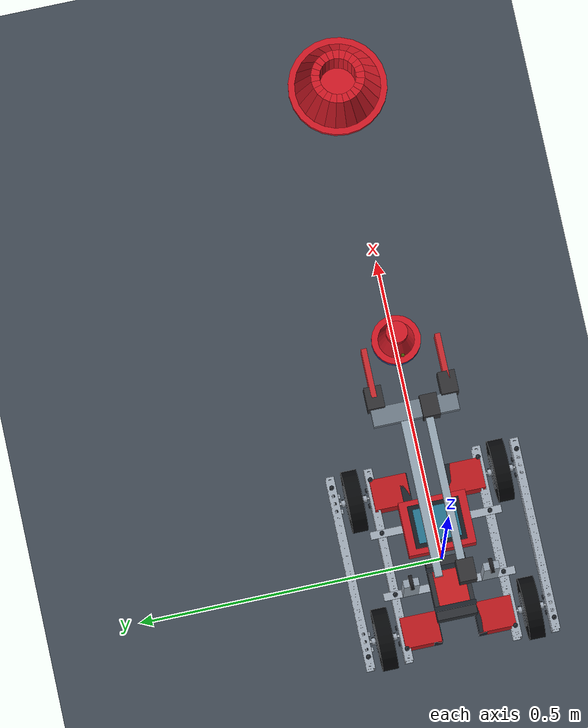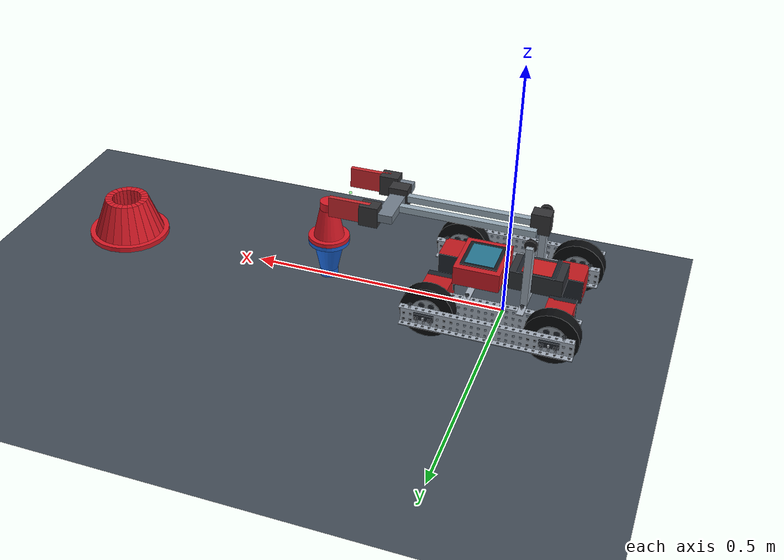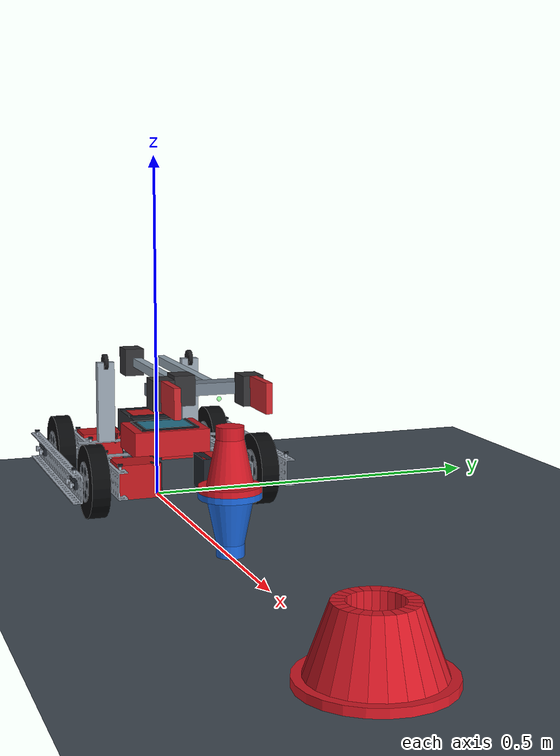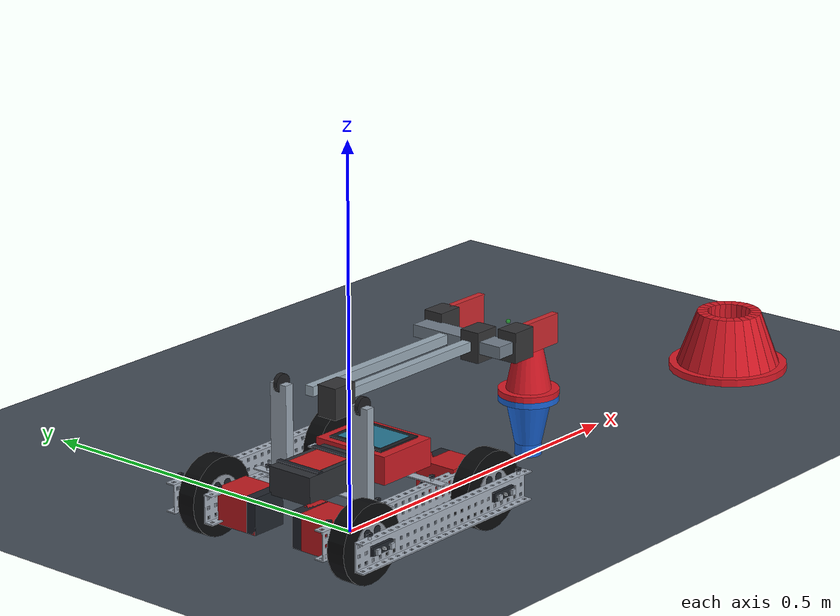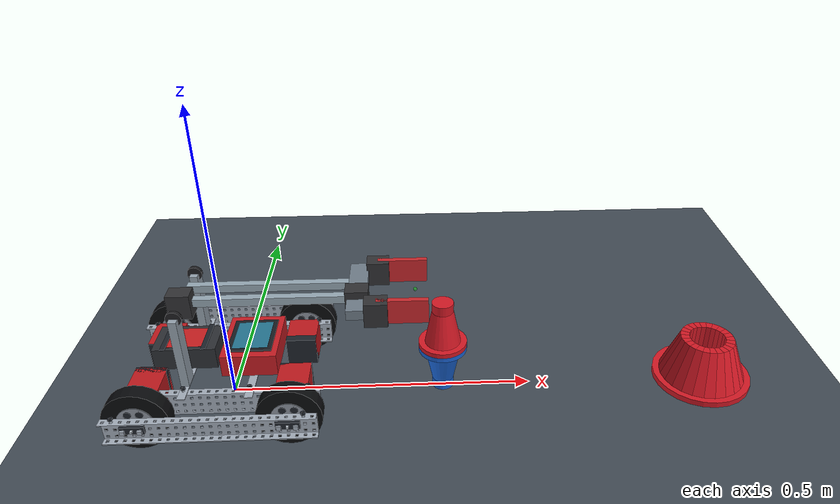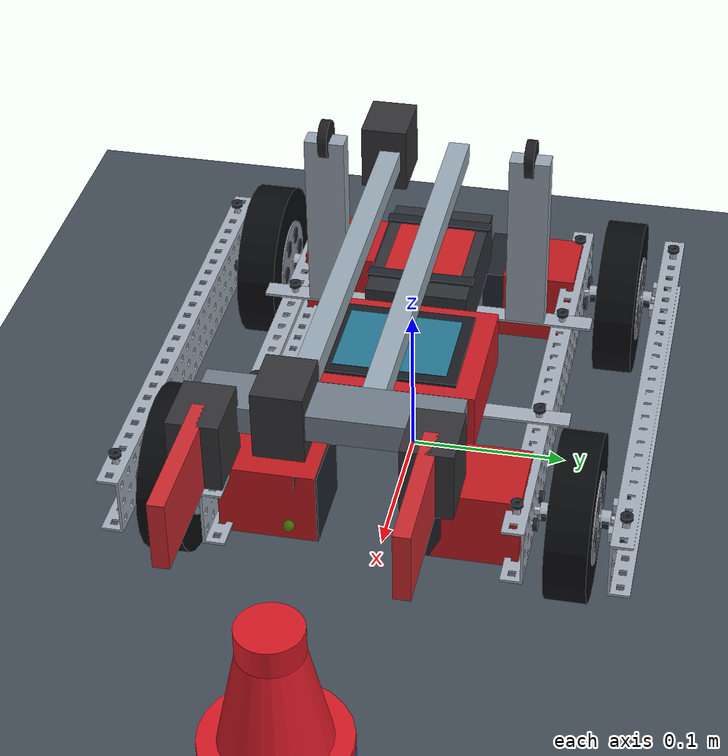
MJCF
<mujoco model="override_mechanism"><compiler angle="radian" inertiafromgeom="true" inertiagrouprange="0 5" /><option timestep="0.002" gravity="0 0 -9.81" integrator="implicitfast" cone="elliptic" iterations="80" /><default><geom friction="0.7 0.002 0.0001" solref="0.01 1" condim="3" /></default><visual><global offwidth="1400" offheight="1000" /><headlight ambient="0.45 0.45 0.45" diffuse="0.7 0.7 0.7" specular="0.15 0.15 0.15" /></visual><asset><mesh name="perforated_channel" vertex="-0.15875 -0.0008 -0.01905 -0.1547 -0.0008 -0.01905 -0.15875 0.0008 -0.01905 -0.1547 0.0008 -0.01905 -0.15875 -0.0008 -0.00635 -0.1547 -0.0008 -0.00635 -0.15875 0.0008 -0.00635 -0.1547 0.0008 -0.00635 -0.1501 -0.0008 -0.01905 -0.14605 -0.0008 -0.01905 -0.1501 0.0008 -0.01905 -0.14605 0.0008 -0.01905 -0.1501 -0.0008 -0.00635 -0.14605 -0.0008 -0.00635 -0.1501 0.0008 -0.00635 -0.14605 0.0008 -0.00635 -0.1547 -0.0008 -0.01905 -0.1501 -0.0008 -0.01905 -0.1547 0.0008 -0.01905 -0.1501 0.0008 -0.01905 -0.1547 -0.0008 -0.015 -0.1501 -0.0008 -0.015 -0.1547 0.0008 -0.015 -0.1501 0.0008 -0.015 -0.1547 -0.0008 -0.0104 -0.1501 -0.0008 -0.0104 -0.1547 0.0008 -0.0104 -0.1501 0.0008 -0.0104 -0.1547 -0.0008 -0.00635 -0.1501 -0.0008 -0.00635 -0.1547 0.0008 -0.00635 -0.1501 0.0008 -0.00635 -0.15875 -0.0008 -0.00635 -0.1547 -0.0008 -0.00635 -0.15875 0.0008 -0.00635 -0.1547 0.0008 -0.00635 -0.15875 -0.0008 0.00635 -0.1547 -0.0008 0.00635 -0.15875 0.0008 0.00635 -0.1547 0.0008 0.00635 -0.1501 -0.0008 -0.00635 -0.14605 -0.0008 -0.00635 -0.1501 0.0008 -0.00635 -0.14605 0.0008 -0.00635 -0.1501 -0.0008 0.00635 -0.14605 -0.0008 0.00635 -0.1501 0.0008 0.00635 -0.14605 0.0008 0.00635 -0.1547 -0.0008 -0.00635 -0.1501 -0.0008 -0.00635 -0.1547 0.0008 -0.00635 -0.1501 0.0008 -0.00635 -0.1547 -0.0008 -0.0023 -0.1501 -0.0008 -0.0023 -0.1547 0.0008 -0.0023 -0.1501 0.0008 -0.0023 -0.1547 -0.0008 0.0023 -0.1501 -0.0008 0.0023 -0.1547 0.0008 0.0023 -0.1501 0.0008 0.0023 -0.1547 -0.0008 0.00635 -0.1501 -0.0008 0.00635 -0.1547 0.0008 0.00635 -0.1501 0.0008 0.00635 -0.15875 -0.0008 0.00635 -0.1547 -0.0008 0.00635 -0.15875 0.0008 0.00635 -0.1547 0.0008 0.00635 -0.15875 -0.0008 0.01905 -0.1547 -0.0008 0.01905 -0.15875 0.0008 0.01905 -0.1547 0.0008 0.01905 -0.1501 -0.0008 0.00635 -0.14605 -0.0008 0.00635 -0.1501 0.0008 0.00635 -0.14605 0.0008 0.00635 -0.1501 -0.0008 0.01905 -0.14605 -0.0008 0.01905 -0.1501 0.0008 0.01905 -0.14605 0.0008 0.01905 -0.1547 -0.0008 0.00635 -0.1501 -0.0008 0.00635 -0.1547 0.0008 0.00635 -0.1501 0.0008 0.00635 -0.1547 -0.0008 0.0104 -0.1501 -0.0008 0.0104 -0.1547 0.0008 0.0104 -0.1501 0.0008 0.0104 -0.1547 -0.0008 0.015 -0.1501 -0.0008 0.015 -0.1547 0.0008 0.015 -0.1501 0.0008 0.015 -0.1547 -0.0008 0.01905 -0.1501 -0.0008 0.01905 -0.1547 0.0008 0.01905 -0.1501 0.0008 0.01905 -0.14605 -0.0008 -0.01905 -0.142 -0.0008 -0.01905 -0.14605 0.0008 -0.01905 -0.142 0.0008 -0.01905 -0.14605 -0.0008 -0.00635 -0.142 -0.0008 -0.00635 -0.14605 0.0008 -0.00635 -0.142 0.0008 -0.00635 -0.1374 -0.0008 -0.01905 -0.13335 -0.0008 -0.01905 -0.1374 0.0008 -0.01905 -0.13335 0.0008 -0.01905 -0.1374 -0.0008 -0.00635 -0.13335 -0.0008 -0.00635 -0.1374 0.0008 -0.00635 -0.13335 0.0008 -0.00635 -0.142 -0.0008 -0.01905 -0.1374 -0.0008 -0.01905 -0.142 0.0008 -0.01905 -0.1374 0.0008 -0.01905 -0.142 -0.0008 -0.015 -0.1374 -0.0008 -0.015 -0.142 0.0008 -0.015 -0.1374 0.0008 -0.015 -0.142 -0.0008 -0.0104 -0.1374 -0.0008 -0.0104 -0.142 0.0008 -0.0104 -0.1374 0.0008 -0.0104 -0.142 -0.0008 -0.00635 -0.1374 -0.0008 -0.00635 -0.142 0.0008 -0.00635 -0.1374 0.0008 -0.00635 -0.14605 -0.0008 -0.00635 -0.142 -0.0008 -0.00635 -0.14605 0.0008 -0.00635 -0.142 0.0008 -0.00635 -0.14605 -0.0008 0.00635 -0.142 -0.0008 0.00635 -0.14605 0.0008 0.00635 -0.142 0.0008 0.00635 -0.1374 -0.0008 -0.00635 -0.13335 -0.0008 -0.00635 -0.1374 0.0008 -0.00635 -0.13335 0.0008 -0.00635 -0.1374 -0.0008 0.00635 -0.13335 -0.0008 0.00635 -0.1374 0.0008 0.00635 -0.13335 0.0008 0.00635 -0.142 -0.0008 -0.00635 -0.1374 -0.0008 -0.00635 -0.142 0.0008 -0.00635 -0.1374 0.0008 -0.00635 -0.142 -0.0008 -0.0023 -0.1374 -0.0008 -0.0023 -0.142 0.0008 -0.0023 -0.1374 0.0008 -0.0023 -0.142 -0.0008 0.0023 -0.1374 -0.0008 0.0023 -0.142 0.0008 0.0023 -0.1374 0.0008 0.0023 -0.142 -0.0008 0.00635 -0.1374 -0.0008 0.00635 -0.142 0.0008 0.00635 -0.1374 0.0008 0.00635 -0.14605 -0.0008 0.00635 -0.142 -0.0008 0.00635 -0.14605 0.0008 0.00635 -0.142 0.0008 0.00635 -0.14605 -0.0008 0.01905 -0.142 -0.0008 0.01905 -0.14605 0.0008 0.01905 -0.142 0.0008 0.01905 -0.1374 -0.0008 0.00635 -0.13335 -0.0008 0.00635 -0.1374 0.0008 0.00635 -0.13335 0.0008 0.00635 -0.1374 -0.0008 0.01905 -0.13335 -0.0008 0.01905 -0.1374 0.0008 0.01905 -0.13335 0.0008 0.01905 -0.142 -0.0008 0.00635 -0.1374 -0.0008 0.00635 -0.142 0.0008 0.00635 -0.1374 0.0008 0.00635 -0.142 -0.0008 0.0104 -0.1374 -0.0008 0.0104 -0.142 0.0008 0.0104 -0.1374 0.0008 0.0104 -0.142 -0.0008 0.015 -0.1374 -0.0008 0.015 -0.142 0.0008 0.015 -0.1374 0.0008 0.015 -0.142 -0.0008 0.01905 -0.1374 -0.0008 0.01905 -0.142 0.0008 0.01905 -0.1374 0.0008 0.01905 -0.13335 -0.0008 -0.01905 -0.1293 -0.0008 -0.01905 -0.13335 0.0008 -0.01905 -0.1293 0.0008 -0.01905 -0.13335 -0.0008 -0.00635 -0.1293 -0.0008 -0.00635 -0.13335 0.0008 -0.00635 -0.1293 0.0008 -0.00635 -0.1247 -0.0008 -0.01905 -0.12065 -0.0008 -0.01905 -0.1247 0.0008 -0.01905 -0.12065 0.0008 -0.01905 -0.1247 -0.0008 -0.00635 -0.12065 -0.0008 -0.00635 -0.1247 0.0008 -0.00635 -0.12065 0.0008 -0.00635 -0.1293 -0.0008 -0.01905 -0.1247 -0.0008 -0.01905 -0.1293 0.0008 -0.01905 -0.1247 0.0008 -0.01905 -0.1293 -0.0008 -0.015 -0.1247 -0.0008 -0.015 -0.1293 0.0008 -0.015 -0.1247 0.0008 -0.015 -0.1293 -0.0008 -0.0104 -0.1247 -0.0008 -0.0104 -0.1293 0.0008 -0.0104 -0.1247 0.0008 -0.0104 -0.1293 -0.0008 -0.00635 -0.1247 -0.0008 -0.00635 -0.1293 0.0008 -0.00635 -0.1247 0.0008 -0.00635 -0.13335 -0.0008 -0.00635 -0.1293 -0.0008 -0.00635 -0.13335 0.0008 -0.00635 -0.1293 0.0008 -0.00635 -0.13335 -0.0008 0.00635 -0.1293 -0.0008 0.00635 -0.13335 0.0008 0.00635 -0.1293 0.0008 0.00635 -0.1247 -0.0008 -0.00635 -0.12065 -0.0008 -0.00635 -0.1247 0.0008 -0.00635 -0.12065 0.0008 -0.00635 -0.1247 -0.0008 0.00635 -0.12065 -0.0008 0.00635 -0.1247 0.0008 0.00635 -0.12065 0.0008 0.00635 -0.1293 -0.0008 -0.00635 -0.1247 -0.0008 -0.00635 -0.1293 0.0008 -0.00635 -0.1247 0.0008 -0.00635 -0.1293 -0.0008 -0.0023 -0.1247 -0.0008 -0.0023 -0.1293 0.0008 -0.0023 -0.1247 0.0008 -0.0023 -0.1293 -0.0008 0.0023 -0.1247 -0.0008 0.0023 -0.1293 0.0008 0.0023 -0.1247 0.0008 0.0023 -0.1293 -0.0008 0.00635 -0.1247 -0.0008 0.00635 -0.1293 0.0008 0.00635 -0.1247 0.0008 0.00635 -0.13335 -0.0008 0.00635 -0.1293 -0.0008 0.00635 -0.13335 0.0008 0.00635 -0.1293 0.0008 0.00635 -0.13335 -0.0008 0.01905 -0.1293 -0.0008 0.01905 -0.13335 0.0008 0.01905 -0.1293 0.0008 0.01905 -0.1247 -0.0008 0.00635 -0.12065 -0.0008 0.00635 -0.1247 0.0008 0.00635 -0.12065 0.0008 0.00635 -0.1247 -0.0008 0.01905 -0.12065 -0.0008 0.01905 -0.1247 0.0008 0.01905 -0.12065 0.0008 0.01905 -0.1293 -0.0008 0.00635 -0.1247 -0.0008 0.00635 -0.1293 0.0008 0.00635 -0.1247 0.0008 0.00635 -0.1293 -0.0008 0.0104 -0.1247 -0.0008 0.0104 -0.1293 0.0008 0.0104 -0.1247 0.0008 0.0104 -0.1293 -0.0008 0.015 -0.1247 -0.0008 0.015 -0.1293 0.0008 0.015 -0.1247 0.0008 0.015 -0.1293 -0.0008 0.01905 -0.1247 -0.0008 0.01905 -0.1293 0.0008 0.01905 -0.1247 0.0008 0.01905 -0.12065 -0.0008 -0.01905 -0.1166 -0.0008 -0.01905 -0.12065 0.0008 -0.01905 -0.1166 0.0008 -0.01905 -0.12065 -0.0008 -0.00635 -0.1166 -0.0008 -0.00635 -0.12065 0.0008 -0.00635 -0.1166 0.0008 -0.00635 -0.112 -0.0008 -0.01905 -0.10795 -0.0008 -0.01905 -0.112 0.0008 -0.01905 -0.10795 0.0008 -0.01905 -0.112 -0.0008 -0.00635 -0.10795 -0.0008 -0.00635 -0.112 0.0008 -0.00635 -0.10795 0.0008 -0.00635 -0.1166 -0.0008 -0.01905 -0.112 -0.0008 -0.01905 -0.1166 0.0008 -0.01905 -0.112 0.0008 -0.01905 -0.1166 -0.0008 -0.015 -0.112 -0.0008 -0.015 -0.1166 0.0008 -0.015 -0.112 0.0008 -0.015 -0.1166 -0.0008 -0.0104 -0.112 -0.0008 -0.0104 -0.1166 0.0008 -0.0104 -0.112 0.0008 -0.0104 -0.1166 -0.0008 -0.00635 -0.112 -0.0008 -0.00635 -0.1166 0.0008 -0.00635 -0.112 0.0008 -0.00635 -0.12065 -0.0008 -0.00635 -0.1166 -0.0008 -0.00635 -0.12065 0.0008 -0.00635 -0.1166 0.0008 -0.00635 -0.12065 -0.0008 0.00635 -0.1166 -0.0008 0.00635 -0.12065 0.0008 0.00635 -0.1166 0.0008 0.00635 -0.112 -0.0008 -0.00635 -0.10795 -0.0008 -0.00635 -0.112 0.0008 -0.00635 -0.10795 0.0008 -0.00635 -0.112 -0.0008 0.00635 -0.10795 -0.0008 0.00635 -0.112 0.0008 0.00635 -0.10795 0.0008 0.00635 -0.1166 -0.0008 -0.00635 -0.112 -0.0008 -0.00635 -0.1166 0.0008 -0.00635 -0.112 0.0008 -0.00635 -0.1166 -0.0008 -0.0023 -0.112 -0.0008 -0.0023 -0.1166 0.0008 -0.0023 -0.112 0.0008 -0.0023 -0.1166 -0.0008 0.0023 -0.112 -0.0008 0.0023 -0.1166 0.0008 0.0023 -0.112 0.0008 0.0023 -0.1166 -0.0008 0.00635 -0.112 -0.0008 0.00635 -0.1166 0.0008 0.00635 -0.112 0.0008 0.00635 -0.12065 -0.0008 0.00635 -0.1166 -0.0008 0.00635 -0.12065 0.0008 0.00635 -0.1166 0.0008 0.00635 -0.12065 -0.0008 0.01905 -0.1166 -0.0008 0.01905 -0.12065 0.0008 0.01905 -0.1166 0.0008 0.01905 -0.112 -0.0008 0.00635 -0.10795 -0.0008 0.00635 -0.112 0.0008 0.00635 -0.10795 0.0008 0.00635 -0.112 -0.0008 0.01905 -0.10795 -0.0008 0.01905 -0.112 0.0008 0.01905 -0.10795 0.0008 0.01905 -0.1166 -0.0008 0.00635 -0.112 -0.0008 0.00635 -0.1166 0.0008 0.00635 -0.112 0.0008 0.00635 -0.1166 -0.0008 0.0104 -0.112 -0.0008 0.0104 -0.1166 0.0008 0.0104 -0.112 0.0008 0.0104 -0.1166 -0.0008 0.015 -0.112 -0.0008 0.015 -0.1166 0.0008 0.015 -0.112 0.0008 0.015 -0.1166 -0.0008 0.01905 -0.112 -0.0008 0.01905 -0.1166 0.0008 0.01905 -0.112 0.0008 0.01905 -0.10795 -0.0008 -0.01905 -0.1039 -0.0008 -0.01905 -0.10795 0.0008 -0.01905 -0.1039 0.0008 -0.01905 -0.10795 -0.0008 -0.00635 -0.1039 -0.0008 -0.00635 -0.10795 0.0008 -0.00635 -0.1039 0.0008 -0.00635 -0.0993 -0.0008 -0.01905 -0.09525 -0.0008 -0.01905 -0.0993 0.0008 -0.01905 -0.09525 0.0008 -0.01905 -0.0993 -0.0008 -0.00635 -0.09525 -0.0008 -0.00635 -0.0993 0.0008 -0.00635 -0.09525 0.0008 -0.00635 -0.1039 -0.0008 -0.01905 -0.0993 -0.0008 -0.01905 -0.1039 0.0008 -0.01905 -0.0993 0.0008 -0.01905 -0.1039 -0.0008 -0.015 -0.0993 -0.0008 -0.015 -0.1039 0.0008 -0.015 -0.0993 0.0008 -0.015 -0.1039 -0.0008 -0.0104 -0.0993 -0.0008 -0.0104 -0.1039 0.0008 -0.0104 -0.0993 0.0008 -0.0104 -0.1039 -0.0008 -0.00635 -0.0993 -0.0008 -0.00635 -0.1039 0.0008 -0.00635 -0.0993 0.0008 -0.00635 -0.10795 -0.0008 -0.00635 -0.1039 -0.0008 -0.00635 -0.10795 0.0008 -0.00635 -0.1039 0.0008 -0.00635 -0.10795 -0.0008 0.00635 -0.1039 -0.0008 0.00635 -0.10795 0.0008 0.00635 -0.1039 0.0008 0.00635 -0.0993 -0.0008 -0.00635 -0.09525 -0.0008 -0.00635 -0.0993 0.0008 -0.00635 -0.09525 0.0008 -0.00635 -0.0993 -0.0008 0.00635 -0.09525 -0.0008 0.00635 -0.0993 0.0008 0.00635 -0.09525 0.0008 0.00635 -0.1039 -0.0008 -0.00635 -0.0993 -0.0008 -0.00635 -0.1039 0.0008 -0.00635 -0.0993 0.0008 -0.00635 -0.1039 -0.0008 -0.0023 -0.0993 -0.0008 -0.0023 -0.1039 0.0008 -0.0023 -0.0993 0.0008 -0.0023 -0.1039 -0.0008 0.0023 -0.0993 -0.0008 0.0023 -0.1039 0.0008 0.0023 -0.0993 0.0008 0.0023 -0.1039 -0.0008 0.00635 -0.0993 -0.0008 0.00635 -0.1039 0.0008 0.00635 -0.0993 0.0008 0.00635 -0.10795 -0.0008 0.00635 -0.1039 -0.0008 0.00635 -0.10795 0.0008 0.00635 -0.1039 0.0008 0.00635 -0.10795 -0.0008 0.01905 -0.1039 -0.0008 0.01905 -0.10795 0.0008 0.01905 -0.1039 0.0008 0.01905 -0.0993 -0.0008 0.00635 -0.09525 -0.0008 0.00635 -0.0993 0.0008 0.00635 -0.09525 0.0008 0.00635 -0.0993 -0.0008 0.01905 -0.09525 -0.0008 0.01905 -0.0993 0.0008 0.01905 -0.09525 0.0008 0.01905 -0.1039 -0.0008 0.00635 -0.0993 -0.0008 0.00635 -0.1039 0.0008 0.00635 -0.0993 0.0008 0.00635 -0.1039 -0.0008 0.0104 -0.0993 -0.0008 0.0104 -0.1039 0.0008 0.0104 -0.0993 0.0008 0.0104 -0.1039 -0.0008 0.015 -0.0993 -0.0008 0.015 -0.1039 0.0008 0.015 -0.0993 0.0008 0.015 -0.1039 -0.0008 0.01905 -0.0993 -0.0008 0.01905 -0.1039 0.0008 0.01905 -0.0993 0.0008 0.01905 -0.09525 -0.0008 -0.01905 -0.0912 -0.0008 -0.01905 -0.09525 0.0008 -0.01905 -0.0912 0.0008 -0.01905 -0.09525 -0.0008 -0.00635 -0.0912 -0.0008 -0.00635 -0.09525 0.0008 -0.00635 -0.0912 0.0008 -0.00635 -0.0866 -0.0008 -0.01905 -0.08255 -0.0008 -0.01905 -0.0866 0.0008 -0.01905 -0.08255 0.0008 -0.01905 -0.0866 -0.0008 -0.00635 -0.08255 -0.0008 -0.00635 -0.0866 0.0008 -0.00635 -0.08255 0.0008 -0.00635 -0.0912 -0.0008 -0.01905 -0.0866 -0.0008 -0.01905 -0.0912 0.0008 -0.01905 -0.0866 0.0008 -0.01905 -0.0912 -0.0008 -0.015 -0.0866 -0.0008 -0.015 -0.0912 0.0008 -0.015 -0.0866 0.0008 -0.015 -0.0912 -0.0008 -0.0104 -0.0866 -0.0008 -0.0104 -0.0912 0.0008 -0.0104 -0.0866 0.0008 -0.0104 -0.0912 -0.0008 -0.00635 -0.0866 -0.0008 -0.00635 -0.0912 0.0008 -0.00635 -0.0866 0.0008 -0.00635 -0.09525 -0.0008 -0.00635 -0.0912 -0.0008 -0.00635 -0.09525 0.0008 -0.00635 -0.0912 0.0008 -0.00635 -0.09525 -0.0008 0.00635 -0.0912 -0.0008 0.00635 -0.09525 0.0008 0.00635 -0.0912 0.0008 0.00635 -0.0866 -0.0008 -0.00635 -0.08255 -0.0008 -0.00635 -0.0866 0.0008 -0.00635 -0.08255 0.0008 -0.00635 -0.0866 -0.0008 0.00635 -0.08255 -0.0008 0.00635 -0.0866 0.0008 0.00635 -0.08255 0.0008 0.00635 -0.0912 -0.0008 -0.00635 -0.0866 -0.0008 -0.00635 -0.0912 0.0008 -0.00635 -0.0866 0.0008 -0.00635 -0.0912 -0.0008 -0.0023 -0.0866 -0.0008 -0.0023 -0.0912 0.0008 -0.0023 -0.0866 0.0008 -0.0023 -0.0912 -0.0008 0.0023 -0.0866 -0.0008 0.0023 -0.0912 0.0008 0.0023 -0.0866 0.0008 0.0023 -0.0912 -0.0008 0.00635 -0.0866 -0.0008 0.00635 -0.0912 0.0008 0.00635 -0.0866 0.0008 0.00635 -0.09525 -0.0008 0.00635 -0.0912 -0.0008 0.00635 -0.09525 0.0008 0.00635 -0.0912 0.0008 0.00635 -0.09525 -0.0008 0.01905 -0.0912 -0.0008 0.01905 -0.09525 0.0008 0.01905 -0.0912 0.0008 0.01905 -0.0866 -0.0008 0.00635 -0.08255 -0.0008 0.00635 -0.0866 0.0008 0.00635 -0.08255 0.0008 0.00635 -0.0866 -0.0008 0.01905 -0.08255 -0.0008 0.01905 -0.0866 0.0008 0.01905 -0.08255 0.0008 0.01905 -0.0912 -0.0008 0.00635 -0.0866 -0.0008 0.00635 -0.0912 0.0008 0.00635 -0.0866 0.0008 0.00635 -0.0912 -0.0008 0.0104 -0.0866 -0.0008 0.0104 -0.0912 0.0008 0.0104 -0.0866 0.0008 0.0104 -0.0912 -0.0008 0.015 -0.0866 -0.0008 0.015 -0.0912 0.0008 0.015 -0.0866 0.0008 0.015 -0.0912 -0.0008 0.01905 -0.0866 -0.0008 0.01905 -0.0912 0.0008 0.01905 -0.0866 0.0008 0.01905 -0.08255 -0.0008 -0.01905 -0.0785 -0.0008 -0.01905 -0.08255 0.0008 -0.01905 -0.0785 0.0008 -0.01905 -0.08255 -0.0008 -0.00635 -0.0785 -0.0008 -0.00635 -0.08255 0.0008 -0.00635 -0.0785 0.0008 -0.00635 -0.0739 -0.0008 -0.01905 -0.06985 -0.0008 -0.01905 -0.0739 0.0008 -0.01905 -0.06985 0.0008 -0.01905 -0.0739 -0.0008 -0.00635 -0.06985 -0.0008 -0.00635 -0.0739 0.0008 -0.00635 -0.06985 0.0008 -0.00635 -0.0785 -0.0008 -0.01905 -0.0739 -0.0008 -0.01905 -0.0785 0.0008 -0.01905 -0.0739 0.0008 -0.01905 -0.0785 -0.0008 -0.015 -0.0739 -0.0008 -0.015 -0.0785 0.0008 -0.015 -0.0739 0.0008 -0.015 -0.0785 -0.0008 -0.0104 -0.0739 -0.0008 -0.0104 -0.0785 0.0008 -0.0104 -0.0739 0.0008 -0.0104 -0.0785 -0.0008 -0.00635 -0.0739 -0.0008 -0.00635 -0.0785 0.0008 -0.00635 -0.0739 0.0008 -0.00635 -0.08255 -0.0008 -0.00635 -0.0785 -0.0008 -0.00635 -0.08255 0.0008 -0.00635 -0.0785 0.0008 -0.00635 -0.08255 -0.0008 0.00635 -0.0785 -0.0008 0.00635 -0.08255 0.0008 0.00635 -0.0785 0.0008 0.00635 -0.0739 -0.0008 -0.00635 -0.06985 -0.0008 -0.00635 -0.0739 0.0008 -0.00635 -0.06985 0.0008 -0.00635 -0.0739 -0.0008 0.00635 -0.06985 -0.0008 0.00635 -0.0739 0.0008 0.00635 -0.06985 0.0008 0.00635 -0.0785 -0.0008 -0.00635 -0.0739 -0.0008 -0.00635 -0.0785 0.0008 -0.00635 -0.0739 0.0008 -0.00635 -0.0785 -0.0008 -0.0023 -0.0739 -0.0008 -0.0023 -0.0785 0.0008 -0.0023 -0.0739 0.0008 -0.0023 -0.0785 -0.0008 0.0023 -0.0739 -0.0008 0.0023 -0.0785 0.0008 0.0023 -0.0739 0.0008 0.0023 -0.0785 -0.0008 0.00635 -0.0739 -0.0008 0.00635 -0.0785 0.0008 0.00635 -0.0739 0.0008 0.00635 -0.08255 -0.0008 0.00635 -0.0785 -0.0008 0.00635 -0.08255 0.0008 0.00635 -0.0785 0.0008 0.00635 -0.08255 -0.0008 0.01905 -0.0785 -0.0008 0.01905 -0.08255 0.0008 0.01905 -0.0785 0.0008 0.01905 -0.0739 -0.0008 0.00635 -0.06985 -0.0008 0.00635 -0.0739 0.0008 0.00635 -0.06985 0.0008 0.00635 -0.0739 -0.0008 0.01905 -0.06985 -0.0008 0.01905 -0.0739 0.0008 0.01905 -0.06985 0.0008 0.01905 -0.0785 -0.0008 0.00635 -0.0739 -0.0008 0.00635 -0.0785 0.0008 0.00635 -0.0739 0.0008 0.00635 -0.0785 -0.0008 0.0104 -0.0739 -0.0008 0.0104 -0.0785 0.0008 0.0104 -0.0739 0.0008 0.0104 -0.0785 -0.0008 0.015 -0.0739 -0.0008 0.015 -0.0785 0.0008 0.015 -0.0739 0.0008 0.015 -0.0785 -0.0008 0.01905 -0.0739 -0.0008 0.01905 -0.0785 0.0008 0.01905 -0.0739 0.0008 0.01905 -0.06985 -0.0008 -0.01905 -0.0658 -0.0008 -0.01905 -0.06985 0.0008 -0.01905 -0.0658 0.0008 -0.01905 -0.06985 -0.0008 -0.00635 -0.0658 -0.0008 -0.00635 -0.06985 0.0008 -0.00635 -0.0658 0.0008 -0.00635 -0.0612 -0.0008 -0.01905 -0.05715 -0.0008 -0.01905 -0.0612 0.0008 -0.01905 -0.05715 0.0008 -0.01905 -0.0612 -0.0008 -0.00635 -0.05715 -0.0008 -0.00635 -0.0612 0.0008 -0.00635 -0.05715 0.0008 -0.00635 -0.0658 -0.0008 -0.01905 -0.0612 -0.0008 -0.01905 -0.0658 0.0008 -0.01905 -0.0612 0.0008 -0.01905 -0.0658 -0.0008 -0.015 -0.0612 -0.0008 -0.015 -0.0658 0.0008 -0.015 -0.0612 0.0008 -0.015 -0.0658 -0.0008 -0.0104 -0.0612 -0.0008 -0.0104 -0.0658 0.0008 -0.0104 -0.0612 0.0008 -0.0104 -0.0658 -0.0008 -0.00635 -0.0612 -0.0008 -0.00635 -0.0658 0.0008 -0.00635 -0.0612 0.0008 -0.00635 -0.06985 -0.0008 -0.00635 -0.0658 -0.0008 -0.00635 -0.06985 0.0008 -0.00635 -0.0658 0.0008 -0.00635 -0.06985 -0.0008 0.00635 -0.0658 -0.0008 0.00635 -0.06985 0.0008 0.00635 -0.0658 0.0008 0.00635 -0.0612 -0.0008 -0.00635 -0.05715 -0.0008 -0.00635 -0.0612 0.0008 -0.00635 -0.05715 0.0008 -0.00635 -0.0612 -0.0008 0.00635 -0.05715 -0.0008 0.00635 -0.0612 0.0008 0.00635 -0.05715 0.0008 0.00635 -0.0658 -0.0008 -0.00635 -0.0612 -0.0008 -0.00635 -0.0658 0.0008 -0.00635 -0.0612 0.0008 -0.00635 -0.0658 -0.0008 -0.0023 -0.0612 -0.0008 -0.0023 -0.0658 0.0008 -0.0023 -0.0612 0.0008 -0.0023 -0.0658 -0.0008 0.0023 -0.0612 -0.0008 0.0023 -0.0658 0.0008 0.0023 -0.0612 0.0008 0.0023 -0.0658 -0.0008 0.00635 -0.0612 -0.0008 0.00635 -0.0658 0.0008 0.00635 -0.0612 0.0008 0.00635 -0.06985 -0.0008 0.00635 -0.0658 -0.0008 0.00635 -0.06985 0.0008 0.00635 -0.0658 0.0008 0.00635 -0.06985 -0.0008 0.01905 -0.0658 -0.0008 0.01905 -0.06985 0.0008 0.01905 -0.0658 0.0008 0.01905 -0.0612 -0.0008 0.00635 -0.05715 -0.0008 0.00635 -0.0612 0.0008 0.00635 -0.05715 0.0008 0.00635 -0.0612 -0.0008 0.01905 -0.05715 -0.0008 0.01905 -0.0612 0.0008 0.01905 -0.05715 0.0008 0.01905 -0.0658 -0.0008 0.00635 -0.0612 -0.0008 0.00635 -0.0658 0.0008 0.00635 -0.0612 0.0008 0.00635 -0.0658 -0.0008 0.0104 -0.0612 -0.0008 0.0104 -0.0658 0.0008 0.0104 -0.0612 0.0008 0.0104 -0.0658 -0.0008 0.015 -0.0612 -0.0008 0.015 -0.0658 0.0008 0.015 -0.0612 0.0008 0.015 -0.0658 -0.0008 0.01905 -0.0612 -0.0008 0.01905 -0.0658 0.0008 0.01905 -0.0612 0.0008 0.01905 -0.05715 -0.0008 -0.01905 -0.0531 -0.0008 -0.01905 -0.05715 0.0008 -0.01905 -0.0531 0.0008 -0.01905 -0.05715 -0.0008 -0.00635 -0.0531 -0.0008 -0.00635 -0.05715 0.0008 -0.00635 -0.0531 0.0008 -0.00635 -0.0485 -0.0008 -0.01905 -0.04445 -0.0008 -0.01905 -0.0485 0.0008 -0.01905 -0.04445 0.0008 -0.01905 -0.0485 -0.0008 -0.00635 -0.04445 -0.0008 -0.00635 -0.0485 0.0008 -0.00635 -0.04445 0.0008 -0.00635 -0.0531 -0.0008 -0.01905 -0.0485 -0.0008 -0.01905 -0.0531 0.0008 -0.01905 -0.0485 0.0008 -0.01905 -0.0531 -0.0008 -0.015 -0.0485 -0.0008 -0.015 -0.0531 0.0008 -0.015 -0.0485 0.0008 -0.015 -0.0531 -0.0008 -0.0104 -0.0485 -0.0008 -0.0104 -0.0531 0.0008 -0.0104 -0.0485 0.0008 -0.0104 -0.0531 -0.0008 -0.00635 -0.0485 -0.0008 -0.00635 -0.0531 0.0008 -0.00635 -0.0485 0.0008 -0.00635 -0.05715 -0.0008 -0.00635 -0.0531 -0.0008 -0.00635 -0.05715 0.0008 -0.00635 -0.0531 0.0008 -0.00635 -0.05715 -0.0008 0.00635 -0.0531 -0.0008 0.00635 -0.05715 0.0008 0.00635 -0.0531 0.0008 0.00635 -0.0485 -0.0008 -0.00635 -0.04445 -0.0008 -0.00635 -0.0485 0.0008 -0.00635 -0.04445 0.0008 -0.00635 -0.0485 -0.0008 0.00635 -0.04445 -0.0008 0.00635 -0.0485 0.0008 0.00635 -0.04445 0.0008 0.00635 -0.0531 -0.0008 -0.00635 -0.0485 -0.0008 -0.00635 -0.0531 0.0008 -0.00635 -0.0485 0.0008 -0.00635 -0.0531 -0.0008 -0.0023 -0.0485 -0.0008 -0.0023 -0.0531 0.0008 -0.0023 -0.0485 0.0008 -0.0023 -0.0531 -0.0008 0.0023 -0.0485 -0.0008 0.0023 -0.0531 0.0008 0.0023 -0.0485 0.0008 0.0023 -0.0531 -0.0008 0.00635 -0.0485 -0.0008 0.00635 -0.0531 0.0008 0.00635 -0.0485 0.0008 0.00635 -0.05715 -0.0008 0.00635 -0.0531 -0.0008 0.00635 -0.05715 0.0008 0.00635 -0.0531 0.0008 0.00635 -0.05715 -0.0008 0.01905 -0.0531 -0.0008 0.01905 -0.05715 0.0008 0.01905 -0.0531 0.0008 0.01905 -0.0485 -0.0008 0.00635 -0.04445 -0.0008 0.00635 -0.0485 0.0008 0.00635 -0.04445 0.0008 0.00635 -0.0485 -0.0008 0.01905 -0.04445 -0.0008 0.01905 -0.0485 0.0008 0.01905 -0.04445 0.0008 0.01905 -0.0531 -0.0008 0.00635 -0.0485 -0.0008 0.00635 -0.0531 0.0008 0.00635 -0.0485 0.0008 0.00635 -0.0531 -0.0008 0.0104 -0.0485 -0.0008 0.0104 -0.0531 0.0008 0.0104 -0.0485 0.0008 0.0104 -0.0531 -0.0008 0.015 -0.0485 -0.0008 0.015 -0.0531 0.0008 0.015 -0.0485 0.0008 0.015 -0.0531 -0.0008 0.01905 -0.0485 -0.0008 0.01905 -0.0531 0.0008 0.01905 -0.0485 0.0008 0.01905 -0.04445 -0.0008 -0.01905 -0.0404 -0.0008 -0.01905 -0.04445 0.0008 -0.01905 -0.0404 0.0008 -0.01905 -0.04445 -0.0008 -0.00635 -0.0404 -0.0008 -0.00635 -0.04445 0.0008 -0.00635 -0.0404 0.0008 -0.00635 -0.0358 -0.0008 -0.01905 -0.03175 -0.0008 -0.01905 -0.0358 0.0008 -0.01905 -0.03175 0.0008 -0.01905 -0.0358 -0.0008 -0.00635 -0.03175 -0.0008 -0.00635 -0.0358 0.0008 -0.00635 -0.03175 0.0008 -0.00635 -0.0404 -0.0008 -0.01905 -0.0358 -0.0008 -0.01905 -0.0404 0.0008 -0.01905 -0.0358 0.0008 -0.01905 -0.0404 -0.0008 -0.015 -0.0358 -0.0008 -0.015 -0.0404 0.0008 -0.015 -0.0358 0.0008 -0.015 -0.0404 -0.0008 -0.0104 -0.0358 -0.0008 -0.0104 -0.0404 0.0008 -0.0104 -0.0358 0.0008 -0.0104 -0.0404 -0.0008 -0.00635 -0.0358 -0.0008 -0.00635 -0.0404 0.0008 -0.00635 -0.0358 0.0008 -0.00635 -0.04445 -0.0008 -0.00635 -0.0404 -0.0008 -0.00635 -0.04445 0.0008 -0.00635 -0.0404 0.0008 -0.00635 -0.04445 -0.0008 0.00635 -0.0404 -0.0008 0.00635 -0.04445 0.0008 0.00635 -0.0404 0.0008 0.00635 -0.0358 -0.0008 -0.00635 -0.03175 -0.0008 -0.00635 -0.0358 0.0008 -0.00635 -0.03175 0.0008 -0.00635 -0.0358 -0.0008 0.00635 -0.03175 -0.0008 0.00635 -0.0358 0.0008 0.00635 -0.03175 0.0008 0.00635 -0.0404 -0.0008 -0.00635 -0.0358 -0.0008 -0.00635 -0.0404 0.0008 -0.00635 -0.0358 0.0008 -0.00635 -0.0404 -0.0008 -0.0023 -0.0358 -0.0008 -0.0023 -0.0404 0.0008 -0.0023 -0.0358 0.0008 -0.0023 -0.0404 -0.0008 0.0023 -0.0358 -0.0008 0.0023 -0.0404 0.0008 0.0023 -0.0358 0.0008 0.0023 -0.0404 -0.0008 0.00635 -0.0358 -0.0008 0.00635 -0.0404 0.0008 0.00635 -0.0358 0.0008 0.00635 -0.04445 -0.0008 0.00635 -0.0404 -0.0008 0.00635 -0.04445 0.0008 0.00635 -0.0404 0.0008 0.00635 -0.04445 -0.0008 0.01905 -0.0404 -0.0008 0.01905 -0.04445 0.0008 0.01905 -0.0404 0.0008 0.01905 -0.0358 -0.0008 0.00635 -0.03175 -0.0008 0.00635 -0.0358 0.0008 0.00635 -0.03175 0.0008 0.00635 -0.0358 -0.0008 0.01905 -0.03175 -0.0008 0.01905 -0.0358 0.0008 0.01905 -0.03175 0.0008 0.01905 -0.0404 -0.0008 0.00635 -0.0358 -0.0008 0.00635 -0.0404 0.0008 0.00635 -0.0358 0.0008 0.00635 -0.0404 -0.0008 0.0104 -0.0358 -0.0008 0.0104 -0.0404 0.0008 0.0104 -0.0358 0.0008 0.0104 -0.0404 -0.0008 0.015 -0.0358 -0.0008 0.015 -0.0404 0.0008 0.015 -0.0358 0.0008 0.015 -0.0404 -0.0008 0.01905 -0.0358 -0.0008 0.01905 -0.0404 0.0008 0.01905 -0.0358 0.0008 0.01905 -0.03175 -0.0008 -0.01905 -0.0277 -0.0008 -0.01905 -0.03175 0.0008 -0.01905 -0.0277 0.0008 -0.01905 -0.03175 -0.0008 -0.00635 -0.0277 -0.0008 -0.00635 -0.03175 0.0008 -0.00635 -0.0277 0.0008 -0.00635 -0.0231 -0.0008 -0.01905 -0.01905 -0.0008 -0.01905 -0.0231 0.0008 -0.01905 -0.01905 0.0008 -0.01905 -0.0231 -0.0008 -0.00635 -0.01905 -0.0008 -0.00635 -0.0231 0.0008 -0.00635 -0.01905 0.0008 -0.00635 -0.0277 -0.0008 -0.01905 -0.0231 -0.0008 -0.01905 -0.0277 0.0008 -0.01905 -0.0231 0.0008 -0.01905 -0.0277 -0.0008 -0.015 -0.0231 -0.0008 -0.015 -0.0277 0.0008 -0.015 -0.0231 0.0008 -0.015 -0.0277 -0.0008 -0.0104 -0.0231 -0.0008 -0.0104 -0.0277 0.0008 -0.0104 -0.0231 0.0008 -0.0104 -0.0277 -0.0008 -0.00635 -0.0231 -0.0008 -0.00635 -0.0277 0.0008 -0.00635 -0.0231 0.0008 -0.00635 -0.03175 -0.0008 -0.00635 -0.0277 -0.0008 -0.00635 -0.03175 0.0008 -0.00635 -0.0277 0.0008 -0.00635 -0.03175 -0.0008 0.00635 -0.0277 -0.0008 0.00635 -0.03175 0.0008 0.00635 -0.0277 0.0008 0.00635 -0.0231 -0.0008 -0.00635 -0.01905 -0.0008 -0.00635 -0.0231 0.0008 -0.00635 -0.01905 0.0008 -0.00635 -0.0231 -0.0008 0.00635 -0.01905 -0.0008 0.00635 -0.0231 0.0008 0.00635 -0.01905 0.0008 0.00635 -0.0277 -0.0008 -0.00635 -0.0231 -0.0008 -0.00635 -0.0277 0.0008 -0.00635 -0.0231 0.0008 -0.00635 -0.0277 -0.0008 -0.0023 -0.0231 -0.0008 -0.0023 -0.0277 0.0008 -0.0023 -0.0231 0.0008 -0.0023 -0.0277 -0.0008 0.0023 -0.0231 -0.0008 0.0023 -0.0277 0.0008 0.0023 -0.0231 0.0008 0.0023 -0.0277 -0.0008 0.00635 -0.0231 -0.0008 0.00635 -0.0277 0.0008 0.00635 -0.0231 0.0008 0.00635 -0.03175 -0.0008 0.00635 -0.0277 -0.0008 0.00635 -0.03175 0.0008 0.00635 -0.0277 0.0008 0.00635 -0.03175 -0.0008 0.01905 -0.0277 -0.0008 0.01905 -0.03175 0.0008 0.01905 -0.0277 0.0008 0.01905 -0.0231 -0.0008 0.00635 -0.01905 -0.0008 0.00635 -0.0231 0.0008 0.00635 -0.01905 0.0008 0.00635 -0.0231 -0.0008 0.01905 -0.01905 -0.0008 0.01905 -0.0231 0.0008 0.01905 -0.01905 0.0008 0.01905 -0.0277 -0.0008 0.00635 -0.0231 -0.0008 0.00635 -0.0277 0.0008 0.00635 -0.0231 0.0008 0.00635 -0.0277 -0.0008 0.0104 -0.0231 -0.0008 0.0104 -0.0277 0.0008 0.0104 -0.0231 0.0008 0.0104 -0.0277 -0.0008 0.015 -0.0231 -0.0008 0.015 -0.0277 0.0008 0.015 -0.0231 0.0008 0.015 -0.0277 -0.0008 0.01905 -0.0231 -0.0008 0.01905 -0.0277 0.0008 0.01905 -0.0231 0.0008 0.01905 -0.01905 -0.0008 -0.01905 -0.015 -0.0008 -0.01905 -0.01905 0.0008 -0.01905 -0.015 0.0008 -0.01905 -0.01905 -0.0008 -0.00635 -0.015 -0.0008 -0.00635 -0.01905 0.0008 -0.00635 -0.015 0.0008 -0.00635 -0.0104 -0.0008 -0.01905 -0.00635 -0.0008 -0.01905 -0.0104 0.0008 -0.01905 -0.00635 0.0008 -0.01905 -0.0104 -0.0008 -0.00635 -0.00635 -0.0008 -0.00635 -0.0104 0.0008 -0.00635 -0.00635 0.0008 -0.00635 -0.015 -0.0008 -0.01905 -0.0104 -0.0008 -0.01905 -0.015 0.0008 -0.01905 -0.0104 0.0008 -0.01905 -0.015 -0.0008 -0.015 -0.0104 -0.0008 -0.015 -0.015 0.0008 -0.015 -0.0104 0.0008 -0.015 -0.015 -0.0008 -0.0104 -0.0104 -0.0008 -0.0104 -0.015 0.0008 -0.0104 -0.0104 0.0008 -0.0104 -0.015 -0.0008 -0.00635 -0.0104 -0.0008 -0.00635 -0.015 0.0008 -0.00635 -0.0104 0.0008 -0.00635 -0.01905 -0.0008 -0.00635 -0.015 -0.0008 -0.00635 -0.01905 0.0008 -0.00635 -0.015 0.0008 -0.00635 -0.01905 -0.0008 0.00635 -0.015 -0.0008 0.00635 -0.01905 0.0008 0.00635 -0.015 0.0008 0.00635 -0.0104 -0.0008 -0.00635 -0.00635 -0.0008 -0.00635 -0.0104 0.0008 -0.00635 -0.00635 0.0008 -0.00635 -0.0104 -0.0008 0.00635 -0.00635 -0.0008 0.00635 -0.0104 0.0008 0.00635 -0.00635 0.0008 0.00635 -0.015 -0.0008 -0.00635 -0.0104 -0.0008 -0.00635 -0.015 0.0008 -0.00635 -0.0104 0.0008 -0.00635 -0.015 -0.0008 -0.0023 -0.0104 -0.0008 -0.0023 -0.015 0.0008 -0.0023 -0.0104 0.0008 -0.0023 -0.015 -0.0008 0.0023 -0.0104 -0.0008 0.0023 -0.015 0.0008 0.0023 -0.0104 0.0008 0.0023 -0.015 -0.0008 0.00635 -0.0104 -0.0008 0.00635 -0.015 0.0008 0.00635 -0.0104 0.0008 0.00635 -0.01905 -0.0008 0.00635 -0.015 -0.0008 0.00635 -0.01905 0.0008 0.00635 -0.015 0.0008 0.00635 -0.01905 -0.0008 0.01905 -0.015 -0.0008 0.01905 -0.01905 0.0008 0.01905 -0.015 0.0008 0.01905 -0.0104 -0.0008 0.00635 -0.00635 -0.0008 0.00635 -0.0104 0.0008 0.00635 -0.00635 0.0008 0.00635 -0.0104 -0.0008 0.01905 -0.00635 -0.0008 0.01905 -0.0104 0.0008 0.01905 -0.00635 0.0008 0.01905 -0.015 -0.0008 0.00635 -0.0104 -0.0008 0.00635 -0.015 0.0008 0.00635 -0.0104 0.0008 0.00635 -0.015 -0.0008 0.0104 -0.0104 -0.0008 0.0104 -0.015 0.0008 0.0104 -0.0104 0.0008 0.0104 -0.015 -0.0008 0.015 -0.0104 -0.0008 0.015 -0.015 0.0008 0.015 -0.0104 0.0008 0.015 -0.015 -0.0008 0.01905 -0.0104 -0.0008 0.01905 -0.015 0.0008 0.01905 -0.0104 0.0008 0.01905 -0.00635 -0.0008 -0.01905 -0.0023 -0.0008 -0.01905 -0.00635 0.0008 -0.01905 -0.0023 0.0008 -0.01905 -0.00635 -0.0008 -0.00635 -0.0023 -0.0008 -0.00635 -0.00635 0.0008 -0.00635 -0.0023 0.0008 -0.00635 0.0023 -0.0008 -0.01905 0.00635 -0.0008 -0.01905 0.0023 0.0008 -0.01905 0.00635 0.0008 -0.01905 0.0023 -0.0008 -0.00635 0.00635 -0.0008 -0.00635 0.0023 0.0008 -0.00635 0.00635 0.0008 -0.00635 -0.0023 -0.0008 -0.01905 0.0023 -0.0008 -0.01905 -0.0023 0.0008 -0.01905 0.0023 0.0008 -0.01905 -0.0023 -0.0008 -0.015 0.0023 -0.0008 -0.015 -0.0023 0.0008 -0.015 0.0023 0.0008 -0.015 -0.0023 -0.0008 -0.0104 0.0023 -0.0008 -0.0104 -0.0023 0.0008 -0.0104 0.0023 0.0008 -0.0104 -0.0023 -0.0008 -0.00635 0.0023 -0.0008 -0.00635 -0.0023 0.0008 -0.00635 0.0023 0.0008 -0.00635 -0.00635 -0.0008 -0.00635 -0.0023 -0.0008 -0.00635 -0.00635 0.0008 -0.00635 -0.0023 0.0008 -0.00635 -0.00635 -0.0008 0.00635 -0.0023 -0.0008 0.00635 -0.00635 0.0008 0.00635 -0.0023 0.0008 0.00635 0.0023 -0.0008 -0.00635 0.00635 -0.0008 -0.00635 0.0023 0.0008 -0.00635 0.00635 0.0008 -0.00635 0.0023 -0.0008 0.00635 0.00635 -0.0008 0.00635 0.0023 0.0008 0.00635 0.00635 0.0008 0.00635 -0.0023 -0.0008 -0.00635 0.0023 -0.0008 -0.00635 -0.0023 0.0008 -0.00635 0.0023 0.0008 -0.00635 -0.0023 -0.0008 -0.0023 0.0023 -0.0008 -0.0023 -0.0023 0.0008 -0.0023 0.0023 0.0008 -0.0023 -0.0023 -0.0008 0.0023 0.0023 -0.0008 0.0023 -0.0023 0.0008 0.0023 0.0023 0.0008 0.0023 -0.0023 -0.0008 0.00635 0.0023 -0.0008 0.00635 -0.0023 0.0008 0.00635 0.0023 0.0008 0.00635 -0.00635 -0.0008 0.00635 -0.0023 -0.0008 0.00635 -0.00635 0.0008 0.00635 -0.0023 0.0008 0.00635 -0.00635 -0.0008 0.01905 -0.0023 -0.0008 0.01905 -0.00635 0.0008 0.01905 -0.0023 0.0008 0.01905 0.0023 -0.0008 0.00635 0.00635 -0.0008 0.00635 0.0023 0.0008 0.00635 0.00635 0.0008 0.00635 0.0023 -0.0008 0.01905 0.00635 -0.0008 0.01905 0.0023 0.0008 0.01905 0.00635 0.0008 0.01905 -0.0023 -0.0008 0.00635 0.0023 -0.0008 0.00635 -0.0023 0.0008 0.00635 0.0023 0.0008 0.00635 -0.0023 -0.0008 0.0104 0.0023 -0.0008 0.0104 -0.0023 0.0008 0.0104 0.0023 0.0008 0.0104 -0.0023 -0.0008 0.015 0.0023 -0.0008 0.015 -0.0023 0.0008 0.015 0.0023 0.0008 0.015 -0.0023 -0.0008 0.01905 0.0023 -0.0008 0.01905 -0.0023 0.0008 0.01905 0.0023 0.0008 0.01905 0.00635 -0.0008 -0.01905 0.0104 -0.0008 -0.01905 0.00635 0.0008 -0.01905 0.0104 0.0008 -0.01905 0.00635 -0.0008 -0.00635 0.0104 -0.0008 -0.00635 0.00635 0.0008 -0.00635 0.0104 0.0008 -0.00635 0.015 -0.0008 -0.01905 0.01905 -0.0008 -0.01905 0.015 0.0008 -0.01905 0.01905 0.0008 -0.01905 0.015 -0.0008 -0.00635 0.01905 -0.0008 -0.00635 0.015 0.0008 -0.00635 0.01905 0.0008 -0.00635 0.0104 -0.0008 -0.01905 0.015 -0.0008 -0.01905 0.0104 0.0008 -0.01905 0.015 0.0008 -0.01905 0.0104 -0.0008 -0.015 0.015 -0.0008 -0.015 0.0104 0.0008 -0.015 0.015 0.0008 -0.015 0.0104 -0.0008 -0.0104 0.015 -0.0008 -0.0104 0.0104 0.0008 -0.0104 0.015 0.0008 -0.0104 0.0104 -0.0008 -0.00635 0.015 -0.0008 -0.00635 0.0104 0.0008 -0.00635 0.015 0.0008 -0.00635 0.00635 -0.0008 -0.00635 0.0104 -0.0008 -0.00635 0.00635 0.0008 -0.00635 0.0104 0.0008 -0.00635 0.00635 -0.0008 0.00635 0.0104 -0.0008 0.00635 0.00635 0.0008 0.00635 0.0104 0.0008 0.00635 0.015 -0.0008 -0.00635 0.01905 -0.0008 -0.00635 0.015 0.0008 -0.00635 0.01905 0.0008 -0.00635 0.015 -0.0008 0.00635 0.01905 -0.0008 0.00635 0.015 0.0008 0.00635 0.01905 0.0008 0.00635 0.0104 -0.0008 -0.00635 0.015 -0.0008 -0.00635 0.0104 0.0008 -0.00635 0.015 0.0008 -0.00635 0.0104 -0.0008 -0.0023 0.015 -0.0008 -0.0023 0.0104 0.0008 -0.0023 0.015 0.0008 -0.0023 0.0104 -0.0008 0.0023 0.015 -0.0008 0.0023 0.0104 0.0008 0.0023 0.015 0.0008 0.0023 0.0104 -0.0008 0.00635 0.015 -0.0008 0.00635 0.0104 0.0008 0.00635 0.015 0.0008 0.00635 0.00635 -0.0008 0.00635 0.0104 -0.0008 0.00635 0.00635 0.0008 0.00635 0.0104 0.0008 0.00635 0.00635 -0.0008 0.01905 0.0104 -0.0008 0.01905 0.00635 0.0008 0.01905 0.0104 0.0008 0.01905 0.015 -0.0008 0.00635 0.01905 -0.0008 0.00635 0.015 0.0008 0.00635 0.01905 0.0008 0.00635 0.015 -0.0008 0.01905 0.01905 -0.0008 0.01905 0.015 0.0008 0.01905 0.01905 0.0008 0.01905 0.0104 -0.0008 0.00635 0.015 -0.0008 0.00635 0.0104 0.0008 0.00635 0.015 0.0008 0.00635 0.0104 -0.0008 0.0104 0.015 -0.0008 0.0104 0.0104 0.0008 0.0104 0.015 0.0008 0.0104 0.0104 -0.0008 0.015 0.015 -0.0008 0.015 0.0104 0.0008 0.015 0.015 0.0008 0.015 0.0104 -0.0008 0.01905 0.015 -0.0008 0.01905 0.0104 0.0008 0.01905 0.015 0.0008 0.01905 0.01905 -0.0008 -0.01905 0.0231 -0.0008 -0.01905 0.01905 0.0008 -0.01905 0.0231 0.0008 -0.01905 0.01905 -0.0008 -0.00635 0.0231 -0.0008 -0.00635 0.01905 0.0008 -0.00635 0.0231 0.0008 -0.00635 0.0277 -0.0008 -0.01905 0.03175 -0.0008 -0.01905 0.0277 0.0008 -0.01905 0.03175 0.0008 -0.01905 0.0277 -0.0008 -0.00635 0.03175 -0.0008 -0.00635 0.0277 0.0008 -0.00635 0.03175 0.0008 -0.00635 0.0231 -0.0008 -0.01905 0.0277 -0.0008 -0.01905 0.0231 0.0008 -0.01905 0.0277 0.0008 -0.01905 0.0231 -0.0008 -0.015 0.0277 -0.0008 -0.015 0.0231 0.0008 -0.015 0.0277 0.0008 -0.015 0.0231 -0.0008 -0.0104 0.0277 -0.0008 -0.0104 0.0231 0.0008 -0.0104 0.0277 0.0008 -0.0104 0.0231 -0.0008 -0.00635 0.0277 -0.0008 -0.00635 0.0231 0.0008 -0.00635 0.0277 0.0008 -0.00635 0.01905 -0.0008 -0.00635 0.0231 -0.0008 -0.00635 0.01905 0.0008 -0.00635 0.0231 0.0008 -0.00635 0.01905 -0.0008 0.00635 0.0231 -0.0008 0.00635 0.01905 0.0008 0.00635 0.0231 0.0008 0.00635 0.0277 -0.0008 -0.00635 0.03175 -0.0008 -0.00635 0.0277 0.0008 -0.00635 0.03175 0.0008 -0.00635 0.0277 -0.0008 0.00635 0.03175 -0.0008 0.00635 0.0277 0.0008 0.00635 0.03175 0.0008 0.00635 0.0231 -0.0008 -0.00635 0.0277 -0.0008 -0.00635 0.0231 0.0008 -0.00635 0.0277 0.0008 -0.00635 0.0231 -0.0008 -0.0023 0.0277 -0.0008 -0.0023 0.0231 0.0008 -0.0023 0.0277 0.0008 -0.0023 0.0231 -0.0008 0.0023 0.0277 -0.0008 0.0023 0.0231 0.0008 0.0023 0.0277 0.0008 0.0023 0.0231 -0.0008 0.00635 0.0277 -0.0008 0.00635 0.0231 0.0008 0.00635 0.0277 0.0008 0.00635 0.01905 -0.0008 0.00635 0.0231 -0.0008 0.00635 0.01905 0.0008 0.00635 0.0231 0.0008 0.00635 0.01905 -0.0008 0.01905 0.0231 -0.0008 0.01905 0.01905 0.0008 0.01905 0.0231 0.0008 0.01905 0.0277 -0.0008 0.00635 0.03175 -0.0008 0.00635 0.0277 0.0008 0.00635 0.03175 0.0008 0.00635 0.0277 -0.0008 0.01905 0.03175 -0.0008 0.01905 0.0277 0.0008 0.01905 0.03175 0.0008 0.01905 0.0231 -0.0008 0.00635 0.0277 -0.0008 0.00635 0.0231 0.0008 0.00635 0.0277 0.0008 0.00635 0.0231 -0.0008 0.0104 0.0277 -0.0008 0.0104 0.0231 0.0008 0.0104 0.0277 0.0008 0.0104 0.0231 -0.0008 0.015 0.0277 -0.0008 0.015 0.0231 0.0008 0.015 0.0277 0.0008 0.015 0.0231 -0.0008 0.01905 0.0277 -0.0008 0.01905 0.0231 0.0008 0.01905 0.0277 0.0008 0.01905 0.03175 -0.0008 -0.01905 0.0358 -0.0008 -0.01905 0.03175 0.0008 -0.01905 0.0358 0.0008 -0.01905 0.03175 -0.0008 -0.00635 0.0358 -0.0008 -0.00635 0.03175 0.0008 -0.00635 0.0358 0.0008 -0.00635 0.0404 -0.0008 -0.01905 0.04445 -0.0008 -0.01905 0.0404 0.0008 -0.01905 0.04445 0.0008 -0.01905 0.0404 -0.0008 -0.00635 0.04445 -0.0008 -0.00635 0.0404 0.0008 -0.00635 0.04445 0.0008 -0.00635 0.0358 -0.0008 -0.01905 0.0404 -0.0008 -0.01905 0.0358 0.0008 -0.01905 0.0404 0.0008 -0.01905 0.0358 -0.0008 -0.015 0.0404 -0.0008 -0.015 0.0358 0.0008 -0.015 0.0404 0.0008 -0.015 0.0358 -0.0008 -0.0104 0.0404 -0.0008 -0.0104 0.0358 0.0008 -0.0104 0.0404 0.0008 -0.0104 0.0358 -0.0008 -0.00635 0.0404 -0.0008 -0.00635 0.0358 0.0008 -0.00635 0.0404 0.0008 -0.00635 0.03175 -0.0008 -0.00635 0.0358 -0.0008 -0.00635 0.03175 0.0008 -0.00635 0.0358 0.0008 -0.00635 0.03175 -0.0008 0.00635 0.0358 -0.0008 0.00635 0.03175 0.0008 0.00635 0.0358 0.0008 0.00635 0.0404 -0.0008 -0.00635 0.04445 -0.0008 -0.00635 0.0404 0.0008 -0.00635 0.04445 0.0008 -0.00635 0.0404 -0.0008 0.00635 0.04445 -0.0008 0.00635 0.0404 0.0008 0.00635 0.04445 0.0008 0.00635 0.0358 -0.0008 -0.00635 0.0404 -0.0008 -0.00635 0.0358 0.0008 -0.00635 0.0404 0.0008 -0.00635 0.0358 -0.0008 -0.0023 0.0404 -0.0008 -0.0023 0.0358 0.0008 -0.0023 0.0404 0.0008 -0.0023 0.0358 -0.0008 0.0023 0.0404 -0.0008 0.0023 0.0358 0.0008 0.0023 0.0404 0.0008 0.0023 0.0358 -0.0008 0.00635 0.0404 -0.0008 0.00635 0.0358 0.0008 0.00635 0.0404 0.0008 0.00635 0.03175 -0.0008 0.00635 0.0358 -0.0008 0.00635 0.03175 0.0008 0.00635 0.0358 0.0008 0.00635 0.03175 -0.0008 0.01905 0.0358 -0.0008 0.01905 0.03175 0.0008 0.01905 0.0358 0.0008 0.01905 0.0404 -0.0008 0.00635 0.04445 -0.0008 0.00635 0.0404 0.0008 0.00635 0.04445 0.0008 0.00635 0.0404 -0.0008 0.01905 0.04445 -0.0008 0.01905 0.0404 0.0008 0.01905 0.04445 0.0008 0.01905 0.0358 -0.0008 0.00635 0.0404 -0.0008 0.00635 0.0358 0.0008 0.00635 0.0404 0.0008 0.00635 0.0358 -0.0008 0.0104 0.0404 -0.0008 0.0104 0.0358 0.0008 0.0104 0.0404 0.0008 0.0104 0.0358 -0.0008 0.015 0.0404 -0.0008 0.015 0.0358 0.0008 0.015 0.0404 0.0008 0.015 0.0358 -0.0008 0.01905 0.0404 -0.0008 0.01905 0.0358 0.0008 0.01905 0.0404 0.0008 0.01905 0.04445 -0.0008 -0.01905 0.0485 -0.0008 -0.01905 0.04445 0.0008 -0.01905 0.0485 0.0008 -0.01905 0.04445 -0.0008 -0.00635 0.0485 -0.0008 -0.00635 0.04445 0.0008 -0.00635 0.0485 0.0008 -0.00635 0.0531 -0.0008 -0.01905 0.05715 -0.0008 -0.01905 0.0531 0.0008 -0.01905 0.05715 0.0008 -0.01905 0.0531 -0.0008 -0.00635 0.05715 -0.0008 -0.00635 0.0531 0.0008 -0.00635 0.05715 0.0008 -0.00635 0.0485 -0.0008 -0.01905 0.0531 -0.0008 -0.01905 0.0485 0.0008 -0.01905 0.0531 0.0008 -0.01905 0.0485 -0.0008 -0.015 0.0531 -0.0008 -0.015 0.0485 0.0008 -0.015 0.0531 0.0008 -0.015 0.0485 -0.0008 -0.0104 0.0531 -0.0008 -0.0104 0.0485 0.0008 -0.0104 0.0531 0.0008 -0.0104 0.0485 -0.0008 -0.00635 0.0531 -0.0008 -0.00635 0.0485 0.0008 -0.00635 0.0531 0.0008 -0.00635 0.04445 -0.0008 -0.00635 0.0485 -0.0008 -0.00635 0.04445 0.0008 -0.00635 0.0485 0.0008 -0.00635 0.04445 -0.0008 0.00635 0.0485 -0.0008 0.00635 0.04445 0.0008 0.00635 0.0485 0.0008 0.00635 0.0531 -0.0008 -0.00635 0.05715 -0.0008 -0.00635 0.0531 0.0008 -0.00635 0.05715 0.0008 -0.00635 0.0531 -0.0008 0.00635 0.05715 -0.0008 0.00635 0.0531 0.0008 0.00635 0.05715 0.0008 0.00635 0.0485 -0.0008 -0.00635 0.0531 -0.0008 -0.00635 0.0485 0.0008 -0.00635 0.0531 0.0008 -0.00635 0.0485 -0.0008 -0.0023 0.0531 -0.0008 -0.0023 0.0485 0.0008 -0.0023 0.0531 0.0008 -0.0023 0.0485 -0.0008 0.0023 0.0531 -0.0008 0.0023 0.0485 0.0008 0.0023 0.0531 0.0008 0.0023 0.0485 -0.0008 0.00635 0.0531 -0.0008 0.00635 0.0485 0.0008 0.00635 0.0531 0.0008 0.00635 0.04445 -0.0008 0.00635 0.0485 -0.0008 0.00635 0.04445 0.0008 0.00635 0.0485 0.0008 0.00635 0.04445 -0.0008 0.01905 0.0485 -0.0008 0.01905 0.04445 0.0008 0.01905 0.0485 0.0008 0.01905 0.0531 -0.0008 0.00635 0.05715 -0.0008 0.00635 0.0531 0.0008 0.00635 0.05715 0.0008 0.00635 0.0531 -0.0008 0.01905 0.05715 -0.0008 0.01905 0.0531 0.0008 0.01905 0.05715 0.0008 0.01905 0.0485 -0.0008 0.00635 0.0531 -0.0008 0.00635 0.0485 0.0008 0.00635 0.0531 0.0008 0.00635 0.0485 -0.0008 0.0104 0.0531 -0.0008 0.0104 0.0485 0.0008 0.0104 0.0531 0.0008 0.0104 0.0485 -0.0008 0.015 0.0531 -0.0008 0.015 0.0485 0.0008 0.015 0.0531 0.0008 0.015 0.0485 -0.0008 0.01905 0.0531 -0.0008 0.01905 0.0485 0.0008 0.01905 0.0531 0.0008 0.01905 0.05715 -0.0008 -0.01905 0.0612 -0.0008 -0.01905 0.05715 0.0008 -0.01905 0.0612 0.0008 -0.01905 0.05715 -0.0008 -0.00635 0.0612 -0.0008 -0.00635 0.05715 0.0008 -0.00635 0.0612 0.0008 -0.00635 0.0658 -0.0008 -0.01905 0.06985 -0.0008 -0.01905 0.0658 0.0008 -0.01905 0.06985 0.0008 -0.01905 0.0658 -0.0008 -0.00635 0.06985 -0.0008 -0.00635 0.0658 0.0008 -0.00635 0.06985 0.0008 -0.00635 0.0612 -0.0008 -0.01905 0.0658 -0.0008 -0.01905 0.0612 0.0008 -0.01905 0.0658 0.0008 -0.01905 0.0612 -0.0008 -0.015 0.0658 -0.0008 -0.015 0.0612 0.0008 -0.015 0.0658 0.0008 -0.015 0.0612 -0.0008 -0.0104 0.0658 -0.0008 -0.0104 0.0612 0.0008 -0.0104 0.0658 0.0008 -0.0104 0.0612 -0.0008 -0.00635 0.0658 -0.0008 -0.00635 0.0612 0.0008 -0.00635 0.0658 0.0008 -0.00635 0.05715 -0.0008 -0.00635 0.0612 -0.0008 -0.00635 0.05715 0.0008 -0.00635 0.0612 0.0008 -0.00635 0.05715 -0.0008 0.00635 0.0612 -0.0008 0.00635 0.05715 0.0008 0.00635 0.0612 0.0008 0.00635 0.0658 -0.0008 -0.00635 0.06985 -0.0008 -0.00635 0.0658 0.0008 -0.00635 0.06985 0.0008 -0.00635 0.0658 -0.0008 0.00635 0.06985 -0.0008 0.00635 0.0658 0.0008 0.00635 0.06985 0.0008 0.00635 0.0612 -0.0008 -0.00635 0.0658 -0.0008 -0.00635 0.0612 0.0008 -0.00635 0.0658 0.0008 -0.00635 0.0612 -0.0008 -0.0023 0.0658 -0.0008 -0.0023 0.0612 0.0008 -0.0023 0.0658 0.0008 -0.0023 0.0612 -0.0008 0.0023 0.0658 -0.0008 0.0023 0.0612 0.0008 0.0023 0.0658 0.0008 0.0023 0.0612 -0.0008 0.00635 0.0658 -0.0008 0.00635 0.0612 0.0008 0.00635 0.0658 0.0008 0.00635 0.05715 -0.0008 0.00635 0.0612 -0.0008 0.00635 0.05715 0.0008 0.00635 0.0612 0.0008 0.00635 0.05715 -0.0008 0.01905 0.0612 -0.0008 0.01905 0.05715 0.0008 0.01905 0.0612 0.0008 0.01905 0.0658 -0.0008 0.00635 0.06985 -0.0008 0.00635 0.0658 0.0008 0.00635 0.06985 0.0008 0.00635 0.0658 -0.0008 0.01905 0.06985 -0.0008 0.01905 0.0658 0.0008 0.01905 0.06985 0.0008 0.01905 0.0612 -0.0008 0.00635 0.0658 -0.0008 0.00635 0.0612 0.0008 0.00635 0.0658 0.0008 0.00635 0.0612 -0.0008 0.0104 0.0658 -0.0008 0.0104 0.0612 0.0008 0.0104 0.0658 0.0008 0.0104 0.0612 -0.0008 0.015 0.0658 -0.0008 0.015 0.0612 0.0008 0.015 0.0658 0.0008 0.015 0.0612 -0.0008 0.01905 0.0658 -0.0008 0.01905 0.0612 0.0008 0.01905 0.0658 0.0008 0.01905 0.06985 -0.0008 -0.01905 0.0739 -0.0008 -0.01905 0.06985 0.0008 -0.01905 0.0739 0.0008 -0.01905 0.06985 -0.0008 -0.00635 0.0739 -0.0008 -0.00635 0.06985 0.0008 -0.00635 0.0739 0.0008 -0.00635 0.0785 -0.0008 -0.01905 0.08255 -0.0008 -0.01905 0.0785 0.0008 -0.01905 0.08255 0.0008 -0.01905 0.0785 -0.0008 -0.00635 0.08255 -0.0008 -0.00635 0.0785 0.0008 -0.00635 0.08255 0.0008 -0.00635 0.0739 -0.0008 -0.01905 0.0785 -0.0008 -0.01905 0.0739 0.0008 -0.01905 0.0785 0.0008 -0.01905 0.0739 -0.0008 -0.015 0.0785 -0.0008 -0.015 0.0739 0.0008 -0.015 0.0785 0.0008 -0.015 0.0739 -0.0008 -0.0104 0.0785 -0.0008 -0.0104 0.0739 0.0008 -0.0104 0.0785 0.0008 -0.0104 0.0739 -0.0008 -0.00635 0.0785 -0.0008 -0.00635 0.0739 0.0008 -0.00635 0.0785 0.0008 -0.00635 0.06985 -0.0008 -0.00635 0.0739 -0.0008 -0.00635 0.06985 0.0008 -0.00635 0.0739 0.0008 -0.00635 0.06985 -0.0008 0.00635 0.0739 -0.0008 0.00635 0.06985 0.0008 0.00635 0.0739 0.0008 0.00635 0.0785 -0.0008 -0.00635 0.08255 -0.0008 -0.00635 0.0785 0.0008 -0.00635 0.08255 0.0008 -0.00635 0.0785 -0.0008 0.00635 0.08255 -0.0008 0.00635 0.0785 0.0008 0.00635 0.08255 0.0008 0.00635 0.0739 -0.0008 -0.00635 0.0785 -0.0008 -0.00635 0.0739 0.0008 -0.00635 0.0785 0.0008 -0.00635 0.0739 -0.0008 -0.0023 0.0785 -0.0008 -0.0023 0.0739 0.0008 -0.0023 0.0785 0.0008 -0.0023 0.0739 -0.0008 0.0023 0.0785 -0.0008 0.0023 0.0739 0.0008 0.0023 0.0785 0.0008 0.0023 0.0739 -0.0008 0.00635 0.0785 -0.0008 0.00635 0.0739 0.0008 0.00635 0.0785 0.0008 0.00635 0.06985 -0.0008 0.00635 0.0739 -0.0008 0.00635 0.06985 0.0008 0.00635 0.0739 0.0008 0.00635 0.06985 -0.0008 0.01905 0.0739 -0.0008 0.01905 0.06985 0.0008 0.01905 0.0739 0.0008 0.01905 0.0785 -0.0008 0.00635 0.08255 -0.0008 0.00635 0.0785 0.0008 0.00635 0.08255 0.0008 0.00635 0.0785 -0.0008 0.01905 0.08255 -0.0008 0.01905 0.0785 0.0008 0.01905 0.08255 0.0008 0.01905 0.0739 -0.0008 0.00635 0.0785 -0.0008 0.00635 0.0739 0.0008 0.00635 0.0785 0.0008 0.00635 0.0739 -0.0008 0.0104 0.0785 -0.0008 0.0104 0.0739 0.0008 0.0104 0.0785 0.0008 0.0104 0.0739 -0.0008 0.015 0.0785 -0.0008 0.015 0.0739 0.0008 0.015 0.0785 0.0008 0.015 0.0739 -0.0008 0.01905 0.0785 -0.0008 0.01905 0.0739 0.0008 0.01905 0.0785 0.0008 0.01905 0.08255 -0.0008 -0.01905 0.0866 -0.0008 -0.01905 0.08255 0.0008 -0.01905 0.0866 0.0008 -0.01905 0.08255 -0.0008 -0.00635 0.0866 -0.0008 -0.00635 0.08255 0.0008 -0.00635 0.0866 0.0008 -0.00635 0.0912 -0.0008 -0.01905 0.09525 -0.0008 -0.01905 0.0912 0.0008 -0.01905 0.09525 0.0008 -0.01905 0.0912 -0.0008 -0.00635 0.09525 -0.0008 -0.00635 0.0912 0.0008 -0.00635 0.09525 0.0008 -0.00635 0.0866 -0.0008 -0.01905 0.0912 -0.0008 -0.01905 0.0866 0.0008 -0.01905 0.0912 0.0008 -0.01905 0.0866 -0.0008 -0.015 0.0912 -0.0008 -0.015 0.0866 0.0008 -0.015 0.0912 0.0008 -0.015 0.0866 -0.0008 -0.0104 0.0912 -0.0008 -0.0104 0.0866 0.0008 -0.0104 0.0912 0.0008 -0.0104 0.0866 -0.0008 -0.00635 0.0912 -0.0008 -0.00635 0.0866 0.0008 -0.00635 0.0912 0.0008 -0.00635 0.08255 -0.0008 -0.00635 0.0866 -0.0008 -0.00635 0.08255 0.0008 -0.00635 0.0866 0.0008 -0.00635 0.08255 -0.0008 0.00635 0.0866 -0.0008 0.00635 0.08255 0.0008 0.00635 0.0866 0.0008 0.00635 0.0912 -0.0008 -0.00635 0.09525 -0.0008 -0.00635 0.0912 0.0008 -0.00635 0.09525 0.0008 -0.00635 0.0912 -0.0008 0.00635 0.09525 -0.0008 0.00635 0.0912 0.0008 0.00635 0.09525 0.0008 0.00635 0.0866 -0.0008 -0.00635 0.0912 -0.0008 -0.00635 0.0866 0.0008 -0.00635 0.0912 0.0008 -0.00635 0.0866 -0.0008 -0.0023 0.0912 -0.0008 -0.0023 0.0866 0.0008 -0.0023 0.0912 0.0008 -0.0023 0.0866 -0.0008 0.0023 0.0912 -0.0008 0.0023 0.0866 0.0008 0.0023 0.0912 0.0008 0.0023 0.0866 -0.0008 0.00635 0.0912 -0.0008 0.00635 0.0866 0.0008 0.00635 0.0912 0.0008 0.00635 0.08255 -0.0008 0.00635 0.0866 -0.0008 0.00635 0.08255 0.0008 0.00635 0.0866 0.0008 0.00635 0.08255 -0.0008 0.01905 0.0866 -0.0008 0.01905 0.08255 0.0008 0.01905 0.0866 0.0008 0.01905 0.0912 -0.0008 0.00635 0.09525 -0.0008 0.00635 0.0912 0.0008 0.00635 0.09525 0.0008 0.00635 0.0912 -0.0008 0.01905 0.09525 -0.0008 0.01905 0.0912 0.0008 0.01905 0.09525 0.0008 0.01905 0.0866 -0.0008 0.00635 0.0912 -0.0008 0.00635 0.0866 0.0008 0.00635 0.0912 0.0008 0.00635 0.0866 -0.0008 0.0104 0.0912 -0.0008 0.0104 0.0866 0.0008 0.0104 0.0912 0.0008 0.0104 0.0866 -0.0008 0.015 0.0912 -0.0008 0.015 0.0866 0.0008 0.015 0.0912 0.0008 0.015 0.0866 -0.0008 0.01905 0.0912 -0.0008 0.01905 0.0866 0.0008 0.01905 0.0912 0.0008 0.01905 0.09525 -0.0008 -0.01905 0.0993 -0.0008 -0.01905 0.09525 0.0008 -0.01905 0.0993 0.0008 -0.01905 0.09525 -0.0008 -0.00635 0.0993 -0.0008 -0.00635 0.09525 0.0008 -0.00635 0.0993 0.0008 -0.00635 0.1039 -0.0008 -0.01905 0.10795 -0.0008 -0.01905 0.1039 0.0008 -0.01905 0.10795 0.0008 -0.01905 0.1039 -0.0008 -0.00635 0.10795 -0.0008 -0.00635 0.1039 0.0008 -0.00635 0.10795 0.0008 -0.00635 0.0993 -0.0008 -0.01905 0.1039 -0.0008 -0.01905 0.0993 0.0008 -0.01905 0.1039 0.0008 -0.01905 0.0993 -0.0008 -0.015 0.1039 -0.0008 -0.015 0.0993 0.0008 -0.015 0.1039 0.0008 -0.015 0.0993 -0.0008 -0.0104 0.1039 -0.0008 -0.0104 0.0993 0.0008 -0.0104 0.1039 0.0008 -0.0104 0.0993 -0.0008 -0.00635 0.1039 -0.0008 -0.00635 0.0993 0.0008 -0.00635 0.1039 0.0008 -0.00635 0.09525 -0.0008 -0.00635 0.0993 -0.0008 -0.00635 0.09525 0.0008 -0.00635 0.0993 0.0008 -0.00635 0.09525 -0.0008 0.00635 0.0993 -0.0008 0.00635 0.09525 0.0008 0.00635 0.0993 0.0008 0.00635 0.1039 -0.0008 -0.00635 0.10795 -0.0008 -0.00635 0.1039 0.0008 -0.00635 0.10795 0.0008 -0.00635 0.1039 -0.0008 0.00635 0.10795 -0.0008 0.00635 0.1039 0.0008 0.00635 0.10795 0.0008 0.00635 0.0993 -0.0008 -0.00635 0.1039 -0.0008 -0.00635 0.0993 0.0008 -0.00635 0.1039 0.0008 -0.00635 0.0993 -0.0008 -0.0023 0.1039 -0.0008 -0.0023 0.0993 0.0008 -0.0023 0.1039 0.0008 -0.0023 0.0993 -0.0008 0.0023 0.1039 -0.0008 0.0023 0.0993 0.0008 0.0023 0.1039 0.0008 0.0023 0.0993 -0.0008 0.00635 0.1039 -0.0008 0.00635 0.0993 0.0008 0.00635 0.1039 0.0008 0.00635 0.09525 -0.0008 0.00635 0.0993 -0.0008 0.00635 0.09525 0.0008 0.00635 0.0993 0.0008 0.00635 0.09525 -0.0008 0.01905 0.0993 -0.0008 0.01905 0.09525 0.0008 0.01905 0.0993 0.0008 0.01905 0.1039 -0.0008 0.00635 0.10795 -0.0008 0.00635 0.1039 0.0008 0.00635 0.10795 0.0008 0.00635 0.1039 -0.0008 0.01905 0.10795 -0.0008 0.01905 0.1039 0.0008 0.01905 0.10795 0.0008 0.01905 0.0993 -0.0008 0.00635 0.1039 -0.0008 0.00635 0.0993 0.0008 0.00635 0.1039 0.0008 0.00635 0.0993 -0.0008 0.0104 0.1039 -0.0008 0.0104 0.0993 0.0008 0.0104 0.1039 0.0008 0.0104 0.0993 -0.0008 0.015 0.1039 -0.0008 0.015 0.0993 0.0008 0.015 0.1039 0.0008 0.015 0.0993 -0.0008 0.01905 0.1039 -0.0008 0.01905 0.0993 0.0008 0.01905 0.1039 0.0008 0.01905 0.10795 -0.0008 -0.01905 0.112 -0.0008 -0.01905 0.10795 0.0008 -0.01905 0.112 0.0008 -0.01905 0.10795 -0.0008 -0.00635 0.112 -0.0008 -0.00635 0.10795 0.0008 -0.00635 0.112 0.0008 -0.00635 0.1166 -0.0008 -0.01905 0.12065 -0.0008 -0.01905 0.1166 0.0008 -0.01905 0.12065 0.0008 -0.01905 0.1166 -0.0008 -0.00635 0.12065 -0.0008 -0.00635 0.1166 0.0008 -0.00635 0.12065 0.0008 -0.00635 0.112 -0.0008 -0.01905 0.1166 -0.0008 -0.01905 0.112 0.0008 -0.01905 0.1166 0.0008 -0.01905 0.112 -0.0008 -0.015 0.1166 -0.0008 -0.015 0.112 0.0008 -0.015 0.1166 0.0008 -0.015 0.112 -0.0008 -0.0104 0.1166 -0.0008 -0.0104 0.112 0.0008 -0.0104 0.1166 0.0008 -0.0104 0.112 -0.0008 -0.00635 0.1166 -0.0008 -0.00635 0.112 0.0008 -0.00635 0.1166 0.0008 -0.00635 0.10795 -0.0008 -0.00635 0.112 -0.0008 -0.00635 0.10795 0.0008 -0.00635 0.112 0.0008 -0.00635 0.10795 -0.0008 0.00635 0.112 -0.0008 0.00635 0.10795 0.0008 0.00635 0.112 0.0008 0.00635 0.1166 -0.0008 -0.00635 0.12065 -0.0008 -0.00635 0.1166 0.0008 -0.00635 0.12065 0.0008 -0.00635 0.1166 -0.0008 0.00635 0.12065 -0.0008 0.00635 0.1166 0.0008 0.00635 0.12065 0.0008 0.00635 0.112 -0.0008 -0.00635 0.1166 -0.0008 -0.00635 0.112 0.0008 -0.00635 0.1166 0.0008 -0.00635 0.112 -0.0008 -0.0023 0.1166 -0.0008 -0.0023 0.112 0.0008 -0.0023 0.1166 0.0008 -0.0023 0.112 -0.0008 0.0023 0.1166 -0.0008 0.0023 0.112 0.0008 0.0023 0.1166 0.0008 0.0023 0.112 -0.0008 0.00635 0.1166 -0.0008 0.00635 0.112 0.0008 0.00635 0.1166 0.0008 0.00635 0.10795 -0.0008 0.00635 0.112 -0.0008 0.00635 0.10795 0.0008 0.00635 0.112 0.0008 0.00635 0.10795 -0.0008 0.01905 0.112 -0.0008 0.01905 0.10795 0.0008 0.01905 0.112 0.0008 0.01905 0.1166 -0.0008 0.00635 0.12065 -0.0008 0.00635 0.1166 0.0008 0.00635 0.12065 0.0008 0.00635 0.1166 -0.0008 0.01905 0.12065 -0.0008 0.01905 0.1166 0.0008 0.01905 0.12065 0.0008 0.01905 0.112 -0.0008 0.00635 0.1166 -0.0008 0.00635 0.112 0.0008 0.00635 0.1166 0.0008 0.00635 0.112 -0.0008 0.0104 0.1166 -0.0008 0.0104 0.112 0.0008 0.0104 0.1166 0.0008 0.0104 0.112 -0.0008 0.015 0.1166 -0.0008 0.015 0.112 0.0008 0.015 0.1166 0.0008 0.015 0.112 -0.0008 0.01905 0.1166 -0.0008 0.01905 0.112 0.0008 0.01905 0.1166 0.0008 0.01905 0.12065 -0.0008 -0.01905 0.1247 -0.0008 -0.01905 0.12065 0.0008 -0.01905 0.1247 0.0008 -0.01905 0.12065 -0.0008 -0.00635 0.1247 -0.0008 -0.00635 0.12065 0.0008 -0.00635 0.1247 0.0008 -0.00635 0.1293 -0.0008 -0.01905 0.13335 -0.0008 -0.01905 0.1293 0.0008 -0.01905 0.13335 0.0008 -0.01905 0.1293 -0.0008 -0.00635 0.13335 -0.0008 -0.00635 0.1293 0.0008 -0.00635 0.13335 0.0008 -0.00635 0.1247 -0.0008 -0.01905 0.1293 -0.0008 -0.01905 0.1247 0.0008 -0.01905 0.1293 0.0008 -0.01905 0.1247 -0.0008 -0.015 0.1293 -0.0008 -0.015 0.1247 0.0008 -0.015 0.1293 0.0008 -0.015 0.1247 -0.0008 -0.0104 0.1293 -0.0008 -0.0104 0.1247 0.0008 -0.0104 0.1293 0.0008 -0.0104 0.1247 -0.0008 -0.00635 0.1293 -0.0008 -0.00635 0.1247 0.0008 -0.00635 0.1293 0.0008 -0.00635 0.12065 -0.0008 -0.00635 0.1247 -0.0008 -0.00635 0.12065 0.0008 -0.00635 0.1247 0.0008 -0.00635 0.12065 -0.0008 0.00635 0.1247 -0.0008 0.00635 0.12065 0.0008 0.00635 0.1247 0.0008 0.00635 0.1293 -0.0008 -0.00635 0.13335 -0.0008 -0.00635 0.1293 0.0008 -0.00635 0.13335 0.0008 -0.00635 0.1293 -0.0008 0.00635 0.13335 -0.0008 0.00635 0.1293 0.0008 0.00635 0.13335 0.0008 0.00635 0.1247 -0.0008 -0.00635 0.1293 -0.0008 -0.00635 0.1247 0.0008 -0.00635 0.1293 0.0008 -0.00635 0.1247 -0.0008 -0.0023 0.1293 -0.0008 -0.0023 0.1247 0.0008 -0.0023 0.1293 0.0008 -0.0023 0.1247 -0.0008 0.0023 0.1293 -0.0008 0.0023 0.1247 0.0008 0.0023 0.1293 0.0008 0.0023 0.1247 -0.0008 0.00635 0.1293 -0.0008 0.00635 0.1247 0.0008 0.00635 0.1293 0.0008 0.00635 0.12065 -0.0008 0.00635 0.1247 -0.0008 0.00635 0.12065 0.0008 0.00635 0.1247 0.0008 0.00635 0.12065 -0.0008 0.01905 0.1247 -0.0008 0.01905 0.12065 0.0008 0.01905 0.1247 0.0008 0.01905 0.1293 -0.0008 0.00635 0.13335 -0.0008 0.00635 0.1293 0.0008 0.00635 0.13335 0.0008 0.00635 0.1293 -0.0008 0.01905 0.13335 -0.0008 0.01905 0.1293 0.0008 0.01905 0.13335 0.0008 0.01905 0.1247 -0.0008 0.00635 0.1293 -0.0008 0.00635 0.1247 0.0008 0.00635 0.1293 0.0008 0.00635 0.1247 -0.0008 0.0104 0.1293 -0.0008 0.0104 0.1247 0.0008 0.0104 0.1293 0.0008 0.0104 0.1247 -0.0008 0.015 0.1293 -0.0008 0.015 0.1247 0.0008 0.015 0.1293 0.0008 0.015 0.1247 -0.0008 0.01905 0.1293 -0.0008 0.01905 0.1247 0.0008 0.01905 0.1293 0.0008 0.01905 0.13335 -0.0008 -0.01905 0.1374 -0.0008 -0.01905 0.13335 0.0008 -0.01905 0.1374 0.0008 -0.01905 0.13335 -0.0008 -0.00635 0.1374 -0.0008 -0.00635 0.13335 0.0008 -0.00635 0.1374 0.0008 -0.00635 0.142 -0.0008 -0.01905 0.14605 -0.0008 -0.01905 0.142 0.0008 -0.01905 0.14605 0.0008 -0.01905 0.142 -0.0008 -0.00635 0.14605 -0.0008 -0.00635 0.142 0.0008 -0.00635 0.14605 0.0008 -0.00635 0.1374 -0.0008 -0.01905 0.142 -0.0008 -0.01905 0.1374 0.0008 -0.01905 0.142 0.0008 -0.01905 0.1374 -0.0008 -0.015 0.142 -0.0008 -0.015 0.1374 0.0008 -0.015 0.142 0.0008 -0.015 0.1374 -0.0008 -0.0104 0.142 -0.0008 -0.0104 0.1374 0.0008 -0.0104 0.142 0.0008 -0.0104 0.1374 -0.0008 -0.00635 0.142 -0.0008 -0.00635 0.1374 0.0008 -0.00635 0.142 0.0008 -0.00635 0.13335 -0.0008 -0.00635 0.1374 -0.0008 -0.00635 0.13335 0.0008 -0.00635 0.1374 0.0008 -0.00635 0.13335 -0.0008 0.00635 0.1374 -0.0008 0.00635 0.13335 0.0008 0.00635 0.1374 0.0008 0.00635 0.142 -0.0008 -0.00635 0.14605 -0.0008 -0.00635 0.142 0.0008 -0.00635 0.14605 0.0008 -0.00635 0.142 -0.0008 0.00635 0.14605 -0.0008 0.00635 0.142 0.0008 0.00635 0.14605 0.0008 0.00635 0.1374 -0.0008 -0.00635 0.142 -0.0008 -0.00635 0.1374 0.0008 -0.00635 0.142 0.0008 -0.00635 0.1374 -0.0008 -0.0023 0.142 -0.0008 -0.0023 0.1374 0.0008 -0.0023 0.142 0.0008 -0.0023 0.1374 -0.0008 0.0023 0.142 -0.0008 0.0023 0.1374 0.0008 0.0023 0.142 0.0008 0.0023 0.1374 -0.0008 0.00635 0.142 -0.0008 0.00635 0.1374 0.0008 0.00635 0.142 0.0008 0.00635 0.13335 -0.0008 0.00635 0.1374 -0.0008 0.00635 0.13335 0.0008 0.00635 0.1374 0.0008 0.00635 0.13335 -0.0008 0.01905 0.1374 -0.0008 0.01905 0.13335 0.0008 0.01905 0.1374 0.0008 0.01905 0.142 -0.0008 0.00635 0.14605 -0.0008 0.00635 0.142 0.0008 0.00635 0.14605 0.0008 0.00635 0.142 -0.0008 0.01905 0.14605 -0.0008 0.01905 0.142 0.0008 0.01905 0.14605 0.0008 0.01905 0.1374 -0.0008 0.00635 0.142 -0.0008 0.00635 0.1374 0.0008 0.00635 0.142 0.0008 0.00635 0.1374 -0.0008 0.0104 0.142 -0.0008 0.0104 0.1374 0.0008 0.0104 0.142 0.0008 0.0104 0.1374 -0.0008 0.015 0.142 -0.0008 0.015 0.1374 0.0008 0.015 0.142 0.0008 0.015 0.1374 -0.0008 0.01905 0.142 -0.0008 0.01905 0.1374 0.0008 0.01905 0.142 0.0008 0.01905 0.14605 -0.0008 -0.01905 0.1501 -0.0008 -0.01905 0.14605 0.0008 -0.01905 0.1501 0.0008 -0.01905 0.14605 -0.0008 -0.00635 0.1501 -0.0008 -0.00635 0.14605 0.0008 -0.00635 0.1501 0.0008 -0.00635 0.1547 -0.0008 -0.01905 0.15875 -0.0008 -0.01905 0.1547 0.0008 -0.01905 0.15875 0.0008 -0.01905 0.1547 -0.0008 -0.00635 0.15875 -0.0008 -0.00635 0.1547 0.0008 -0.00635 0.15875 0.0008 -0.00635 0.1501 -0.0008 -0.01905 0.1547 -0.0008 -0.01905 0.1501 0.0008 -0.01905 0.1547 0.0008 -0.01905 0.1501 -0.0008 -0.015 0.1547 -0.0008 -0.015 0.1501 0.0008 -0.015 0.1547 0.0008 -0.015 0.1501 -0.0008 -0.0104 0.1547 -0.0008 -0.0104 0.1501 0.0008 -0.0104 0.1547 0.0008 -0.0104 0.1501 -0.0008 -0.00635 0.1547 -0.0008 -0.00635 0.1501 0.0008 -0.00635 0.1547 0.0008 -0.00635 0.14605 -0.0008 -0.00635 0.1501 -0.0008 -0.00635 0.14605 0.0008 -0.00635 0.1501 0.0008 -0.00635 0.14605 -0.0008 0.00635 0.1501 -0.0008 0.00635 0.14605 0.0008 0.00635 0.1501 0.0008 0.00635 0.1547 -0.0008 -0.00635 0.15875 -0.0008 -0.00635 0.1547 0.0008 -0.00635 0.15875 0.0008 -0.00635 0.1547 -0.0008 0.00635 0.15875 -0.0008 0.00635 0.1547 0.0008 0.00635 0.15875 0.0008 0.00635 0.1501 -0.0008 -0.00635 0.1547 -0.0008 -0.00635 0.1501 0.0008 -0.00635 0.1547 0.0008 -0.00635 0.1501 -0.0008 -0.0023 0.1547 -0.0008 -0.0023 0.1501 0.0008 -0.0023 0.1547 0.0008 -0.0023 0.1501 -0.0008 0.0023 0.1547 -0.0008 0.0023 0.1501 0.0008 0.0023 0.1547 0.0008 0.0023 0.1501 -0.0008 0.00635 0.1547 -0.0008 0.00635 0.1501 0.0008 0.00635 0.1547 0.0008 0.00635 0.14605 -0.0008 0.00635 0.1501 -0.0008 0.00635 0.14605 0.0008 0.00635 0.1501 0.0008 0.00635 0.14605 -0.0008 0.01905 0.1501 -0.0008 0.01905 0.14605 0.0008 0.01905 0.1501 0.0008 0.01905 0.1547 -0.0008 0.00635 0.15875 -0.0008 0.00635 0.1547 0.0008 0.00635 0.15875 0.0008 0.00635 0.1547 -0.0008 0.01905 0.15875 -0.0008 0.01905 0.1547 0.0008 0.01905 0.15875 0.0008 0.01905 0.1501 -0.0008 0.00635 0.1547 -0.0008 0.00635 0.1501 0.0008 0.00635 0.1547 0.0008 0.00635 0.1501 -0.0008 0.0104 0.1547 -0.0008 0.0104 0.1501 0.0008 0.0104 0.1547 0.0008 0.0104 0.1501 -0.0008 0.015 0.1547 -0.0008 0.015 0.1501 0.0008 0.015 0.1547 0.0008 0.015 0.1501 -0.0008 0.01905 0.1547 -0.0008 0.01905 0.1501 0.0008 0.01905 0.1547 0.0008 0.01905 -0.15875 0 -0.01905 -0.1547 0 -0.01905 -0.15875 0.0127 -0.01905 -0.1547 0.0127 -0.01905 -0.15875 0 -0.01745 -0.1547 0 -0.01745 -0.15875 0.0127 -0.01745 -0.1547 0.0127 -0.01745 -0.1501 0 -0.01905 -0.14605 0 -0.01905 -0.1501 0.0127 -0.01905 -0.14605 0.0127 -0.01905 -0.1501 0 -0.01745 -0.14605 0 -0.01745 -0.1501 0.0127 -0.01745 -0.14605 0.0127 -0.01745 -0.1547 0 -0.01905 -0.1501 0 -0.01905 -0.1547 0.00405 -0.01905 -0.1501 0.00405 -0.01905 -0.1547 0 -0.01745 -0.1501 0 -0.01745 -0.1547 0.00405 -0.01745 -0.1501 0.00405 -0.01745 -0.1547 0.00865 -0.01905 -0.1501 0.00865 -0.01905 -0.1547 0.0127 -0.01905 -0.1501 0.0127 -0.01905 -0.1547 0.00865 -0.01745 -0.1501 0.00865 -0.01745 -0.1547 0.0127 -0.01745 -0.1501 0.0127 -0.01745 -0.14605 0 -0.01905 -0.142 0 -0.01905 -0.14605 0.0127 -0.01905 -0.142 0.0127 -0.01905 -0.14605 0 -0.01745 -0.142 0 -0.01745 -0.14605 0.0127 -0.01745 -0.142 0.0127 -0.01745 -0.1374 0 -0.01905 -0.13335 0 -0.01905 -0.1374 0.0127 -0.01905 -0.13335 0.0127 -0.01905 -0.1374 0 -0.01745 -0.13335 0 -0.01745 -0.1374 0.0127 -0.01745 -0.13335 0.0127 -0.01745 -0.142 0 -0.01905 -0.1374 0 -0.01905 -0.142 0.00405 -0.01905 -0.1374 0.00405 -0.01905 -0.142 0 -0.01745 -0.1374 0 -0.01745 -0.142 0.00405 -0.01745 -0.1374 0.00405 -0.01745 -0.142 0.00865 -0.01905 -0.1374 0.00865 -0.01905 -0.142 0.0127 -0.01905 -0.1374 0.0127 -0.01905 -0.142 0.00865 -0.01745 -0.1374 0.00865 -0.01745 -0.142 0.0127 -0.01745 -0.1374 0.0127 -0.01745 -0.13335 0 -0.01905 -0.1293 0 -0.01905 -0.13335 0.0127 -0.01905 -0.1293 0.0127 -0.01905 -0.13335 0 -0.01745 -0.1293 0 -0.01745 -0.13335 0.0127 -0.01745 -0.1293 0.0127 -0.01745 -0.1247 0 -0.01905 -0.12065 0 -0.01905 -0.1247 0.0127 -0.01905 -0.12065 0.0127 -0.01905 -0.1247 0 -0.01745 -0.12065 0 -0.01745 -0.1247 0.0127 -0.01745 -0.12065 0.0127 -0.01745 -0.1293 0 -0.01905 -0.1247 0 -0.01905 -0.1293 0.00405 -0.01905 -0.1247 0.00405 -0.01905 -0.1293 0 -0.01745 -0.1247 0 -0.01745 -0.1293 0.00405 -0.01745 -0.1247 0.00405 -0.01745 -0.1293 0.00865 -0.01905 -0.1247 0.00865 -0.01905 -0.1293 0.0127 -0.01905 -0.1247 0.0127 -0.01905 -0.1293 0.00865 -0.01745 -0.1247 0.00865 -0.01745 -0.1293 0.0127 -0.01745 -0.1247 0.0127 -0.01745 -0.12065 0 -0.01905 -0.1166 0 -0.01905 -0.12065 0.0127 -0.01905 -0.1166 0.0127 -0.01905 -0.12065 0 -0.01745 -0.1166 0 -0.01745 -0.12065 0.0127 -0.01745 -0.1166 0.0127 -0.01745 -0.112 0 -0.01905 -0.10795 0 -0.01905 -0.112 0.0127 -0.01905 -0.10795 0.0127 -0.01905 -0.112 0 -0.01745 -0.10795 0 -0.01745 -0.112 0.0127 -0.01745 -0.10795 0.0127 -0.01745 -0.1166 0 -0.01905 -0.112 0 -0.01905 -0.1166 0.00405 -0.01905 -0.112 0.00405 -0.01905 -0.1166 0 -0.01745 -0.112 0 -0.01745 -0.1166 0.00405 -0.01745 -0.112 0.00405 -0.01745 -0.1166 0.00865 -0.01905 -0.112 0.00865 -0.01905 -0.1166 0.0127 -0.01905 -0.112 0.0127 -0.01905 -0.1166 0.00865 -0.01745 -0.112 0.00865 -0.01745 -0.1166 0.0127 -0.01745 -0.112 0.0127 -0.01745 -0.10795 0 -0.01905 -0.1039 0 -0.01905 -0.10795 0.0127 -0.01905 -0.1039 0.0127 -0.01905 -0.10795 0 -0.01745 -0.1039 0 -0.01745 -0.10795 0.0127 -0.01745 -0.1039 0.0127 -0.01745 -0.0993 0 -0.01905 -0.09525 0 -0.01905 -0.0993 0.0127 -0.01905 -0.09525 0.0127 -0.01905 -0.0993 0 -0.01745 -0.09525 0 -0.01745 -0.0993 0.0127 -0.01745 -0.09525 0.0127 -0.01745 -0.1039 0 -0.01905 -0.0993 0 -0.01905 -0.1039 0.00405 -0.01905 -0.0993 0.00405 -0.01905 -0.1039 0 -0.01745 -0.0993 0 -0.01745 -0.1039 0.00405 -0.01745 -0.0993 0.00405 -0.01745 -0.1039 0.00865 -0.01905 -0.0993 0.00865 -0.01905 -0.1039 0.0127 -0.01905 -0.0993 0.0127 -0.01905 -0.1039 0.00865 -0.01745 -0.0993 0.00865 -0.01745 -0.1039 0.0127 -0.01745 -0.0993 0.0127 -0.01745 -0.09525 0 -0.01905 -0.0912 0 -0.01905 -0.09525 0.0127 -0.01905 -0.0912 0.0127 -0.01905 -0.09525 0 -0.01745 -0.0912 0 -0.01745 -0.09525 0.0127 -0.01745 -0.0912 0.0127 -0.01745 -0.0866 0 -0.01905 -0.08255 0 -0.01905 -0.0866 0.0127 -0.01905 -0.08255 0.0127 -0.01905 -0.0866 0 -0.01745 -0.08255 0 -0.01745 -0.0866 0.0127 -0.01745 -0.08255 0.0127 -0.01745 -0.0912 0 -0.01905 -0.0866 0 -0.01905 -0.0912 0.00405 -0.01905 -0.0866 0.00405 -0.01905 -0.0912 0 -0.01745 -0.0866 0 -0.01745 -0.0912 0.00405 -0.01745 -0.0866 0.00405 -0.01745 -0.0912 0.00865 -0.01905 -0.0866 0.00865 -0.01905 -0.0912 0.0127 -0.01905 -0.0866 0.0127 -0.01905 -0.0912 0.00865 -0.01745 -0.0866 0.00865 -0.01745 -0.0912 0.0127 -0.01745 -0.0866 0.0127 -0.01745 -0.08255 0 -0.01905 -0.0785 0 -0.01905 -0.08255 0.0127 -0.01905 -0.0785 0.0127 -0.01905 -0.08255 0 -0.01745 -0.0785 0 -0.01745 -0.08255 0.0127 -0.01745 -0.0785 0.0127 -0.01745 -0.0739 0 -0.01905 -0.06985 0 -0.01905 -0.0739 0.0127 -0.01905 -0.06985 0.0127 -0.01905 -0.0739 0 -0.01745 -0.06985 0 -0.01745 -0.0739 0.0127 -0.01745 -0.06985 0.0127 -0.01745 -0.0785 0 -0.01905 -0.0739 0 -0.01905 -0.0785 0.00405 -0.01905 -0.0739 0.00405 -0.01905 -0.0785 0 -0.01745 -0.0739 0 -0.01745 -0.0785 0.00405 -0.01745 -0.0739 0.00405 -0.01745 -0.0785 0.00865 -0.01905 -0.0739 0.00865 -0.01905 -0.0785 0.0127 -0.01905 -0.0739 0.0127 -0.01905 -0.0785 0.00865 -0.01745 -0.0739 0.00865 -0.01745 -0.0785 0.0127 -0.01745 -0.0739 0.0127 -0.01745 -0.06985 0 -0.01905 -0.0658 0 -0.01905 -0.06985 0.0127 -0.01905 -0.0658 0.0127 -0.01905 -0.06985 0 -0.01745 -0.0658 0 -0.01745 -0.06985 0.0127 -0.01745 -0.0658 0.0127 -0.01745 -0.0612 0 -0.01905 -0.05715 0 -0.01905 -0.0612 0.0127 -0.01905 -0.05715 0.0127 -0.01905 -0.0612 0 -0.01745 -0.05715 0 -0.01745 -0.0612 0.0127 -0.01745 -0.05715 0.0127 -0.01745 -0.0658 0 -0.01905 -0.0612 0 -0.01905 -0.0658 0.00405 -0.01905 -0.0612 0.00405 -0.01905 -0.0658 0 -0.01745 -0.0612 0 -0.01745 -0.0658 0.00405 -0.01745 -0.0612 0.00405 -0.01745 -0.0658 0.00865 -0.01905 -0.0612 0.00865 -0.01905 -0.0658 0.0127 -0.01905 -0.0612 0.0127 -0.01905 -0.0658 0.00865 -0.01745 -0.0612 0.00865 -0.01745 -0.0658 0.0127 -0.01745 -0.0612 0.0127 -0.01745 -0.05715 0 -0.01905 -0.0531 0 -0.01905 -0.05715 0.0127 -0.01905 -0.0531 0.0127 -0.01905 -0.05715 0 -0.01745 -0.0531 0 -0.01745 -0.05715 0.0127 -0.01745 -0.0531 0.0127 -0.01745 -0.0485 0 -0.01905 -0.04445 0 -0.01905 -0.0485 0.0127 -0.01905 -0.04445 0.0127 -0.01905 -0.0485 0 -0.01745 -0.04445 0 -0.01745 -0.0485 0.0127 -0.01745 -0.04445 0.0127 -0.01745 -0.0531 0 -0.01905 -0.0485 0 -0.01905 -0.0531 0.00405 -0.01905 -0.0485 0.00405 -0.01905 -0.0531 0 -0.01745 -0.0485 0 -0.01745 -0.0531 0.00405 -0.01745 -0.0485 0.00405 -0.01745 -0.0531 0.00865 -0.01905 -0.0485 0.00865 -0.01905 -0.0531 0.0127 -0.01905 -0.0485 0.0127 -0.01905 -0.0531 0.00865 -0.01745 -0.0485 0.00865 -0.01745 -0.0531 0.0127 -0.01745 -0.0485 0.0127 -0.01745 -0.04445 0 -0.01905 -0.0404 0 -0.01905 -0.04445 0.0127 -0.01905 -0.0404 0.0127 -0.01905 -0.04445 0 -0.01745 -0.0404 0 -0.01745 -0.04445 0.0127 -0.01745 -0.0404 0.0127 -0.01745 -0.0358 0 -0.01905 -0.03175 0 -0.01905 -0.0358 0.0127 -0.01905 -0.03175 0.0127 -0.01905 -0.0358 0 -0.01745 -0.03175 0 -0.01745 -0.0358 0.0127 -0.01745 -0.03175 0.0127 -0.01745 -0.0404 0 -0.01905 -0.0358 0 -0.01905 -0.0404 0.00405 -0.01905 -0.0358 0.00405 -0.01905 -0.0404 0 -0.01745 -0.0358 0 -0.01745 -0.0404 0.00405 -0.01745 -0.0358 0.00405 -0.01745 -0.0404 0.00865 -0.01905 -0.0358 0.00865 -0.01905 -0.0404 0.0127 -0.01905 -0.0358 0.0127 -0.01905 -0.0404 0.00865 -0.01745 -0.0358 0.00865 -0.01745 -0.0404 0.0127 -0.01745 -0.0358 0.0127 -0.01745 -0.03175 0 -0.01905 -0.0277 0 -0.01905 -0.03175 0.0127 -0.01905 -0.0277 0.0127 -0.01905 -0.03175 0 -0.01745 -0.0277 0 -0.01745 -0.03175 0.0127 -0.01745 -0.0277 0.0127 -0.01745 -0.0231 0 -0.01905 -0.01905 0 -0.01905 -0.0231 0.0127 -0.01905 -0.01905 0.0127 -0.01905 -0.0231 0 -0.01745 -0.01905 0 -0.01745 -0.0231 0.0127 -0.01745 -0.01905 0.0127 -0.01745 -0.0277 0 -0.01905 -0.0231 0 -0.01905 -0.0277 0.00405 -0.01905 -0.0231 0.00405 -0.01905 -0.0277 0 -0.01745 -0.0231 0 -0.01745 -0.0277 0.00405 -0.01745 -0.0231 0.00405 -0.01745 -0.0277 0.00865 -0.01905 -0.0231 0.00865 -0.01905 -0.0277 0.0127 -0.01905 -0.0231 0.0127 -0.01905 -0.0277 0.00865 -0.01745 -0.0231 0.00865 -0.01745 -0.0277 0.0127 -0.01745 -0.0231 0.0127 -0.01745 -0.01905 0 -0.01905 -0.015 0 -0.01905 -0.01905 0.0127 -0.01905 -0.015 0.0127 -0.01905 -0.01905 0 -0.01745 -0.015 0 -0.01745 -0.01905 0.0127 -0.01745 -0.015 0.0127 -0.01745 -0.0104 0 -0.01905 -0.00635 0 -0.01905 -0.0104 0.0127 -0.01905 -0.00635 0.0127 -0.01905 -0.0104 0 -0.01745 -0.00635 0 -0.01745 -0.0104 0.0127 -0.01745 -0.00635 0.0127 -0.01745 -0.015 0 -0.01905 -0.0104 0 -0.01905 -0.015 0.00405 -0.01905 -0.0104 0.00405 -0.01905 -0.015 0 -0.01745 -0.0104 0 -0.01745 -0.015 0.00405 -0.01745 -0.0104 0.00405 -0.01745 -0.015 0.00865 -0.01905 -0.0104 0.00865 -0.01905 -0.015 0.0127 -0.01905 -0.0104 0.0127 -0.01905 -0.015 0.00865 -0.01745 -0.0104 0.00865 -0.01745 -0.015 0.0127 -0.01745 -0.0104 0.0127 -0.01745 -0.00635 0 -0.01905 -0.0023 0 -0.01905 -0.00635 0.0127 -0.01905 -0.0023 0.0127 -0.01905 -0.00635 0 -0.01745 -0.0023 0 -0.01745 -0.00635 0.0127 -0.01745 -0.0023 0.0127 -0.01745 0.0023 0 -0.01905 0.00635 0 -0.01905 0.0023 0.0127 -0.01905 0.00635 0.0127 -0.01905 0.0023 0 -0.01745 0.00635 0 -0.01745 0.0023 0.0127 -0.01745 0.00635 0.0127 -0.01745 -0.0023 0 -0.01905 0.0023 0 -0.01905 -0.0023 0.00405 -0.01905 0.0023 0.00405 -0.01905 -0.0023 0 -0.01745 0.0023 0 -0.01745 -0.0023 0.00405 -0.01745 0.0023 0.00405 -0.01745 -0.0023 0.00865 -0.01905 0.0023 0.00865 -0.01905 -0.0023 0.0127 -0.01905 0.0023 0.0127 -0.01905 -0.0023 0.00865 -0.01745 0.0023 0.00865 -0.01745 -0.0023 0.0127 -0.01745 0.0023 0.0127 -0.01745 0.00635 0 -0.01905 0.0104 0 -0.01905 0.00635 0.0127 -0.01905 0.0104 0.0127 -0.01905 0.00635 0 -0.01745 0.0104 0 -0.01745 0.00635 0.0127 -0.01745 0.0104 0.0127 -0.01745 0.015 0 -0.01905 0.01905 0 -0.01905 0.015 0.0127 -0.01905 0.01905 0.0127 -0.01905 0.015 0 -0.01745 0.01905 0 -0.01745 0.015 0.0127 -0.01745 0.01905 0.0127 -0.01745 0.0104 0 -0.01905 0.015 0 -0.01905 0.0104 0.00405 -0.01905 0.015 0.00405 -0.01905 0.0104 0 -0.01745 0.015 0 -0.01745 0.0104 0.00405 -0.01745 0.015 0.00405 -0.01745 0.0104 0.00865 -0.01905 0.015 0.00865 -0.01905 0.0104 0.0127 -0.01905 0.015 0.0127 -0.01905 0.0104 0.00865 -0.01745 0.015 0.00865 -0.01745 0.0104 0.0127 -0.01745 0.015 0.0127 -0.01745 0.01905 0 -0.01905 0.0231 0 -0.01905 0.01905 0.0127 -0.01905 0.0231 0.0127 -0.01905 0.01905 0 -0.01745 0.0231 0 -0.01745 0.01905 0.0127 -0.01745 0.0231 0.0127 -0.01745 0.0277 0 -0.01905 0.03175 0 -0.01905 0.0277 0.0127 -0.01905 0.03175 0.0127 -0.01905 0.0277 0 -0.01745 0.03175 0 -0.01745 0.0277 0.0127 -0.01745 0.03175 0.0127 -0.01745 0.0231 0 -0.01905 0.0277 0 -0.01905 0.0231 0.00405 -0.01905 0.0277 0.00405 -0.01905 0.0231 0 -0.01745 0.0277 0 -0.01745 0.0231 0.00405 -0.01745 0.0277 0.00405 -0.01745 0.0231 0.00865 -0.01905 0.0277 0.00865 -0.01905 0.0231 0.0127 -0.01905 0.0277 0.0127 -0.01905 0.0231 0.00865 -0.01745 0.0277 0.00865 -0.01745 0.0231 0.0127 -0.01745 0.0277 0.0127 -0.01745 0.03175 0 -0.01905 0.0358 0 -0.01905 0.03175 0.0127 -0.01905 0.0358 0.0127 -0.01905 0.03175 0 -0.01745 0.0358 0 -0.01745 0.03175 0.0127 -0.01745 0.0358 0.0127 -0.01745 0.0404 0 -0.01905 0.04445 0 -0.01905 0.0404 0.0127 -0.01905 0.04445 0.0127 -0.01905 0.0404 0 -0.01745 0.04445 0 -0.01745 0.0404 0.0127 -0.01745 0.04445 0.0127 -0.01745 0.0358 0 -0.01905 0.0404 0 -0.01905 0.0358 0.00405 -0.01905 0.0404 0.00405 -0.01905 0.0358 0 -0.01745 0.0404 0 -0.01745 0.0358 0.00405 -0.01745 0.0404 0.00405 -0.01745 0.0358 0.00865 -0.01905 0.0404 0.00865 -0.01905 0.0358 0.0127 -0.01905 0.0404 0.0127 -0.01905 0.0358 0.00865 -0.01745 0.0404 0.00865 -0.01745 0.0358 0.0127 -0.01745 0.0404 0.0127 -0.01745 0.04445 0 -0.01905 0.0485 0 -0.01905 0.04445 0.0127 -0.01905 0.0485 0.0127 -0.01905 0.04445 0 -0.01745 0.0485 0 -0.01745 0.04445 0.0127 -0.01745 0.0485 0.0127 -0.01745 0.0531 0 -0.01905 0.05715 0 -0.01905 0.0531 0.0127 -0.01905 0.05715 0.0127 -0.01905 0.0531 0 -0.01745 0.05715 0 -0.01745 0.0531 0.0127 -0.01745 0.05715 0.0127 -0.01745 0.0485 0 -0.01905 0.0531 0 -0.01905 0.0485 0.00405 -0.01905 0.0531 0.00405 -0.01905 0.0485 0 -0.01745 0.0531 0 -0.01745 0.0485 0.00405 -0.01745 0.0531 0.00405 -0.01745 0.0485 0.00865 -0.01905 0.0531 0.00865 -0.01905 0.0485 0.0127 -0.01905 0.0531 0.0127 -0.01905 0.0485 0.00865 -0.01745 0.0531 0.00865 -0.01745 0.0485 0.0127 -0.01745 0.0531 0.0127 -0.01745 0.05715 0 -0.01905 0.0612 0 -0.01905 0.05715 0.0127 -0.01905 0.0612 0.0127 -0.01905 0.05715 0 -0.01745 0.0612 0 -0.01745 0.05715 0.0127 -0.01745 0.0612 0.0127 -0.01745 0.0658 0 -0.01905 0.06985 0 -0.01905 0.0658 0.0127 -0.01905 0.06985 0.0127 -0.01905 0.0658 0 -0.01745 0.06985 0 -0.01745 0.0658 0.0127 -0.01745 0.06985 0.0127 -0.01745 0.0612 0 -0.01905 0.0658 0 -0.01905 0.0612 0.00405 -0.01905 0.0658 0.00405 -0.01905 0.0612 0 -0.01745 0.0658 0 -0.01745 0.0612 0.00405 -0.01745 0.0658 0.00405 -0.01745 0.0612 0.00865 -0.01905 0.0658 0.00865 -0.01905 0.0612 0.0127 -0.01905 0.0658 0.0127 -0.01905 0.0612 0.00865 -0.01745 0.0658 0.00865 -0.01745 0.0612 0.0127 -0.01745 0.0658 0.0127 -0.01745 0.06985 0 -0.01905 0.0739 0 -0.01905 0.06985 0.0127 -0.01905 0.0739 0.0127 -0.01905 0.06985 0 -0.01745 0.0739 0 -0.01745 0.06985 0.0127 -0.01745 0.0739 0.0127 -0.01745 0.0785 0 -0.01905 0.08255 0 -0.01905 0.0785 0.0127 -0.01905 0.08255 0.0127 -0.01905 0.0785 0 -0.01745 0.08255 0 -0.01745 0.0785 0.0127 -0.01745 0.08255 0.0127 -0.01745 0.0739 0 -0.01905 0.0785 0 -0.01905 0.0739 0.00405 -0.01905 0.0785 0.00405 -0.01905 0.0739 0 -0.01745 0.0785 0 -0.01745 0.0739 0.00405 -0.01745 0.0785 0.00405 -0.01745 0.0739 0.00865 -0.01905 0.0785 0.00865 -0.01905 0.0739 0.0127 -0.01905 0.0785 0.0127 -0.01905 0.0739 0.00865 -0.01745 0.0785 0.00865 -0.01745 0.0739 0.0127 -0.01745 0.0785 0.0127 -0.01745 0.08255 0 -0.01905 0.0866 0 -0.01905 0.08255 0.0127 -0.01905 0.0866 0.0127 -0.01905 0.08255 0 -0.01745 0.0866 0 -0.01745 0.08255 0.0127 -0.01745 0.0866 0.0127 -0.01745 0.0912 0 -0.01905 0.09525 0 -0.01905 0.0912 0.0127 -0.01905 0.09525 0.0127 -0.01905 0.0912 0 -0.01745 0.09525 0 -0.01745 0.0912 0.0127 -0.01745 0.09525 0.0127 -0.01745 0.0866 0 -0.01905 0.0912 0 -0.01905 0.0866 0.00405 -0.01905 0.0912 0.00405 -0.01905 0.0866 0 -0.01745 0.0912 0 -0.01745 0.0866 0.00405 -0.01745 0.0912 0.00405 -0.01745 0.0866 0.00865 -0.01905 0.0912 0.00865 -0.01905 0.0866 0.0127 -0.01905 0.0912 0.0127 -0.01905 0.0866 0.00865 -0.01745 0.0912 0.00865 -0.01745 0.0866 0.0127 -0.01745 0.0912 0.0127 -0.01745 0.09525 0 -0.01905 0.0993 0 -0.01905 0.09525 0.0127 -0.01905 0.0993 0.0127 -0.01905 0.09525 0 -0.01745 0.0993 0 -0.01745 0.09525 0.0127 -0.01745 0.0993 0.0127 -0.01745 0.1039 0 -0.01905 0.10795 0 -0.01905 0.1039 0.0127 -0.01905 0.10795 0.0127 -0.01905 0.1039 0 -0.01745 0.10795 0 -0.01745 0.1039 0.0127 -0.01745 0.10795 0.0127 -0.01745 0.0993 0 -0.01905 0.1039 0 -0.01905 0.0993 0.00405 -0.01905 0.1039 0.00405 -0.01905 0.0993 0 -0.01745 0.1039 0 -0.01745 0.0993 0.00405 -0.01745 0.1039 0.00405 -0.01745 0.0993 0.00865 -0.01905 0.1039 0.00865 -0.01905 0.0993 0.0127 -0.01905 0.1039 0.0127 -0.01905 0.0993 0.00865 -0.01745 0.1039 0.00865 -0.01745 0.0993 0.0127 -0.01745 0.1039 0.0127 -0.01745 0.10795 0 -0.01905 0.112 0 -0.01905 0.10795 0.0127 -0.01905 0.112 0.0127 -0.01905 0.10795 0 -0.01745 0.112 0 -0.01745 0.10795 0.0127 -0.01745 0.112 0.0127 -0.01745 0.1166 0 -0.01905 0.12065 0 -0.01905 0.1166 0.0127 -0.01905 0.12065 0.0127 -0.01905 0.1166 0 -0.01745 0.12065 0 -0.01745 0.1166 0.0127 -0.01745 0.12065 0.0127 -0.01745 0.112 0 -0.01905 0.1166 0 -0.01905 0.112 0.00405 -0.01905 0.1166 0.00405 -0.01905 0.112 0 -0.01745 0.1166 0 -0.01745 0.112 0.00405 -0.01745 0.1166 0.00405 -0.01745 0.112 0.00865 -0.01905 0.1166 0.00865 -0.01905 0.112 0.0127 -0.01905 0.1166 0.0127 -0.01905 0.112 0.00865 -0.01745 0.1166 0.00865 -0.01745 0.112 0.0127 -0.01745 0.1166 0.0127 -0.01745 0.12065 0 -0.01905 0.1247 0 -0.01905 0.12065 0.0127 -0.01905 0.1247 0.0127 -0.01905 0.12065 0 -0.01745 0.1247 0 -0.01745 0.12065 0.0127 -0.01745 0.1247 0.0127 -0.01745 0.1293 0 -0.01905 0.13335 0 -0.01905 0.1293 0.0127 -0.01905 0.13335 0.0127 -0.01905 0.1293 0 -0.01745 0.13335 0 -0.01745 0.1293 0.0127 -0.01745 0.13335 0.0127 -0.01745 0.1247 0 -0.01905 0.1293 0 -0.01905 0.1247 0.00405 -0.01905 0.1293 0.00405 -0.01905 0.1247 0 -0.01745 0.1293 0 -0.01745 0.1247 0.00405 -0.01745 0.1293 0.00405 -0.01745 0.1247 0.00865 -0.01905 0.1293 0.00865 -0.01905 0.1247 0.0127 -0.01905 0.1293 0.0127 -0.01905 0.1247 0.00865 -0.01745 0.1293 0.00865 -0.01745 0.1247 0.0127 -0.01745 0.1293 0.0127 -0.01745 0.13335 0 -0.01905 0.1374 0 -0.01905 0.13335 0.0127 -0.01905 0.1374 0.0127 -0.01905 0.13335 0 -0.01745 0.1374 0 -0.01745 0.13335 0.0127 -0.01745 0.1374 0.0127 -0.01745 0.142 0 -0.01905 0.14605 0 -0.01905 0.142 0.0127 -0.01905 0.14605 0.0127 -0.01905 0.142 0 -0.01745 0.14605 0 -0.01745 0.142 0.0127 -0.01745 0.14605 0.0127 -0.01745 0.1374 0 -0.01905 0.142 0 -0.01905 0.1374 0.00405 -0.01905 0.142 0.00405 -0.01905 0.1374 0 -0.01745 0.142 0 -0.01745 0.1374 0.00405 -0.01745 0.142 0.00405 -0.01745 0.1374 0.00865 -0.01905 0.142 0.00865 -0.01905 0.1374 0.0127 -0.01905 0.142 0.0127 -0.01905 0.1374 0.00865 -0.01745 0.142 0.00865 -0.01745 0.1374 0.0127 -0.01745 0.142 0.0127 -0.01745 0.14605 0 -0.01905 0.1501 0 -0.01905 0.14605 0.0127 -0.01905 0.1501 0.0127 -0.01905 0.14605 0 -0.01745 0.1501 0 -0.01745 0.14605 0.0127 -0.01745 0.1501 0.0127 -0.01745 0.1547 0 -0.01905 0.15875 0 -0.01905 0.1547 0.0127 -0.01905 0.15875 0.0127 -0.01905 0.1547 0 -0.01745 0.15875 0 -0.01745 0.1547 0.0127 -0.01745 0.15875 0.0127 -0.01745 0.1501 0 -0.01905 0.1547 0 -0.01905 0.1501 0.00405 -0.01905 0.1547 0.00405 -0.01905 0.1501 0 -0.01745 0.1547 0 -0.01745 0.1501 0.00405 -0.01745 0.1547 0.00405 -0.01745 0.1501 0.00865 -0.01905 0.1547 0.00865 -0.01905 0.1501 0.0127 -0.01905 0.1547 0.0127 -0.01905 0.1501 0.00865 -0.01745 0.1547 0.00865 -0.01745 0.1501 0.0127 -0.01745 0.1547 0.0127 -0.01745 -0.15875 0 0.01745 -0.1547 0 0.01745 -0.15875 0.0127 0.01745 -0.1547 0.0127 0.01745 -0.15875 0 0.01905 -0.1547 0 0.01905 -0.15875 0.0127 0.01905 -0.1547 0.0127 0.01905 -0.1501 0 0.01745 -0.14605 0 0.01745 -0.1501 0.0127 0.01745 -0.14605 0.0127 0.01745 -0.1501 0 0.01905 -0.14605 0 0.01905 -0.1501 0.0127 0.01905 -0.14605 0.0127 0.01905 -0.1547 0 0.01745 -0.1501 0 0.01745 -0.1547 0.00405 0.01745 -0.1501 0.00405 0.01745 -0.1547 0 0.01905 -0.1501 0 0.01905 -0.1547 0.00405 0.01905 -0.1501 0.00405 0.01905 -0.1547 0.00865 0.01745 -0.1501 0.00865 0.01745 -0.1547 0.0127 0.01745 -0.1501 0.0127 0.01745 -0.1547 0.00865 0.01905 -0.1501 0.00865 0.01905 -0.1547 0.0127 0.01905 -0.1501 0.0127 0.01905 -0.14605 0 0.01745 -0.142 0 0.01745 -0.14605 0.0127 0.01745 -0.142 0.0127 0.01745 -0.14605 0 0.01905 -0.142 0 0.01905 -0.14605 0.0127 0.01905 -0.142 0.0127 0.01905 -0.1374 0 0.01745 -0.13335 0 0.01745 -0.1374 0.0127 0.01745 -0.13335 0.0127 0.01745 -0.1374 0 0.01905 -0.13335 0 0.01905 -0.1374 0.0127 0.01905 -0.13335 0.0127 0.01905 -0.142 0 0.01745 -0.1374 0 0.01745 -0.142 0.00405 0.01745 -0.1374 0.00405 0.01745 -0.142 0 0.01905 -0.1374 0 0.01905 -0.142 0.00405 0.01905 -0.1374 0.00405 0.01905 -0.142 0.00865 0.01745 -0.1374 0.00865 0.01745 -0.142 0.0127 0.01745 -0.1374 0.0127 0.01745 -0.142 0.00865 0.01905 -0.1374 0.00865 0.01905 -0.142 0.0127 0.01905 -0.1374 0.0127 0.01905 -0.13335 0 0.01745 -0.1293 0 0.01745 -0.13335 0.0127 0.01745 -0.1293 0.0127 0.01745 -0.13335 0 0.01905 -0.1293 0 0.01905 -0.13335 0.0127 0.01905 -0.1293 0.0127 0.01905 -0.1247 0 0.01745 -0.12065 0 0.01745 -0.1247 0.0127 0.01745 -0.12065 0.0127 0.01745 -0.1247 0 0.01905 -0.12065 0 0.01905 -0.1247 0.0127 0.01905 -0.12065 0.0127 0.01905 -0.1293 0 0.01745 -0.1247 0 0.01745 -0.1293 0.00405 0.01745 -0.1247 0.00405 0.01745 -0.1293 0 0.01905 -0.1247 0 0.01905 -0.1293 0.00405 0.01905 -0.1247 0.00405 0.01905 -0.1293 0.00865 0.01745 -0.1247 0.00865 0.01745 -0.1293 0.0127 0.01745 -0.1247 0.0127 0.01745 -0.1293 0.00865 0.01905 -0.1247 0.00865 0.01905 -0.1293 0.0127 0.01905 -0.1247 0.0127 0.01905 -0.12065 0 0.01745 -0.1166 0 0.01745 -0.12065 0.0127 0.01745 -0.1166 0.0127 0.01745 -0.12065 0 0.01905 -0.1166 0 0.01905 -0.12065 0.0127 0.01905 -0.1166 0.0127 0.01905 -0.112 0 0.01745 -0.10795 0 0.01745 -0.112 0.0127 0.01745 -0.10795 0.0127 0.01745 -0.112 0 0.01905 -0.10795 0 0.01905 -0.112 0.0127 0.01905 -0.10795 0.0127 0.01905 -0.1166 0 0.01745 -0.112 0 0.01745 -0.1166 0.00405 0.01745 -0.112 0.00405 0.01745 -0.1166 0 0.01905 -0.112 0 0.01905 -0.1166 0.00405 0.01905 -0.112 0.00405 0.01905 -0.1166 0.00865 0.01745 -0.112 0.00865 0.01745 -0.1166 0.0127 0.01745 -0.112 0.0127 0.01745 -0.1166 0.00865 0.01905 -0.112 0.00865 0.01905 -0.1166 0.0127 0.01905 -0.112 0.0127 0.01905 -0.10795 0 0.01745 -0.1039 0 0.01745 -0.10795 0.0127 0.01745 -0.1039 0.0127 0.01745 -0.10795 0 0.01905 -0.1039 0 0.01905 -0.10795 0.0127 0.01905 -0.1039 0.0127 0.01905 -0.0993 0 0.01745 -0.09525 0 0.01745 -0.0993 0.0127 0.01745 -0.09525 0.0127 0.01745 -0.0993 0 0.01905 -0.09525 0 0.01905 -0.0993 0.0127 0.01905 -0.09525 0.0127 0.01905 -0.1039 0 0.01745 -0.0993 0 0.01745 -0.1039 0.00405 0.01745 -0.0993 0.00405 0.01745 -0.1039 0 0.01905 -0.0993 0 0.01905 -0.1039 0.00405 0.01905 -0.0993 0.00405 0.01905 -0.1039 0.00865 0.01745 -0.0993 0.00865 0.01745 -0.1039 0.0127 0.01745 -0.0993 0.0127 0.01745 -0.1039 0.00865 0.01905 -0.0993 0.00865 0.01905 -0.1039 0.0127 0.01905 -0.0993 0.0127 0.01905 -0.09525 0 0.01745 -0.0912 0 0.01745 -0.09525 0.0127 0.01745 -0.0912 0.0127 0.01745 -0.09525 0 0.01905 -0.0912 0 0.01905 -0.09525 0.0127 0.01905 -0.0912 0.0127 0.01905 -0.0866 0 0.01745 -0.08255 0 0.01745 -0.0866 0.0127 0.01745 -0.08255 0.0127 0.01745 -0.0866 0 0.01905 -0.08255 0 0.01905 -0.0866 0.0127 0.01905 -0.08255 0.0127 0.01905 -0.0912 0 0.01745 -0.0866 0 0.01745 -0.0912 0.00405 0.01745 -0.0866 0.00405 0.01745 -0.0912 0 0.01905 -0.0866 0 0.01905 -0.0912 0.00405 0.01905 -0.0866 0.00405 0.01905 -0.0912 0.00865 0.01745 -0.0866 0.00865 0.01745 -0.0912 0.0127 0.01745 -0.0866 0.0127 0.01745 -0.0912 0.00865 0.01905 -0.0866 0.00865 0.01905 -0.0912 0.0127 0.01905 -0.0866 0.0127 0.01905 -0.08255 0 0.01745 -0.0785 0 0.01745 -0.08255 0.0127 0.01745 -0.0785 0.0127 0.01745 -0.08255 0 0.01905 -0.0785 0 0.01905 -0.08255 0.0127 0.01905 -0.0785 0.0127 0.01905 -0.0739 0 0.01745 -0.06985 0 0.01745 -0.0739 0.0127 0.01745 -0.06985 0.0127 0.01745 -0.0739 0 0.01905 -0.06985 0 0.01905 -0.0739 0.0127 0.01905 -0.06985 0.0127 0.01905 -0.0785 0 0.01745 -0.0739 0 0.01745 -0.0785 0.00405 0.01745 -0.0739 0.00405 0.01745 -0.0785 0 0.01905 -0.0739 0 0.01905 -0.0785 0.00405 0.01905 -0.0739 0.00405 0.01905 -0.0785 0.00865 0.01745 -0.0739 0.00865 0.01745 -0.0785 0.0127 0.01745 -0.0739 0.0127 0.01745 -0.0785 0.00865 0.01905 -0.0739 0.00865 0.01905 -0.0785 0.0127 0.01905 -0.0739 0.0127 0.01905 -0.06985 0 0.01745 -0.0658 0 0.01745 -0.06985 0.0127 0.01745 -0.0658 0.0127 0.01745 -0.06985 0 0.01905 -0.0658 0 0.01905 -0.06985 0.0127 0.01905 -0.0658 0.0127 0.01905 -0.0612 0 0.01745 -0.05715 0 0.01745 -0.0612 0.0127 0.01745 -0.05715 0.0127 0.01745 -0.0612 0 0.01905 -0.05715 0 0.01905 -0.0612 0.0127 0.01905 -0.05715 0.0127 0.01905 -0.0658 0 0.01745 -0.0612 0 0.01745 -0.0658 0.00405 0.01745 -0.0612 0.00405 0.01745 -0.0658 0 0.01905 -0.0612 0 0.01905 -0.0658 0.00405 0.01905 -0.0612 0.00405 0.01905 -0.0658 0.00865 0.01745 -0.0612 0.00865 0.01745 -0.0658 0.0127 0.01745 -0.0612 0.0127 0.01745 -0.0658 0.00865 0.01905 -0.0612 0.00865 0.01905 -0.0658 0.0127 0.01905 -0.0612 0.0127 0.01905 -0.05715 0 0.01745 -0.0531 0 0.01745 -0.05715 0.0127 0.01745 -0.0531 0.0127 0.01745 -0.05715 0 0.01905 -0.0531 0 0.01905 -0.05715 0.0127 0.01905 -0.0531 0.0127 0.01905 -0.0485 0 0.01745 -0.04445 0 0.01745 -0.0485 0.0127 0.01745 -0.04445 0.0127 0.01745 -0.0485 0 0.01905 -0.04445 0 0.01905 -0.0485 0.0127 0.01905 -0.04445 0.0127 0.01905 -0.0531 0 0.01745 -0.0485 0 0.01745 -0.0531 0.00405 0.01745 -0.0485 0.00405 0.01745 -0.0531 0 0.01905 -0.0485 0 0.01905 -0.0531 0.00405 0.01905 -0.0485 0.00405 0.01905 -0.0531 0.00865 0.01745 -0.0485 0.00865 0.01745 -0.0531 0.0127 0.01745 -0.0485 0.0127 0.01745 -0.0531 0.00865 0.01905 -0.0485 0.00865 0.01905 -0.0531 0.0127 0.01905 -0.0485 0.0127 0.01905 -0.04445 0 0.01745 -0.0404 0 0.01745 -0.04445 0.0127 0.01745 -0.0404 0.0127 0.01745 -0.04445 0 0.01905 -0.0404 0 0.01905 -0.04445 0.0127 0.01905 -0.0404 0.0127 0.01905 -0.0358 0 0.01745 -0.03175 0 0.01745 -0.0358 0.0127 0.01745 -0.03175 0.0127 0.01745 -0.0358 0 0.01905 -0.03175 0 0.01905 -0.0358 0.0127 0.01905 -0.03175 0.0127 0.01905 -0.0404 0 0.01745 -0.0358 0 0.01745 -0.0404 0.00405 0.01745 -0.0358 0.00405 0.01745 -0.0404 0 0.01905 -0.0358 0 0.01905 -0.0404 0.00405 0.01905 -0.0358 0.00405 0.01905 -0.0404 0.00865 0.01745 -0.0358 0.00865 0.01745 -0.0404 0.0127 0.01745 -0.0358 0.0127 0.01745 -0.0404 0.00865 0.01905 -0.0358 0.00865 0.01905 -0.0404 0.0127 0.01905 -0.0358 0.0127 0.01905 -0.03175 0 0.01745 -0.0277 0 0.01745 -0.03175 0.0127 0.01745 -0.0277 0.0127 0.01745 -0.03175 0 0.01905 -0.0277 0 0.01905 -0.03175 0.0127 0.01905 -0.0277 0.0127 0.01905 -0.0231 0 0.01745 -0.01905 0 0.01745 -0.0231 0.0127 0.01745 -0.01905 0.0127 0.01745 -0.0231 0 0.01905 -0.01905 0 0.01905 -0.0231 0.0127 0.01905 -0.01905 0.0127 0.01905 -0.0277 0 0.01745 -0.0231 0 0.01745 -0.0277 0.00405 0.01745 -0.0231 0.00405 0.01745 -0.0277 0 0.01905 -0.0231 0 0.01905 -0.0277 0.00405 0.01905 -0.0231 0.00405 0.01905 -0.0277 0.00865 0.01745 -0.0231 0.00865 0.01745 -0.0277 0.0127 0.01745 -0.0231 0.0127 0.01745 -0.0277 0.00865 0.01905 -0.0231 0.00865 0.01905 -0.0277 0.0127 0.01905 -0.0231 0.0127 0.01905 -0.01905 0 0.01745 -0.015 0 0.01745 -0.01905 0.0127 0.01745 -0.015 0.0127 0.01745 -0.01905 0 0.01905 -0.015 0 0.01905 -0.01905 0.0127 0.01905 -0.015 0.0127 0.01905 -0.0104 0 0.01745 -0.00635 0 0.01745 -0.0104 0.0127 0.01745 -0.00635 0.0127 0.01745 -0.0104 0 0.01905 -0.00635 0 0.01905 -0.0104 0.0127 0.01905 -0.00635 0.0127 0.01905 -0.015 0 0.01745 -0.0104 0 0.01745 -0.015 0.00405 0.01745 -0.0104 0.00405 0.01745 -0.015 0 0.01905 -0.0104 0 0.01905 -0.015 0.00405 0.01905 -0.0104 0.00405 0.01905 -0.015 0.00865 0.01745 -0.0104 0.00865 0.01745 -0.015 0.0127 0.01745 -0.0104 0.0127 0.01745 -0.015 0.00865 0.01905 -0.0104 0.00865 0.01905 -0.015 0.0127 0.01905 -0.0104 0.0127 0.01905 -0.00635 0 0.01745 -0.0023 0 0.01745 -0.00635 0.0127 0.01745 -0.0023 0.0127 0.01745 -0.00635 0 0.01905 -0.0023 0 0.01905 -0.00635 0.0127 0.01905 -0.0023 0.0127 0.01905 0.0023 0 0.01745 0.00635 0 0.01745 0.0023 0.0127 0.01745 0.00635 0.0127 0.01745 0.0023 0 0.01905 0.00635 0 0.01905 0.0023 0.0127 0.01905 0.00635 0.0127 0.01905 -0.0023 0 0.01745 0.0023 0 0.01745 -0.0023 0.00405 0.01745 0.0023 0.00405 0.01745 -0.0023 0 0.01905 0.0023 0 0.01905 -0.0023 0.00405 0.01905 0.0023 0.00405 0.01905 -0.0023 0.00865 0.01745 0.0023 0.00865 0.01745 -0.0023 0.0127 0.01745 0.0023 0.0127 0.01745 -0.0023 0.00865 0.01905 0.0023 0.00865 0.01905 -0.0023 0.0127 0.01905 0.0023 0.0127 0.01905 0.00635 0 0.01745 0.0104 0 0.01745 0.00635 0.0127 0.01745 0.0104 0.0127 0.01745 0.00635 0 0.01905 0.0104 0 0.01905 0.00635 0.0127 0.01905 0.0104 0.0127 0.01905 0.015 0 0.01745 0.01905 0 0.01745 0.015 0.0127 0.01745 0.01905 0.0127 0.01745 0.015 0 0.01905 0.01905 0 0.01905 0.015 0.0127 0.01905 0.01905 0.0127 0.01905 0.0104 0 0.01745 0.015 0 0.01745 0.0104 0.00405 0.01745 0.015 0.00405 0.01745 0.0104 0 0.01905 0.015 0 0.01905 0.0104 0.00405 0.01905 0.015 0.00405 0.01905 0.0104 0.00865 0.01745 0.015 0.00865 0.01745 0.0104 0.0127 0.01745 0.015 0.0127 0.01745 0.0104 0.00865 0.01905 0.015 0.00865 0.01905 0.0104 0.0127 0.01905 0.015 0.0127 0.01905 0.01905 0 0.01745 0.0231 0 0.01745 0.01905 0.0127 0.01745 0.0231 0.0127 0.01745 0.01905 0 0.01905 0.0231 0 0.01905 0.01905 0.0127 0.01905 0.0231 0.0127 0.01905 0.0277 0 0.01745 0.03175 0 0.01745 0.0277 0.0127 0.01745 0.03175 0.0127 0.01745 0.0277 0 0.01905 0.03175 0 0.01905 0.0277 0.0127 0.01905 0.03175 0.0127 0.01905 0.0231 0 0.01745 0.0277 0 0.01745 0.0231 0.00405 0.01745 0.0277 0.00405 0.01745 0.0231 0 0.01905 0.0277 0 0.01905 0.0231 0.00405 0.01905 0.0277 0.00405 0.01905 0.0231 0.00865 0.01745 0.0277 0.00865 0.01745 0.0231 0.0127 0.01745 0.0277 0.0127 0.01745 0.0231 0.00865 0.01905 0.0277 0.00865 0.01905 0.0231 0.0127 0.01905 0.0277 0.0127 0.01905 0.03175 0 0.01745 0.0358 0 0.01745 0.03175 0.0127 0.01745 0.0358 0.0127 0.01745 0.03175 0 0.01905 0.0358 0 0.01905 0.03175 0.0127 0.01905 0.0358 0.0127 0.01905 0.0404 0 0.01745 0.04445 0 0.01745 0.0404 0.0127 0.01745 0.04445 0.0127 0.01745 0.0404 0 0.01905 0.04445 0 0.01905 0.0404 0.0127 0.01905 0.04445 0.0127 0.01905 0.0358 0 0.01745 0.0404 0 0.01745 0.0358 0.00405 0.01745 0.0404 0.00405 0.01745 0.0358 0 0.01905 0.0404 0 0.01905 0.0358 0.00405 0.01905 0.0404 0.00405 0.01905 0.0358 0.00865 0.01745 0.0404 0.00865 0.01745 0.0358 0.0127 0.01745 0.0404 0.0127 0.01745 0.0358 0.00865 0.01905 0.0404 0.00865 0.01905 0.0358 0.0127 0.01905 0.0404 0.0127 0.01905 0.04445 0 0.01745 0.0485 0 0.01745 0.04445 0.0127 0.01745 0.0485 0.0127 0.01745 0.04445 0 0.01905 0.0485 0 0.01905 0.04445 0.0127 0.01905 0.0485 0.0127 0.01905 0.0531 0 0.01745 0.05715 0 0.01745 0.0531 0.0127 0.01745 0.05715 0.0127 0.01745 0.0531 0 0.01905 0.05715 0 0.01905 0.0531 0.0127 0.01905 0.05715 0.0127 0.01905 0.0485 0 0.01745 0.0531 0 0.01745 0.0485 0.00405 0.01745 0.0531 0.00405 0.01745 0.0485 0 0.01905 0.0531 0 0.01905 0.0485 0.00405 0.01905 0.0531 0.00405 0.01905 0.0485 0.00865 0.01745 0.0531 0.00865 0.01745 0.0485 0.0127 0.01745 0.0531 0.0127 0.01745 0.0485 0.00865 0.01905 0.0531 0.00865 0.01905 0.0485 0.0127 0.01905 0.0531 0.0127 0.01905 0.05715 0 0.01745 0.0612 0 0.01745 0.05715 0.0127 0.01745 0.0612 0.0127 0.01745 0.05715 0 0.01905 0.0612 0 0.01905 0.05715 0.0127 0.01905 0.0612 0.0127 0.01905 0.0658 0 0.01745 0.06985 0 0.01745 0.0658 0.0127 0.01745 0.06985 0.0127 0.01745 0.0658 0 0.01905 0.06985 0 0.01905 0.0658 0.0127 0.01905 0.06985 0.0127 0.01905 0.0612 0 0.01745 0.0658 0 0.01745 0.0612 0.00405 0.01745 0.0658 0.00405 0.01745 0.0612 0 0.01905 0.0658 0 0.01905 0.0612 0.00405 0.01905 0.0658 0.00405 0.01905 0.0612 0.00865 0.01745 0.0658 0.00865 0.01745 0.0612 0.0127 0.01745 0.0658 0.0127 0.01745 0.0612 0.00865 0.01905 0.0658 0.00865 0.01905 0.0612 0.0127 0.01905 0.0658 0.0127 0.01905 0.06985 0 0.01745 0.0739 0 0.01745 0.06985 0.0127 0.01745 0.0739 0.0127 0.01745 0.06985 0 0.01905 0.0739 0 0.01905 0.06985 0.0127 0.01905 0.0739 0.0127 0.01905 0.0785 0 0.01745 0.08255 0 0.01745 0.0785 0.0127 0.01745 0.08255 0.0127 0.01745 0.0785 0 0.01905 0.08255 0 0.01905 0.0785 0.0127 0.01905 0.08255 0.0127 0.01905 0.0739 0 0.01745 0.0785 0 0.01745 0.0739 0.00405 0.01745 0.0785 0.00405 0.01745 0.0739 0 0.01905 0.0785 0 0.01905 0.0739 0.00405 0.01905 0.0785 0.00405 0.01905 0.0739 0.00865 0.01745 0.0785 0.00865 0.01745 0.0739 0.0127 0.01745 0.0785 0.0127 0.01745 0.0739 0.00865 0.01905 0.0785 0.00865 0.01905 0.0739 0.0127 0.01905 0.0785 0.0127 0.01905 0.08255 0 0.01745 0.0866 0 0.01745 0.08255 0.0127 0.01745 0.0866 0.0127 0.01745 0.08255 0 0.01905 0.0866 0 0.01905 0.08255 0.0127 0.01905 0.0866 0.0127 0.01905 0.0912 0 0.01745 0.09525 0 0.01745 0.0912 0.0127 0.01745 0.09525 0.0127 0.01745 0.0912 0 0.01905 0.09525 0 0.01905 0.0912 0.0127 0.01905 0.09525 0.0127 0.01905 0.0866 0 0.01745 0.0912 0 0.01745 0.0866 0.00405 0.01745 0.0912 0.00405 0.01745 0.0866 0 0.01905 0.0912 0 0.01905 0.0866 0.00405 0.01905 0.0912 0.00405 0.01905 0.0866 0.00865 0.01745 0.0912 0.00865 0.01745 0.0866 0.0127 0.01745 0.0912 0.0127 0.01745 0.0866 0.00865 0.01905 0.0912 0.00865 0.01905 0.0866 0.0127 0.01905 0.0912 0.0127 0.01905 0.09525 0 0.01745 0.0993 0 0.01745 0.09525 0.0127 0.01745 0.0993 0.0127 0.01745 0.09525 0 0.01905 0.0993 0 0.01905 0.09525 0.0127 0.01905 0.0993 0.0127 0.01905 0.1039 0 0.01745 0.10795 0 0.01745 0.1039 0.0127 0.01745 0.10795 0.0127 0.01745 0.1039 0 0.01905 0.10795 0 0.01905 0.1039 0.0127 0.01905 0.10795 0.0127 0.01905 0.0993 0 0.01745 0.1039 0 0.01745 0.0993 0.00405 0.01745 0.1039 0.00405 0.01745 0.0993 0 0.01905 0.1039 0 0.01905 0.0993 0.00405 0.01905 0.1039 0.00405 0.01905 0.0993 0.00865 0.01745 0.1039 0.00865 0.01745 0.0993 0.0127 0.01745 0.1039 0.0127 0.01745 0.0993 0.00865 0.01905 0.1039 0.00865 0.01905 0.0993 0.0127 0.01905 0.1039 0.0127 0.01905 0.10795 0 0.01745 0.112 0 0.01745 0.10795 0.0127 0.01745 0.112 0.0127 0.01745 0.10795 0 0.01905 0.112 0 0.01905 0.10795 0.0127 0.01905 0.112 0.0127 0.01905 0.1166 0 0.01745 0.12065 0 0.01745 0.1166 0.0127 0.01745 0.12065 0.0127 0.01745 0.1166 0 0.01905 0.12065 0 0.01905 0.1166 0.0127 0.01905 0.12065 0.0127 0.01905 0.112 0 0.01745 0.1166 0 0.01745 0.112 0.00405 0.01745 0.1166 0.00405 0.01745 0.112 0 0.01905 0.1166 0 0.01905 0.112 0.00405 0.01905 0.1166 0.00405 0.01905 0.112 0.00865 0.01745 0.1166 0.00865 0.01745 0.112 0.0127 0.01745 0.1166 0.0127 0.01745 0.112 0.00865 0.01905 0.1166 0.00865 0.01905 0.112 0.0127 0.01905 0.1166 0.0127 0.01905 0.12065 0 0.01745 0.1247 0 0.01745 0.12065 0.0127 0.01745 0.1247 0.0127 0.01745 0.12065 0 0.01905 0.1247 0 0.01905 0.12065 0.0127 0.01905 0.1247 0.0127 0.01905 0.1293 0 0.01745 0.13335 0 0.01745 0.1293 0.0127 0.01745 0.13335 0.0127 0.01745 0.1293 0 0.01905 0.13335 0 0.01905 0.1293 0.0127 0.01905 0.13335 0.0127 0.01905 0.1247 0 0.01745 0.1293 0 0.01745 0.1247 0.00405 0.01745 0.1293 0.00405 0.01745 0.1247 0 0.01905 0.1293 0 0.01905 0.1247 0.00405 0.01905 0.1293 0.00405 0.01905 0.1247 0.00865 0.01745 0.1293 0.00865 0.01745 0.1247 0.0127 0.01745 0.1293 0.0127 0.01745 0.1247 0.00865 0.01905 0.1293 0.00865 0.01905 0.1247 0.0127 0.01905 0.1293 0.0127 0.01905 0.13335 0 0.01745 0.1374 0 0.01745 0.13335 0.0127 0.01745 0.1374 0.0127 0.01745 0.13335 0 0.01905 0.1374 0 0.01905 0.13335 0.0127 0.01905 0.1374 0.0127 0.01905 0.142 0 0.01745 0.14605 0 0.01745 0.142 0.0127 0.01745 0.14605 0.0127 0.01745 0.142 0 0.01905 0.14605 0 0.01905 0.142 0.0127 0.01905 0.14605 0.0127 0.01905 0.1374 0 0.01745 0.142 0 0.01745 0.1374 0.00405 0.01745 0.142 0.00405 0.01745 0.1374 0 0.01905 0.142 0 0.01905 0.1374 0.00405 0.01905 0.142 0.00405 0.01905 0.1374 0.00865 0.01745 0.142 0.00865 0.01745 0.1374 0.0127 0.01745 0.142 0.0127 0.01745 0.1374 0.00865 0.01905 0.142 0.00865 0.01905 0.1374 0.0127 0.01905 0.142 0.0127 0.01905 0.14605 0 0.01745 0.1501 0 0.01745 0.14605 0.0127 0.01745 0.1501 0.0127 0.01745 0.14605 0 0.01905 0.1501 0 0.01905 0.14605 0.0127 0.01905 0.1501 0.0127 0.01905 0.1547 0 0.01745 0.15875 0 0.01745 0.1547 0.0127 0.01745 0.15875 0.0127 0.01745 0.1547 0 0.01905 0.15875 0 0.01905 0.1547 0.0127 0.01905 0.15875 0.0127 0.01905 0.1501 0 0.01745 0.1547 0 0.01745 0.1501 0.00405 0.01745 0.1547 0.00405 0.01745 0.1501 0 0.01905 0.1547 0 0.01905 0.1501 0.00405 0.01905 0.1547 0.00405 0.01905 0.1501 0.00865 0.01745 0.1547 0.00865 0.01745 0.1501 0.0127 0.01745 0.1547 0.0127 0.01745 0.1501 0.00865 0.01905 0.1547 0.00865 0.01905 0.1501 0.0127 0.01905 0.1547 0.0127 0.01905" face="0 2 3 0 3 1 4 5 7 4 7 6 0 1 5 0 5 4 2 6 7 2 7 3 0 4 6 0 6 2 1 3 7 1 7 5 8 10 11 8 11 9 12 13 15 12 15 14 8 9 13 8 13 12 10 14 15 10 15 11 8 12 14 8 14 10 9 11 15 9 15 13 16 18 19 16 19 17 20 21 23 20 23 22 16 17 21 16 21 20 18 22 23 18 23 19 16 20 22 16 22 18 17 19 23 17 23 21 24 26 27 24 27 25 28 29 31 28 31 30 24 25 29 24 29 28 26 30 31 26 31 27 24 28 30 24 30 26 25 27 31 25 31 29 32 34 35 32 35 33 36 37 39 36 39 38 32 33 37 32 37 36 34 38 39 34 39 35 32 36 38 32 38 34 33 35 39 33 39 37 40 42 43 40 43 41 44 45 47 44 47 46 40 41 45 40 45 44 42 46 47 42 47 43 40 44 46 40 46 42 41 43 47 41 47 45 48 50 51 48 51 49 52 53 55 52 55 54 48 49 53 48 53 52 50 54 55 50 55 51 48 52 54 48 54 50 49 51 55 49 55 53 56 58 59 56 59 57 60 61 63 60 63 62 56 57 61 56 61 60 58 62 63 58 63 59 56 60 62 56 62 58 57 59 63 57 63 61 64 66 67 64 67 65 68 69 71 68 71 70 64 65 69 64 69 68 66 70 71 66 71 67 64 68 70 64 70 66 65 67 71 65 71 69 72 74 75 72 75 73 76 77 79 76 79 78 72 73 77 72 77 76 74 78 79 74 79 75 72 76 78 72 78 74 73 75 79 73 79 77 80 82 83 80 83 81 84 85 87 84 87 86 80 81 85 80 85 84 82 86 87 82 87 83 80 84 86 80 86 82 81 83 87 81 87 85 88 90 91 88 91 89 92 93 95 92 95 94 88 89 93 88 93 92 90 94 95 90 95 91 88 92 94 88 94 90 89 91 95 89 95 93 96 98 99 96 99 97 100 101 103 100 103 102 96 97 101 96 101 100 98 102 103 98 103 99 96 100 102 96 102 98 97 99 103 97 103 101 104 106 107 104 107 105 108 109 111 108 111 110 104 105 109 104 109 108 106 110 111 106 111 107 104 108 110 104 110 106 105 107 111 105 111 109 112 114 115 112 115 113 116 117 119 116 119 118 112 113 117 112 117 116 114 118 119 114 119 115 112 116 118 112 118 114 113 115 119 113 119 117 120 122 123 120 123 121 124 125 127 124 127 126 120 121 125 120 125 124 122 126 127 122 127 123 120 124 126 120 126 122 121 123 127 121 127 125 128 130 131 128 131 129 132 133 135 132 135 134 128 129 133 128 133 132 130 134 135 130 135 131 128 132 134 128 134 130 129 131 135 129 135 133 136 138 139 136 139 137 140 141 143 140 143 142 136 137 141 136 141 140 138 142 143 138 143 139 136 140 142 136 142 138 137 139 143 137 143 141 144 146 147 144 147 145 148 149 151 148 151 150 144 145 149 144 149 148 146 150 151 146 151 147 144 148 150 144 150 146 145 147 151 145 151 149 152 154 155 152 155 153 156 157 159 156 159 158 152 153 157 152 157 156 154 158 159 154 159 155 152 156 158 152 158 154 153 155 159 153 159 157 160 162 163 160 163 161 164 165 167 164 167 166 160 161 165 160 165 164 162 166 167 162 167 163 160 164 166 160 166 162 161 163 167 161 167 165 168 170 171 168 171 169 172 173 175 172 175 174 168 169 173 168 173 172 170 174 175 170 175 171 168 172 174 168 174 170 169 171 175 169 175 173 176 178 179 176 179 177 180 181 183 180 183 182 176 177 181 176 181 180 178 182 183 178 183 179 176 180 182 176 182 178 177 179 183 177 183 181 184 186 187 184 187 185 188 189 191 188 191 190 184 185 189 184 189 188 186 190 191 186 191 187 184 188 190 184 190 186 185 187 191 185 191 189 192 194 195 192 195 193 196 197 199 196 199 198 192 193 197 192 197 196 194 198 199 194 199 195 192 196 198 192 198 194 193 195 199 193 199 197 200 202 203 200 203 201 204 205 207 204 207 206 200 201 205 200 205 204 202 206 207 202 207 203 200 204 206 200 206 202 201 203 207 201 207 205 208 210 211 208 211 209 212 213 215 212 215 214 208 209 213 208 213 212 210 214 215 210 215 211 208 212 214 208 214 210 209 211 215 209 215 213 216 218 219 216 219 217 220 221 223 220 223 222 216 217 221 216 221 220 218 222 223 218 223 219 216 220 222 216 222 218 217 219 223 217 223 221 224 226 227 224 227 225 228 229 231 228 231 230 224 225 229 224 229 228 226 230 231 226 231 227 224 228 230 224 230 226 225 227 231 225 231 229 232 234 235 232 235 233 236 237 239 236 239 238 232 233 237 232 237 236 234 238 239 234 239 235 232 236 238 232 238 234 233 235 239 233 239 237 240 242 243 240 243 241 244 245 247 244 247 246 240 241 245 240 245 244 242 246 247 242 247 243 240 244 246 240 246 242 241 243 247 241 247 245 248 250 251 248 251 249 252 253 255 252 255 254 248 249 253 248 253 252 250 254 255 250 255 251 248 252 254 248 254 250 249 251 255 249 255 253 256 258 259 256 259 257 260 261 263 260 263 262 256 257 261 256 261 260 258 262 263 258 263 259 256 260 262 256 262 258 257 259 263 257 263 261 264 266 267 264 267 265 268 269 271 268 271 270 264 265 269 264 269 268 266 270 271 266 271 267 264 268 270 264 270 266 265 267 271 265 271 269 272 274 275 272 275 273 276 277 279 276 279 278 272 273 277 272 277 276 274 278 279 274 279 275 272 276 278 272 278 274 273 275 279 273 279 277 280 282 283 280 283 281 284 285 287 284 287 286 280 281 285 280 285 284 282 286 287 282 287 283 280 284 286 280 286 282 281 283 287 281 287 285 288 290 291 288 291 289 292 293 295 292 295 294 288 289 293 288 293 292 290 294 295 290 295 291 288 292 294 288 294 290 289 291 295 289 295 293 296 298 299 296 299 297 300 301 303 300 303 302 296 297 301 296 301 300 298 302 303 298 303 299 296 300 302 296 302 298 297 299 303 297 303 301 304 306 307 304 307 305 308 309 311 308 311 310 304 305 309 304 309 308 306 310 311 306 311 307 304 308 310 304 310 306 305 307 311 305 311 309 312 314 315 312 315 313 316 317 319 316 319 318 312 313 317 312 317 316 314 318 319 314 319 315 312 316 318 312 318 314 313 315 319 313 319 317 320 322 323 320 323 321 324 325 327 324 327 326 320 321 325 320 325 324 322 326 327 322 327 323 320 324 326 320 326 322 321 323 327 321 327 325 328 330 331 328 331 329 332 333 335 332 335 334 328 329 333 328 333 332 330 334 335 330 335 331 328 332 334 328 334 330 329 331 335 329 335 333 336 338 339 336 339 337 340 341 343 340 343 342 336 337 341 336 341 340 338 342 343 338 343 339 336 340 342 336 342 338 337 339 343 337 343 341 344 346 347 344 347 345 348 349 351 348 351 350 344 345 349 344 349 348 346 350 351 346 351 347 344 348 350 344 350 346 345 347 351 345 351 349 352 354 355 352 355 353 356 357 359 356 359 358 352 353 357 352 357 356 354 358 359 354 359 355 352 356 358 352 358 354 353 355 359 353 359 357 360 362 363 360 363 361 364 365 367 364 367 366 360 361 365 360 365 364 362 366 367 362 367 363 360 364 366 360 366 362 361 363 367 361 367 365 368 370 371 368 371 369 372 373 375 372 375 374 368 369 373 368 373 372 370 374 375 370 375 371 368 372 374 368 374 370 369 371 375 369 375 373 376 378 379 376 379 377 380 381 383 380 383 382 376 377 381 376 381 380 378 382 383 378 383 379 376 380 382 376 382 378 377 379 383 377 383 381 384 386 387 384 387 385 388 389 391 388 391 390 384 385 389 384 389 388 386 390 391 386 391 387 384 388 390 384 390 386 385 387 391 385 391 389 392 394 395 392 395 393 396 397 399 396 399 398 392 393 397 392 397 396 394 398 399 394 399 395 392 396 398 392 398 394 393 395 399 393 399 397 400 402 403 400 403 401 404 405 407 404 407 406 400 401 405 400 405 404 402 406 407 402 407 403 400 404 406 400 406 402 401 403 407 401 407 405 408 410 411 408 411 409 412 413 415 412 415 414 408 409 413 408 413 412 410 414 415 410 415 411 408 412 414 408 414 410 409 411 415 409 415 413 416 418 419 416 419 417 420 421 423 420 423 422 416 417 421 416 421 420 418 422 423 418 423 419 416 420 422 416 422 418 417 419 423 417 423 421 424 426 427 424 427 425 428 429 431 428 431 430 424 425 429 424 429 428 426 430 431 426 431 427 424 428 430 424 430 426 425 427 431 425 431 429 432 434 435 432 435 433 436 437 439 436 439 438 432 433 437 432 437 436 434 438 439 434 439 435 432 436 438 432 438 434 433 435 439 433 439 437 440 442 443 440 443 441 444 445 447 444 447 446 440 441 445 440 445 444 442 446 447 442 447 443 440 444 446 440 446 442 441 443 447 441 447 445 448 450 451 448 451 449 452 453 455 452 455 454 448 449 453 448 453 452 450 454 455 450 455 451 448 452 454 448 454 450 449 451 455 449 455 453 456 458 459 456 459 457 460 461 463 460 463 462 456 457 461 456 461 460 458 462 463 458 463 459 456 460 462 456 462 458 457 459 463 457 463 461 464 466 467 464 467 465 468 469 471 468 471 470 464 465 469 464 469 468 466 470 471 466 471 467 464 468 470 464 470 466 465 467 471 465 471 469 472 474 475 472 475 473 476 477 479 476 479 478 472 473 477 472 477 476 474 478 479 474 479 475 472 476 478 472 478 474 473 475 479 473 479 477 480 482 483 480 483 481 484 485 487 484 487 486 480 481 485 480 485 484 482 486 487 482 487 483 480 484 486 480 486 482 481 483 487 481 487 485 488 490 491 488 491 489 492 493 495 492 495 494 488 489 493 488 493 492 490 494 495 490 495 491 488 492 494 488 494 490 489 491 495 489 495 493 496 498 499 496 499 497 500 501 503 500 503 502 496 497 501 496 501 500 498 502 503 498 503 499 496 500 502 496 502 498 497 499 503 497 503 501 504 506 507 504 507 505 508 509 511 508 511 510 504 505 509 504 509 508 506 510 511 506 511 507 504 508 510 504 510 506 505 507 511 505 511 509 512 514 515 512 515 513 516 517 519 516 519 518 512 513 517 512 517 516 514 518 519 514 519 515 512 516 518 512 518 514 513 515 519 513 519 517 520 522 523 520 523 521 524 525 527 524 527 526 520 521 525 520 525 524 522 526 527 522 527 523 520 524 526 520 526 522 521 523 527 521 527 525 528 530 531 528 531 529 532 533 535 532 535 534 528 529 533 528 533 532 530 534 535 530 535 531 528 532 534 528 534 530 529 531 535 529 535 533 536 538 539 536 539 537 540 541 543 540 543 542 536 537 541 536 541 540 538 542 543 538 543 539 536 540 542 536 542 538 537 539 543 537 543 541 544 546 547 544 547 545 548 549 551 548 551 550 544 545 549 544 549 548 546 550 551 546 551 547 544 548 550 544 550 546 545 547 551 545 551 549 552 554 555 552 555 553 556 557 559 556 559 558 552 553 557 552 557 556 554 558 559 554 559 555 552 556 558 552 558 554 553 555 559 553 559 557 560 562 563 560 563 561 564 565 567 564 567 566 560 561 565 560 565 564 562 566 567 562 567 563 560 564 566 560 566 562 561 563 567 561 567 565 568 570 571 568 571 569 572 573 575 572 575 574 568 569 573 568 573 572 570 574 575 570 575 571 568 572 574 568 574 570 569 571 575 569 575 573 576 578 579 576 579 577 580 581 583 580 583 582 576 577 581 576 581 580 578 582 583 578 583 579 576 580 582 576 582 578 577 579 583 577 583 581 584 586 587 584 587 585 588 589 591 588 591 590 584 585 589 584 589 588 586 590 591 586 591 587 584 588 590 584 590 586 585 587 591 585 591 589 592 594 595 592 595 593 596 597 599 596 599 598 592 593 597 592 597 596 594 598 599 594 599 595 592 596 598 592 598 594 593 595 599 593 599 597 600 602 603 600 603 601 604 605 607 604 607 606 600 601 605 600 605 604 602 606 607 602 607 603 600 604 606 600 606 602 601 603 607 601 607 605 608 610 611 608 611 609 612 613 615 612 615 614 608 609 613 608 613 612 610 614 615 610 615 611 608 612 614 608 614 610 609 611 615 609 615 613 616 618 619 616 619 617 620 621 623 620 623 622 616 617 621 616 621 620 618 622 623 618 623 619 616 620 622 616 622 618 617 619 623 617 623 621 624 626 627 624 627 625 628 629 631 628 631 630 624 625 629 624 629 628 626 630 631 626 631 627 624 628 630 624 630 626 625 627 631 625 631 629 632 634 635 632 635 633 636 637 639 636 639 638 632 633 637 632 637 636 634 638 639 634 639 635 632 636 638 632 638 634 633 635 639 633 639 637 640 642 643 640 643 641 644 645 647 644 647 646 640 641 645 640 645 644 642 646 647 642 647 643 640 644 646 640 646 642 641 643 647 641 647 645 648 650 651 648 651 649 652 653 655 652 655 654 648 649 653 648 653 652 650 654 655 650 655 651 648 652 654 648 654 650 649 651 655 649 655 653 656 658 659 656 659 657 660 661 663 660 663 662 656 657 661 656 661 660 658 662 663 658 663 659 656 660 662 656 662 658 657 659 663 657 663 661 664 666 667 664 667 665 668 669 671 668 671 670 664 665 669 664 669 668 666 670 671 666 671 667 664 668 670 664 670 666 665 667 671 665 671 669 672 674 675 672 675 673 676 677 679 676 679 678 672 673 677 672 677 676 674 678 679 674 679 675 672 676 678 672 678 674 673 675 679 673 679 677 680 682 683 680 683 681 684 685 687 684 687 686 680 681 685 680 685 684 682 686 687 682 687 683 680 684 686 680 686 682 681 683 687 681 687 685 688 690 691 688 691 689 692 693 695 692 695 694 688 689 693 688 693 692 690 694 695 690 695 691 688 692 694 688 694 690 689 691 695 689 695 693 696 698 699 696 699 697 700 701 703 700 703 702 696 697 701 696 701 700 698 702 703 698 703 699 696 700 702 696 702 698 697 699 703 697 703 701 704 706 707 704 707 705 708 709 711 708 711 710 704 705 709 704 709 708 706 710 711 706 711 707 704 708 710 704 710 706 705 707 711 705 711 709 712 714 715 712 715 713 716 717 719 716 719 718 712 713 717 712 717 716 714 718 719 714 719 715 712 716 718 712 718 714 713 715 719 713 719 717 720 722 723 720 723 721 724 725 727 724 727 726 720 721 725 720 725 724 722 726 727 722 727 723 720 724 726 720 726 722 721 723 727 721 727 725 728 730 731 728 731 729 732 733 735 732 735 734 728 729 733 728 733 732 730 734 735 730 735 731 728 732 734 728 734 730 729 731 735 729 735 733 736 738 739 736 739 737 740 741 743 740 743 742 736 737 741 736 741 740 738 742 743 738 743 739 736 740 742 736 742 738 737 739 743 737 743 741 744 746 747 744 747 745 748 749 751 748 751 750 744 745 749 744 749 748 746 750 751 746 751 747 744 748 750 744 750 746 745 747 751 745 751 749 752 754 755 752 755 753 756 757 759 756 759 758 752 753 757 752 757 756 754 758 759 754 759 755 752 756 758 752 758 754 753 755 759 753 759 757 760 762 763 760 763 761 764 765 767 764 767 766 760 761 765 760 765 764 762 766 767 762 767 763 760 764 766 760 766 762 761 763 767 761 767 765 768 770 771 768 771 769 772 773 775 772 775 774 768 769 773 768 773 772 770 774 775 770 775 771 768 772 774 768 774 770 769 771 775 769 775 773 776 778 779 776 779 777 780 781 783 780 783 782 776 777 781 776 781 780 778 782 783 778 783 779 776 780 782 776 782 778 777 779 783 777 783 781 784 786 787 784 787 785 788 789 791 788 791 790 784 785 789 784 789 788 786 790 791 786 791 787 784 788 790 784 790 786 785 787 791 785 791 789 792 794 795 792 795 793 796 797 799 796 799 798 792 793 797 792 797 796 794 798 799 794 799 795 792 796 798 792 798 794 793 795 799 793 799 797 800 802 803 800 803 801 804 805 807 804 807 806 800 801 805 800 805 804 802 806 807 802 807 803 800 804 806 800 806 802 801 803 807 801 807 805 808 810 811 808 811 809 812 813 815 812 815 814 808 809 813 808 813 812 810 814 815 810 815 811 808 812 814 808 814 810 809 811 815 809 815 813 816 818 819 816 819 817 820 821 823 820 823 822 816 817 821 816 821 820 818 822 823 818 823 819 816 820 822 816 822 818 817 819 823 817 823 821 824 826 827 824 827 825 828 829 831 828 831 830 824 825 829 824 829 828 826 830 831 826 831 827 824 828 830 824 830 826 825 827 831 825 831 829 832 834 835 832 835 833 836 837 839 836 839 838 832 833 837 832 837 836 834 838 839 834 839 835 832 836 838 832 838 834 833 835 839 833 839 837 840 842 843 840 843 841 844 845 847 844 847 846 840 841 845 840 845 844 842 846 847 842 847 843 840 844 846 840 846 842 841 843 847 841 847 845 848 850 851 848 851 849 852 853 855 852 855 854 848 849 853 848 853 852 850 854 855 850 855 851 848 852 854 848 854 850 849 851 855 849 855 853 856 858 859 856 859 857 860 861 863 860 863 862 856 857 861 856 861 860 858 862 863 858 863 859 856 860 862 856 862 858 857 859 863 857 863 861 864 866 867 864 867 865 868 869 871 868 871 870 864 865 869 864 869 868 866 870 871 866 871 867 864 868 870 864 870 866 865 867 871 865 871 869 872 874 875 872 875 873 876 877 879 876 879 878 872 873 877 872 877 876 874 878 879 874 879 875 872 876 878 872 878 874 873 875 879 873 879 877 880 882 883 880 883 881 884 885 887 884 887 886 880 881 885 880 885 884 882 886 887 882 887 883 880 884 886 880 886 882 881 883 887 881 887 885 888 890 891 888 891 889 892 893 895 892 895 894 888 889 893 888 893 892 890 894 895 890 895 891 888 892 894 888 894 890 889 891 895 889 895 893 896 898 899 896 899 897 900 901 903 900 903 902 896 897 901 896 901 900 898 902 903 898 903 899 896 900 902 896 902 898 897 899 903 897 903 901 904 906 907 904 907 905 908 909 911 908 911 910 904 905 909 904 909 908 906 910 911 906 911 907 904 908 910 904 910 906 905 907 911 905 911 909 912 914 915 912 915 913 916 917 919 916 919 918 912 913 917 912 917 916 914 918 919 914 919 915 912 916 918 912 918 914 913 915 919 913 919 917 920 922 923 920 923 921 924 925 927 924 927 926 920 921 925 920 925 924 922 926 927 922 927 923 920 924 926 920 926 922 921 923 927 921 927 925 928 930 931 928 931 929 932 933 935 932 935 934 928 929 933 928 933 932 930 934 935 930 935 931 928 932 934 928 934 930 929 931 935 929 935 933 936 938 939 936 939 937 940 941 943 940 943 942 936 937 941 936 941 940 938 942 943 938 943 939 936 940 942 936 942 938 937 939 943 937 943 941 944 946 947 944 947 945 948 949 951 948 951 950 944 945 949 944 949 948 946 950 951 946 951 947 944 948 950 944 950 946 945 947 951 945 951 949 952 954 955 952 955 953 956 957 959 956 959 958 952 953 957 952 957 956 954 958 959 954 959 955 952 956 958 952 958 954 953 955 959 953 959 957 960 962 963 960 963 961 964 965 967 964 967 966 960 961 965 960 965 964 962 966 967 962 967 963 960 964 966 960 966 962 961 963 967 961 967 965 968 970 971 968 971 969 972 973 975 972 975 974 968 969 973 968 973 972 970 974 975 970 975 971 968 972 974 968 974 970 969 971 975 969 975 973 976 978 979 976 979 977 980 981 983 980 983 982 976 977 981 976 981 980 978 982 983 978 983 979 976 980 982 976 982 978 977 979 983 977 983 981 984 986 987 984 987 985 988 989 991 988 991 990 984 985 989 984 989 988 986 990 991 986 991 987 984 988 990 984 990 986 985 987 991 985 991 989 992 994 995 992 995 993 996 997 999 996 999 998 992 993 997 992 997 996 994 998 999 994 999 995 992 996 998 992 998 994 993 995 999 993 999 997 1000 1002 1003 1000 1003 1001 1004 1005 1007 1004 1007 1006 1000 1001 1005 1000 1005 1004 1002 1006 1007 1002 1007 1003 1000 1004 1006 1000 1006 1002 1001 1003 1007 1001 1007 1005 1008 1010 1011 1008 1011 1009 1012 1013 1015 1012 1015 1014 1008 1009 1013 1008 1013 1012 1010 1014 1015 1010 1015 1011 1008 1012 1014 1008 1014 1010 1009 1011 1015 1009 1015 1013 1016 1018 1019 1016 1019 1017 1020 1021 1023 1020 1023 1022 1016 1017 1021 1016 1021 1020 1018 1022 1023 1018 1023 1019 1016 1020 1022 1016 1022 1018 1017 1019 1023 1017 1023 1021 1024 1026 1027 1024 1027 1025 1028 1029 1031 1028 1031 1030 1024 1025 1029 1024 1029 1028 1026 1030 1031 1026 1031 1027 1024 1028 1030 1024 1030 1026 1025 1027 1031 1025 1031 1029 1032 1034 1035 1032 1035 1033 1036 1037 1039 1036 1039 1038 1032 1033 1037 1032 1037 1036 1034 1038 1039 1034 1039 1035 1032 1036 1038 1032 1038 1034 1033 1035 1039 1033 1039 1037 1040 1042 1043 1040 1043 1041 1044 1045 1047 1044 1047 1046 1040 1041 1045 1040 1045 1044 1042 1046 1047 1042 1047 1043 1040 1044 1046 1040 1046 1042 1041 1043 1047 1041 1047 1045 1048 1050 1051 1048 1051 1049 1052 1053 1055 1052 1055 1054 1048 1049 1053 1048 1053 1052 1050 1054 1055 1050 1055 1051 1048 1052 1054 1048 1054 1050 1049 1051 1055 1049 1055 1053 1056 1058 1059 1056 1059 1057 1060 1061 1063 1060 1063 1062 1056 1057 1061 1056 1061 1060 1058 1062 1063 1058 1063 1059 1056 1060 1062 1056 1062 1058 1057 1059 1063 1057 1063 1061 1064 1066 1067 1064 1067 1065 1068 1069 1071 1068 1071 1070 1064 1065 1069 1064 1069 1068 1066 1070 1071 1066 1071 1067 1064 1068 1070 1064 1070 1066 1065 1067 1071 1065 1071 1069 1072 1074 1075 1072 1075 1073 1076 1077 1079 1076 1079 1078 1072 1073 1077 1072 1077 1076 1074 1078 1079 1074 1079 1075 1072 1076 1078 1072 1078 1074 1073 1075 1079 1073 1079 1077 1080 1082 1083 1080 1083 1081 1084 1085 1087 1084 1087 1086 1080 1081 1085 1080 1085 1084 1082 1086 1087 1082 1087 1083 1080 1084 1086 1080 1086 1082 1081 1083 1087 1081 1087 1085 1088 1090 1091 1088 1091 1089 1092 1093 1095 1092 1095 1094 1088 1089 1093 1088 1093 1092 1090 1094 1095 1090 1095 1091 1088 1092 1094 1088 1094 1090 1089 1091 1095 1089 1095 1093 1096 1098 1099 1096 1099 1097 1100 1101 1103 1100 1103 1102 1096 1097 1101 1096 1101 1100 1098 1102 1103 1098 1103 1099 1096 1100 1102 1096 1102 1098 1097 1099 1103 1097 1103 1101 1104 1106 1107 1104 1107 1105 1108 1109 1111 1108 1111 1110 1104 1105 1109 1104 1109 1108 1106 1110 1111 1106 1111 1107 1104 1108 1110 1104 1110 1106 1105 1107 1111 1105 1111 1109 1112 1114 1115 1112 1115 1113 1116 1117 1119 1116 1119 1118 1112 1113 1117 1112 1117 1116 1114 1118 1119 1114 1119 1115 1112 1116 1118 1112 1118 1114 1113 1115 1119 1113 1119 1117 1120 1122 1123 1120 1123 1121 1124 1125 1127 1124 1127 1126 1120 1121 1125 1120 1125 1124 1122 1126 1127 1122 1127 1123 1120 1124 1126 1120 1126 1122 1121 1123 1127 1121 1127 1125 1128 1130 1131 1128 1131 1129 1132 1133 1135 1132 1135 1134 1128 1129 1133 1128 1133 1132 1130 1134 1135 1130 1135 1131 1128 1132 1134 1128 1134 1130 1129 1131 1135 1129 1135 1133 1136 1138 1139 1136 1139 1137 1140 1141 1143 1140 1143 1142 1136 1137 1141 1136 1141 1140 1138 1142 1143 1138 1143 1139 1136 1140 1142 1136 1142 1138 1137 1139 1143 1137 1143 1141 1144 1146 1147 1144 1147 1145 1148 1149 1151 1148 1151 1150 1144 1145 1149 1144 1149 1148 1146 1150 1151 1146 1151 1147 1144 1148 1150 1144 1150 1146 1145 1147 1151 1145 1151 1149 1152 1154 1155 1152 1155 1153 1156 1157 1159 1156 1159 1158 1152 1153 1157 1152 1157 1156 1154 1158 1159 1154 1159 1155 1152 1156 1158 1152 1158 1154 1153 1155 1159 1153 1159 1157 1160 1162 1163 1160 1163 1161 1164 1165 1167 1164 1167 1166 1160 1161 1165 1160 1165 1164 1162 1166 1167 1162 1167 1163 1160 1164 1166 1160 1166 1162 1161 1163 1167 1161 1167 1165 1168 1170 1171 1168 1171 1169 1172 1173 1175 1172 1175 1174 1168 1169 1173 1168 1173 1172 1170 1174 1175 1170 1175 1171 1168 1172 1174 1168 1174 1170 1169 1171 1175 1169 1175 1173 1176 1178 1179 1176 1179 1177 1180 1181 1183 1180 1183 1182 1176 1177 1181 1176 1181 1180 1178 1182 1183 1178 1183 1179 1176 1180 1182 1176 1182 1178 1177 1179 1183 1177 1183 1181 1184 1186 1187 1184 1187 1185 1188 1189 1191 1188 1191 1190 1184 1185 1189 1184 1189 1188 1186 1190 1191 1186 1191 1187 1184 1188 1190 1184 1190 1186 1185 1187 1191 1185 1191 1189 1192 1194 1195 1192 1195 1193 1196 1197 1199 1196 1199 1198 1192 1193 1197 1192 1197 1196 1194 1198 1199 1194 1199 1195 1192 1196 1198 1192 1198 1194 1193 1195 1199 1193 1199 1197 1200 1202 1203 1200 1203 1201 1204 1205 1207 1204 1207 1206 1200 1201 1205 1200 1205 1204 1202 1206 1207 1202 1207 1203 1200 1204 1206 1200 1206 1202 1201 1203 1207 1201 1207 1205 1208 1210 1211 1208 1211 1209 1212 1213 1215 1212 1215 1214 1208 1209 1213 1208 1213 1212 1210 1214 1215 1210 1215 1211 1208 1212 1214 1208 1214 1210 1209 1211 1215 1209 1215 1213 1216 1218 1219 1216 1219 1217 1220 1221 1223 1220 1223 1222 1216 1217 1221 1216 1221 1220 1218 1222 1223 1218 1223 1219 1216 1220 1222 1216 1222 1218 1217 1219 1223 1217 1223 1221 1224 1226 1227 1224 1227 1225 1228 1229 1231 1228 1231 1230 1224 1225 1229 1224 1229 1228 1226 1230 1231 1226 1231 1227 1224 1228 1230 1224 1230 1226 1225 1227 1231 1225 1231 1229 1232 1234 1235 1232 1235 1233 1236 1237 1239 1236 1239 1238 1232 1233 1237 1232 1237 1236 1234 1238 1239 1234 1239 1235 1232 1236 1238 1232 1238 1234 1233 1235 1239 1233 1239 1237 1240 1242 1243 1240 1243 1241 1244 1245 1247 1244 1247 1246 1240 1241 1245 1240 1245 1244 1242 1246 1247 1242 1247 1243 1240 1244 1246 1240 1246 1242 1241 1243 1247 1241 1247 1245 1248 1250 1251 1248 1251 1249 1252 1253 1255 1252 1255 1254 1248 1249 1253 1248 1253 1252 1250 1254 1255 1250 1255 1251 1248 1252 1254 1248 1254 1250 1249 1251 1255 1249 1255 1253 1256 1258 1259 1256 1259 1257 1260 1261 1263 1260 1263 1262 1256 1257 1261 1256 1261 1260 1258 1262 1263 1258 1263 1259 1256 1260 1262 1256 1262 1258 1257 1259 1263 1257 1263 1261 1264 1266 1267 1264 1267 1265 1268 1269 1271 1268 1271 1270 1264 1265 1269 1264 1269 1268 1266 1270 1271 1266 1271 1267 1264 1268 1270 1264 1270 1266 1265 1267 1271 1265 1271 1269 1272 1274 1275 1272 1275 1273 1276 1277 1279 1276 1279 1278 1272 1273 1277 1272 1277 1276 1274 1278 1279 1274 1279 1275 1272 1276 1278 1272 1278 1274 1273 1275 1279 1273 1279 1277 1280 1282 1283 1280 1283 1281 1284 1285 1287 1284 1287 1286 1280 1281 1285 1280 1285 1284 1282 1286 1287 1282 1287 1283 1280 1284 1286 1280 1286 1282 1281 1283 1287 1281 1287 1285 1288 1290 1291 1288 1291 1289 1292 1293 1295 1292 1295 1294 1288 1289 1293 1288 1293 1292 1290 1294 1295 1290 1295 1291 1288 1292 1294 1288 1294 1290 1289 1291 1295 1289 1295 1293 1296 1298 1299 1296 1299 1297 1300 1301 1303 1300 1303 1302 1296 1297 1301 1296 1301 1300 1298 1302 1303 1298 1303 1299 1296 1300 1302 1296 1302 1298 1297 1299 1303 1297 1303 1301 1304 1306 1307 1304 1307 1305 1308 1309 1311 1308 1311 1310 1304 1305 1309 1304 1309 1308 1306 1310 1311 1306 1311 1307 1304 1308 1310 1304 1310 1306 1305 1307 1311 1305 1311 1309 1312 1314 1315 1312 1315 1313 1316 1317 1319 1316 1319 1318 1312 1313 1317 1312 1317 1316 1314 1318 1319 1314 1319 1315 1312 1316 1318 1312 1318 1314 1313 1315 1319 1313 1319 1317 1320 1322 1323 1320 1323 1321 1324 1325 1327 1324 1327 1326 1320 1321 1325 1320 1325 1324 1322 1326 1327 1322 1327 1323 1320 1324 1326 1320 1326 1322 1321 1323 1327 1321 1327 1325 1328 1330 1331 1328 1331 1329 1332 1333 1335 1332 1335 1334 1328 1329 1333 1328 1333 1332 1330 1334 1335 1330 1335 1331 1328 1332 1334 1328 1334 1330 1329 1331 1335 1329 1335 1333 1336 1338 1339 1336 1339 1337 1340 1341 1343 1340 1343 1342 1336 1337 1341 1336 1341 1340 1338 1342 1343 1338 1343 1339 1336 1340 1342 1336 1342 1338 1337 1339 1343 1337 1343 1341 1344 1346 1347 1344 1347 1345 1348 1349 1351 1348 1351 1350 1344 1345 1349 1344 1349 1348 1346 1350 1351 1346 1351 1347 1344 1348 1350 1344 1350 1346 1345 1347 1351 1345 1351 1349 1352 1354 1355 1352 1355 1353 1356 1357 1359 1356 1359 1358 1352 1353 1357 1352 1357 1356 1354 1358 1359 1354 1359 1355 1352 1356 1358 1352 1358 1354 1353 1355 1359 1353 1359 1357 1360 1362 1363 1360 1363 1361 1364 1365 1367 1364 1367 1366 1360 1361 1365 1360 1365 1364 1362 1366 1367 1362 1367 1363 1360 1364 1366 1360 1366 1362 1361 1363 1367 1361 1367 1365 1368 1370 1371 1368 1371 1369 1372 1373 1375 1372 1375 1374 1368 1369 1373 1368 1373 1372 1370 1374 1375 1370 1375 1371 1368 1372 1374 1368 1374 1370 1369 1371 1375 1369 1375 1373 1376 1378 1379 1376 1379 1377 1380 1381 1383 1380 1383 1382 1376 1377 1381 1376 1381 1380 1378 1382 1383 1378 1383 1379 1376 1380 1382 1376 1382 1378 1377 1379 1383 1377 1383 1381 1384 1386 1387 1384 1387 1385 1388 1389 1391 1388 1391 1390 1384 1385 1389 1384 1389 1388 1386 1390 1391 1386 1391 1387 1384 1388 1390 1384 1390 1386 1385 1387 1391 1385 1391 1389 1392 1394 1395 1392 1395 1393 1396 1397 1399 1396 1399 1398 1392 1393 1397 1392 1397 1396 1394 1398 1399 1394 1399 1395 1392 1396 1398 1392 1398 1394 1393 1395 1399 1393 1399 1397 1400 1402 1403 1400 1403 1401 1404 1405 1407 1404 1407 1406 1400 1401 1405 1400 1405 1404 1402 1406 1407 1402 1407 1403 1400 1404 1406 1400 1406 1402 1401 1403 1407 1401 1407 1405 1408 1410 1411 1408 1411 1409 1412 1413 1415 1412 1415 1414 1408 1409 1413 1408 1413 1412 1410 1414 1415 1410 1415 1411 1408 1412 1414 1408 1414 1410 1409 1411 1415 1409 1415 1413 1416 1418 1419 1416 1419 1417 1420 1421 1423 1420 1423 1422 1416 1417 1421 1416 1421 1420 1418 1422 1423 1418 1423 1419 1416 1420 1422 1416 1422 1418 1417 1419 1423 1417 1423 1421 1424 1426 1427 1424 1427 1425 1428 1429 1431 1428 1431 1430 1424 1425 1429 1424 1429 1428 1426 1430 1431 1426 1431 1427 1424 1428 1430 1424 1430 1426 1425 1427 1431 1425 1431 1429 1432 1434 1435 1432 1435 1433 1436 1437 1439 1436 1439 1438 1432 1433 1437 1432 1437 1436 1434 1438 1439 1434 1439 1435 1432 1436 1438 1432 1438 1434 1433 1435 1439 1433 1439 1437 1440 1442 1443 1440 1443 1441 1444 1445 1447 1444 1447 1446 1440 1441 1445 1440 1445 1444 1442 1446 1447 1442 1447 1443 1440 1444 1446 1440 1446 1442 1441 1443 1447 1441 1447 1445 1448 1450 1451 1448 1451 1449 1452 1453 1455 1452 1455 1454 1448 1449 1453 1448 1453 1452 1450 1454 1455 1450 1455 1451 1448 1452 1454 1448 1454 1450 1449 1451 1455 1449 1455 1453 1456 1458 1459 1456 1459 1457 1460 1461 1463 1460 1463 1462 1456 1457 1461 1456 1461 1460 1458 1462 1463 1458 1463 1459 1456 1460 1462 1456 1462 1458 1457 1459 1463 1457 1463 1461 1464 1466 1467 1464 1467 1465 1468 1469 1471 1468 1471 1470 1464 1465 1469 1464 1469 1468 1466 1470 1471 1466 1471 1467 1464 1468 1470 1464 1470 1466 1465 1467 1471 1465 1471 1469 1472 1474 1475 1472 1475 1473 1476 1477 1479 1476 1479 1478 1472 1473 1477 1472 1477 1476 1474 1478 1479 1474 1479 1475 1472 1476 1478 1472 1478 1474 1473 1475 1479 1473 1479 1477 1480 1482 1483 1480 1483 1481 1484 1485 1487 1484 1487 1486 1480 1481 1485 1480 1485 1484 1482 1486 1487 1482 1487 1483 1480 1484 1486 1480 1486 1482 1481 1483 1487 1481 1487 1485 1488 1490 1491 1488 1491 1489 1492 1493 1495 1492 1495 1494 1488 1489 1493 1488 1493 1492 1490 1494 1495 1490 1495 1491 1488 1492 1494 1488 1494 1490 1489 1491 1495 1489 1495 1493 1496 1498 1499 1496 1499 1497 1500 1501 1503 1500 1503 1502 1496 1497 1501 1496 1501 1500 1498 1502 1503 1498 1503 1499 1496 1500 1502 1496 1502 1498 1497 1499 1503 1497 1503 1501 1504 1506 1507 1504 1507 1505 1508 1509 1511 1508 1511 1510 1504 1505 1509 1504 1509 1508 1506 1510 1511 1506 1511 1507 1504 1508 1510 1504 1510 1506 1505 1507 1511 1505 1511 1509 1512 1514 1515 1512 1515 1513 1516 1517 1519 1516 1519 1518 1512 1513 1517 1512 1517 1516 1514 1518 1519 1514 1519 1515 1512 1516 1518 1512 1518 1514 1513 1515 1519 1513 1519 1517 1520 1522 1523 1520 1523 1521 1524 1525 1527 1524 1527 1526 1520 1521 1525 1520 1525 1524 1522 1526 1527 1522 1527 1523 1520 1524 1526 1520 1526 1522 1521 1523 1527 1521 1527 1525 1528 1530 1531 1528 1531 1529 1532 1533 1535 1532 1535 1534 1528 1529 1533 1528 1533 1532 1530 1534 1535 1530 1535 1531 1528 1532 1534 1528 1534 1530 1529 1531 1535 1529 1535 1533 1536 1538 1539 1536 1539 1537 1540 1541 1543 1540 1543 1542 1536 1537 1541 1536 1541 1540 1538 1542 1543 1538 1543 1539 1536 1540 1542 1536 1542 1538 1537 1539 1543 1537 1543 1541 1544 1546 1547 1544 1547 1545 1548 1549 1551 1548 1551 1550 1544 1545 1549 1544 1549 1548 1546 1550 1551 1546 1551 1547 1544 1548 1550 1544 1550 1546 1545 1547 1551 1545 1551 1549 1552 1554 1555 1552 1555 1553 1556 1557 1559 1556 1559 1558 1552 1553 1557 1552 1557 1556 1554 1558 1559 1554 1559 1555 1552 1556 1558 1552 1558 1554 1553 1555 1559 1553 1559 1557 1560 1562 1563 1560 1563 1561 1564 1565 1567 1564 1567 1566 1560 1561 1565 1560 1565 1564 1562 1566 1567 1562 1567 1563 1560 1564 1566 1560 1566 1562 1561 1563 1567 1561 1567 1565 1568 1570 1571 1568 1571 1569 1572 1573 1575 1572 1575 1574 1568 1569 1573 1568 1573 1572 1570 1574 1575 1570 1575 1571 1568 1572 1574 1568 1574 1570 1569 1571 1575 1569 1575 1573 1576 1578 1579 1576 1579 1577 1580 1581 1583 1580 1583 1582 1576 1577 1581 1576 1581 1580 1578 1582 1583 1578 1583 1579 1576 1580 1582 1576 1582 1578 1577 1579 1583 1577 1583 1581 1584 1586 1587 1584 1587 1585 1588 1589 1591 1588 1591 1590 1584 1585 1589 1584 1589 1588 1586 1590 1591 1586 1591 1587 1584 1588 1590 1584 1590 1586 1585 1587 1591 1585 1591 1589 1592 1594 1595 1592 1595 1593 1596 1597 1599 1596 1599 1598 1592 1593 1597 1592 1597 1596 1594 1598 1599 1594 1599 1595 1592 1596 1598 1592 1598 1594 1593 1595 1599 1593 1599 1597 1600 1602 1603 1600 1603 1601 1604 1605 1607 1604 1607 1606 1600 1601 1605 1600 1605 1604 1602 1606 1607 1602 1607 1603 1600 1604 1606 1600 1606 1602 1601 1603 1607 1601 1607 1605 1608 1610 1611 1608 1611 1609 1612 1613 1615 1612 1615 1614 1608 1609 1613 1608 1613 1612 1610 1614 1615 1610 1615 1611 1608 1612 1614 1608 1614 1610 1609 1611 1615 1609 1615 1613 1616 1618 1619 1616 1619 1617 1620 1621 1623 1620 1623 1622 1616 1617 1621 1616 1621 1620 1618 1622 1623 1618 1623 1619 1616 1620 1622 1616 1622 1618 1617 1619 1623 1617 1623 1621 1624 1626 1627 1624 1627 1625 1628 1629 1631 1628 1631 1630 1624 1625 1629 1624 1629 1628 1626 1630 1631 1626 1631 1627 1624 1628 1630 1624 1630 1626 1625 1627 1631 1625 1631 1629 1632 1634 1635 1632 1635 1633 1636 1637 1639 1636 1639 1638 1632 1633 1637 1632 1637 1636 1634 1638 1639 1634 1639 1635 1632 1636 1638 1632 1638 1634 1633 1635 1639 1633 1639 1637 1640 1642 1643 1640 1643 1641 1644 1645 1647 1644 1647 1646 1640 1641 1645 1640 1645 1644 1642 1646 1647 1642 1647 1643 1640 1644 1646 1640 1646 1642 1641 1643 1647 1641 1647 1645 1648 1650 1651 1648 1651 1649 1652 1653 1655 1652 1655 1654 1648 1649 1653 1648 1653 1652 1650 1654 1655 1650 1655 1651 1648 1652 1654 1648 1654 1650 1649 1651 1655 1649 1655 1653 1656 1658 1659 1656 1659 1657 1660 1661 1663 1660 1663 1662 1656 1657 1661 1656 1661 1660 1658 1662 1663 1658 1663 1659 1656 1660 1662 1656 1662 1658 1657 1659 1663 1657 1663 1661 1664 1666 1667 1664 1667 1665 1668 1669 1671 1668 1671 1670 1664 1665 1669 1664 1669 1668 1666 1670 1671 1666 1671 1667 1664 1668 1670 1664 1670 1666 1665 1667 1671 1665 1671 1669 1672 1674 1675 1672 1675 1673 1676 1677 1679 1676 1679 1678 1672 1673 1677 1672 1677 1676 1674 1678 1679 1674 1679 1675 1672 1676 1678 1672 1678 1674 1673 1675 1679 1673 1679 1677 1680 1682 1683 1680 1683 1681 1684 1685 1687 1684 1687 1686 1680 1681 1685 1680 1685 1684 1682 1686 1687 1682 1687 1683 1680 1684 1686 1680 1686 1682 1681 1683 1687 1681 1687 1685 1688 1690 1691 1688 1691 1689 1692 1693 1695 1692 1695 1694 1688 1689 1693 1688 1693 1692 1690 1694 1695 1690 1695 1691 1688 1692 1694 1688 1694 1690 1689 1691 1695 1689 1695 1693 1696 1698 1699 1696 1699 1697 1700 1701 1703 1700 1703 1702 1696 1697 1701 1696 1701 1700 1698 1702 1703 1698 1703 1699 1696 1700 1702 1696 1702 1698 1697 1699 1703 1697 1703 1701 1704 1706 1707 1704 1707 1705 1708 1709 1711 1708 1711 1710 1704 1705 1709 1704 1709 1708 1706 1710 1711 1706 1711 1707 1704 1708 1710 1704 1710 1706 1705 1707 1711 1705 1711 1709 1712 1714 1715 1712 1715 1713 1716 1717 1719 1716 1719 1718 1712 1713 1717 1712 1717 1716 1714 1718 1719 1714 1719 1715 1712 1716 1718 1712 1718 1714 1713 1715 1719 1713 1719 1717 1720 1722 1723 1720 1723 1721 1724 1725 1727 1724 1727 1726 1720 1721 1725 1720 1725 1724 1722 1726 1727 1722 1727 1723 1720 1724 1726 1720 1726 1722 1721 1723 1727 1721 1727 1725 1728 1730 1731 1728 1731 1729 1732 1733 1735 1732 1735 1734 1728 1729 1733 1728 1733 1732 1730 1734 1735 1730 1735 1731 1728 1732 1734 1728 1734 1730 1729 1731 1735 1729 1735 1733 1736 1738 1739 1736 1739 1737 1740 1741 1743 1740 1743 1742 1736 1737 1741 1736 1741 1740 1738 1742 1743 1738 1743 1739 1736 1740 1742 1736 1742 1738 1737 1739 1743 1737 1743 1741 1744 1746 1747 1744 1747 1745 1748 1749 1751 1748 1751 1750 1744 1745 1749 1744 1749 1748 1746 1750 1751 1746 1751 1747 1744 1748 1750 1744 1750 1746 1745 1747 1751 1745 1751 1749 1752 1754 1755 1752 1755 1753 1756 1757 1759 1756 1759 1758 1752 1753 1757 1752 1757 1756 1754 1758 1759 1754 1759 1755 1752 1756 1758 1752 1758 1754 1753 1755 1759 1753 1759 1757 1760 1762 1763 1760 1763 1761 1764 1765 1767 1764 1767 1766 1760 1761 1765 1760 1765 1764 1762 1766 1767 1762 1767 1763 1760 1764 1766 1760 1766 1762 1761 1763 1767 1761 1767 1765 1768 1770 1771 1768 1771 1769 1772 1773 1775 1772 1775 1774 1768 1769 1773 1768 1773 1772 1770 1774 1775 1770 1775 1771 1768 1772 1774 1768 1774 1770 1769 1771 1775 1769 1775 1773 1776 1778 1779 1776 1779 1777 1780 1781 1783 1780 1783 1782 1776 1777 1781 1776 1781 1780 1778 1782 1783 1778 1783 1779 1776 1780 1782 1776 1782 1778 1777 1779 1783 1777 1783 1781 1784 1786 1787 1784 1787 1785 1788 1789 1791 1788 1791 1790 1784 1785 1789 1784 1789 1788 1786 1790 1791 1786 1791 1787 1784 1788 1790 1784 1790 1786 1785 1787 1791 1785 1791 1789 1792 1794 1795 1792 1795 1793 1796 1797 1799 1796 1799 1798 1792 1793 1797 1792 1797 1796 1794 1798 1799 1794 1799 1795 1792 1796 1798 1792 1798 1794 1793 1795 1799 1793 1799 1797 1800 1802 1803 1800 1803 1801 1804 1805 1807 1804 1807 1806 1800 1801 1805 1800 1805 1804 1802 1806 1807 1802 1807 1803 1800 1804 1806 1800 1806 1802 1801 1803 1807 1801 1807 1805 1808 1810 1811 1808 1811 1809 1812 1813 1815 1812 1815 1814 1808 1809 1813 1808 1813 1812 1810 1814 1815 1810 1815 1811 1808 1812 1814 1808 1814 1810 1809 1811 1815 1809 1815 1813 1816 1818 1819 1816 1819 1817 1820 1821 1823 1820 1823 1822 1816 1817 1821 1816 1821 1820 1818 1822 1823 1818 1823 1819 1816 1820 1822 1816 1822 1818 1817 1819 1823 1817 1823 1821 1824 1826 1827 1824 1827 1825 1828 1829 1831 1828 1831 1830 1824 1825 1829 1824 1829 1828 1826 1830 1831 1826 1831 1827 1824 1828 1830 1824 1830 1826 1825 1827 1831 1825 1831 1829 1832 1834 1835 1832 1835 1833 1836 1837 1839 1836 1839 1838 1832 1833 1837 1832 1837 1836 1834 1838 1839 1834 1839 1835 1832 1836 1838 1832 1838 1834 1833 1835 1839 1833 1839 1837 1840 1842 1843 1840 1843 1841 1844 1845 1847 1844 1847 1846 1840 1841 1845 1840 1845 1844 1842 1846 1847 1842 1847 1843 1840 1844 1846 1840 1846 1842 1841 1843 1847 1841 1847 1845 1848 1850 1851 1848 1851 1849 1852 1853 1855 1852 1855 1854 1848 1849 1853 1848 1853 1852 1850 1854 1855 1850 1855 1851 1848 1852 1854 1848 1854 1850 1849 1851 1855 1849 1855 1853 1856 1858 1859 1856 1859 1857 1860 1861 1863 1860 1863 1862 1856 1857 1861 1856 1861 1860 1858 1862 1863 1858 1863 1859 1856 1860 1862 1856 1862 1858 1857 1859 1863 1857 1863 1861 1864 1866 1867 1864 1867 1865 1868 1869 1871 1868 1871 1870 1864 1865 1869 1864 1869 1868 1866 1870 1871 1866 1871 1867 1864 1868 1870 1864 1870 1866 1865 1867 1871 1865 1871 1869 1872 1874 1875 1872 1875 1873 1876 1877 1879 1876 1879 1878 1872 1873 1877 1872 1877 1876 1874 1878 1879 1874 1879 1875 1872 1876 1878 1872 1878 1874 1873 1875 1879 1873 1879 1877 1880 1882 1883 1880 1883 1881 1884 1885 1887 1884 1887 1886 1880 1881 1885 1880 1885 1884 1882 1886 1887 1882 1887 1883 1880 1884 1886 1880 1886 1882 1881 1883 1887 1881 1887 1885 1888 1890 1891 1888 1891 1889 1892 1893 1895 1892 1895 1894 1888 1889 1893 1888 1893 1892 1890 1894 1895 1890 1895 1891 1888 1892 1894 1888 1894 1890 1889 1891 1895 1889 1895 1893 1896 1898 1899 1896 1899 1897 1900 1901 1903 1900 1903 1902 1896 1897 1901 1896 1901 1900 1898 1902 1903 1898 1903 1899 1896 1900 1902 1896 1902 1898 1897 1899 1903 1897 1903 1901 1904 1906 1907 1904 1907 1905 1908 1909 1911 1908 1911 1910 1904 1905 1909 1904 1909 1908 1906 1910 1911 1906 1911 1907 1904 1908 1910 1904 1910 1906 1905 1907 1911 1905 1911 1909 1912 1914 1915 1912 1915 1913 1916 1917 1919 1916 1919 1918 1912 1913 1917 1912 1917 1916 1914 1918 1919 1914 1919 1915 1912 1916 1918 1912 1918 1914 1913 1915 1919 1913 1919 1917 1920 1922 1923 1920 1923 1921 1924 1925 1927 1924 1927 1926 1920 1921 1925 1920 1925 1924 1922 1926 1927 1922 1927 1923 1920 1924 1926 1920 1926 1922 1921 1923 1927 1921 1927 1925 1928 1930 1931 1928 1931 1929 1932 1933 1935 1932 1935 1934 1928 1929 1933 1928 1933 1932 1930 1934 1935 1930 1935 1931 1928 1932 1934 1928 1934 1930 1929 1931 1935 1929 1935 1933 1936 1938 1939 1936 1939 1937 1940 1941 1943 1940 1943 1942 1936 1937 1941 1936 1941 1940 1938 1942 1943 1938 1943 1939 1936 1940 1942 1936 1942 1938 1937 1939 1943 1937 1943 1941 1944 1946 1947 1944 1947 1945 1948 1949 1951 1948 1951 1950 1944 1945 1949 1944 1949 1948 1946 1950 1951 1946 1951 1947 1944 1948 1950 1944 1950 1946 1945 1947 1951 1945 1951 1949 1952 1954 1955 1952 1955 1953 1956 1957 1959 1956 1959 1958 1952 1953 1957 1952 1957 1956 1954 1958 1959 1954 1959 1955 1952 1956 1958 1952 1958 1954 1953 1955 1959 1953 1959 1957 1960 1962 1963 1960 1963 1961 1964 1965 1967 1964 1967 1966 1960 1961 1965 1960 1965 1964 1962 1966 1967 1962 1967 1963 1960 1964 1966 1960 1966 1962 1961 1963 1967 1961 1967 1965 1968 1970 1971 1968 1971 1969 1972 1973 1975 1972 1975 1974 1968 1969 1973 1968 1973 1972 1970 1974 1975 1970 1975 1971 1968 1972 1974 1968 1974 1970 1969 1971 1975 1969 1975 1973 1976 1978 1979 1976 1979 1977 1980 1981 1983 1980 1983 1982 1976 1977 1981 1976 1981 1980 1978 1982 1983 1978 1983 1979 1976 1980 1982 1976 1982 1978 1977 1979 1983 1977 1983 1981 1984 1986 1987 1984 1987 1985 1988 1989 1991 1988 1991 1990 1984 1985 1989 1984 1989 1988 1986 1990 1991 1986 1991 1987 1984 1988 1990 1984 1990 1986 1985 1987 1991 1985 1991 1989 1992 1994 1995 1992 1995 1993 1996 1997 1999 1996 1999 1998 1992 1993 1997 1992 1997 1996 1994 1998 1999 1994 1999 1995 1992 1996 1998 1992 1998 1994 1993 1995 1999 1993 1999 1997 2000 2002 2003 2000 2003 2001 2004 2005 2007 2004 2007 2006 2000 2001 2005 2000 2005 2004 2002 2006 2007 2002 2007 2003 2000 2004 2006 2000 2006 2002 2001 2003 2007 2001 2007 2005 2008 2010 2011 2008 2011 2009 2012 2013 2015 2012 2015 2014 2008 2009 2013 2008 2013 2012 2010 2014 2015 2010 2015 2011 2008 2012 2014 2008 2014 2010 2009 2011 2015 2009 2015 2013 2016 2018 2019 2016 2019 2017 2020 2021 2023 2020 2023 2022 2016 2017 2021 2016 2021 2020 2018 2022 2023 2018 2023 2019 2016 2020 2022 2016 2022 2018 2017 2019 2023 2017 2023 2021 2024 2026 2027 2024 2027 2025 2028 2029 2031 2028 2031 2030 2024 2025 2029 2024 2029 2028 2026 2030 2031 2026 2031 2027 2024 2028 2030 2024 2030 2026 2025 2027 2031 2025 2031 2029 2032 2034 2035 2032 2035 2033 2036 2037 2039 2036 2039 2038 2032 2033 2037 2032 2037 2036 2034 2038 2039 2034 2039 2035 2032 2036 2038 2032 2038 2034 2033 2035 2039 2033 2039 2037 2040 2042 2043 2040 2043 2041 2044 2045 2047 2044 2047 2046 2040 2041 2045 2040 2045 2044 2042 2046 2047 2042 2047 2043 2040 2044 2046 2040 2046 2042 2041 2043 2047 2041 2047 2045 2048 2050 2051 2048 2051 2049 2052 2053 2055 2052 2055 2054 2048 2049 2053 2048 2053 2052 2050 2054 2055 2050 2055 2051 2048 2052 2054 2048 2054 2050 2049 2051 2055 2049 2055 2053 2056 2058 2059 2056 2059 2057 2060 2061 2063 2060 2063 2062 2056 2057 2061 2056 2061 2060 2058 2062 2063 2058 2063 2059 2056 2060 2062 2056 2062 2058 2057 2059 2063 2057 2063 2061 2064 2066 2067 2064 2067 2065 2068 2069 2071 2068 2071 2070 2064 2065 2069 2064 2069 2068 2066 2070 2071 2066 2071 2067 2064 2068 2070 2064 2070 2066 2065 2067 2071 2065 2071 2069 2072 2074 2075 2072 2075 2073 2076 2077 2079 2076 2079 2078 2072 2073 2077 2072 2077 2076 2074 2078 2079 2074 2079 2075 2072 2076 2078 2072 2078 2074 2073 2075 2079 2073 2079 2077 2080 2082 2083 2080 2083 2081 2084 2085 2087 2084 2087 2086 2080 2081 2085 2080 2085 2084 2082 2086 2087 2082 2087 2083 2080 2084 2086 2080 2086 2082 2081 2083 2087 2081 2087 2085 2088 2090 2091 2088 2091 2089 2092 2093 2095 2092 2095 2094 2088 2089 2093 2088 2093 2092 2090 2094 2095 2090 2095 2091 2088 2092 2094 2088 2094 2090 2089 2091 2095 2089 2095 2093 2096 2098 2099 2096 2099 2097 2100 2101 2103 2100 2103 2102 2096 2097 2101 2096 2101 2100 2098 2102 2103 2098 2103 2099 2096 2100 2102 2096 2102 2098 2097 2099 2103 2097 2103 2101 2104 2106 2107 2104 2107 2105 2108 2109 2111 2108 2111 2110 2104 2105 2109 2104 2109 2108 2106 2110 2111 2106 2111 2107 2104 2108 2110 2104 2110 2106 2105 2107 2111 2105 2111 2109 2112 2114 2115 2112 2115 2113 2116 2117 2119 2116 2119 2118 2112 2113 2117 2112 2117 2116 2114 2118 2119 2114 2119 2115 2112 2116 2118 2112 2118 2114 2113 2115 2119 2113 2119 2117 2120 2122 2123 2120 2123 2121 2124 2125 2127 2124 2127 2126 2120 2121 2125 2120 2125 2124 2122 2126 2127 2122 2127 2123 2120 2124 2126 2120 2126 2122 2121 2123 2127 2121 2127 2125 2128 2130 2131 2128 2131 2129 2132 2133 2135 2132 2135 2134 2128 2129 2133 2128 2133 2132 2130 2134 2135 2130 2135 2131 2128 2132 2134 2128 2134 2130 2129 2131 2135 2129 2135 2133 2136 2138 2139 2136 2139 2137 2140 2141 2143 2140 2143 2142 2136 2137 2141 2136 2141 2140 2138 2142 2143 2138 2143 2139 2136 2140 2142 2136 2142 2138 2137 2139 2143 2137 2143 2141 2144 2146 2147 2144 2147 2145 2148 2149 2151 2148 2151 2150 2144 2145 2149 2144 2149 2148 2146 2150 2151 2146 2151 2147 2144 2148 2150 2144 2150 2146 2145 2147 2151 2145 2151 2149 2152 2154 2155 2152 2155 2153 2156 2157 2159 2156 2159 2158 2152 2153 2157 2152 2157 2156 2154 2158 2159 2154 2159 2155 2152 2156 2158 2152 2158 2154 2153 2155 2159 2153 2159 2157 2160 2162 2163 2160 2163 2161 2164 2165 2167 2164 2167 2166 2160 2161 2165 2160 2165 2164 2162 2166 2167 2162 2167 2163 2160 2164 2166 2160 2166 2162 2161 2163 2167 2161 2167 2165 2168 2170 2171 2168 2171 2169 2172 2173 2175 2172 2175 2174 2168 2169 2173 2168 2173 2172 2170 2174 2175 2170 2175 2171 2168 2172 2174 2168 2174 2170 2169 2171 2175 2169 2175 2173 2176 2178 2179 2176 2179 2177 2180 2181 2183 2180 2183 2182 2176 2177 2181 2176 2181 2180 2178 2182 2183 2178 2183 2179 2176 2180 2182 2176 2182 2178 2177 2179 2183 2177 2183 2181 2184 2186 2187 2184 2187 2185 2188 2189 2191 2188 2191 2190 2184 2185 2189 2184 2189 2188 2186 2190 2191 2186 2191 2187 2184 2188 2190 2184 2190 2186 2185 2187 2191 2185 2191 2189 2192 2194 2195 2192 2195 2193 2196 2197 2199 2196 2199 2198 2192 2193 2197 2192 2197 2196 2194 2198 2199 2194 2199 2195 2192 2196 2198 2192 2198 2194 2193 2195 2199 2193 2199 2197 2200 2202 2203 2200 2203 2201 2204 2205 2207 2204 2207 2206 2200 2201 2205 2200 2205 2204 2202 2206 2207 2202 2207 2203 2200 2204 2206 2200 2206 2202 2201 2203 2207 2201 2207 2205 2208 2210 2211 2208 2211 2209 2212 2213 2215 2212 2215 2214 2208 2209 2213 2208 2213 2212 2210 2214 2215 2210 2215 2211 2208 2212 2214 2208 2214 2210 2209 2211 2215 2209 2215 2213 2216 2218 2219 2216 2219 2217 2220 2221 2223 2220 2223 2222 2216 2217 2221 2216 2221 2220 2218 2222 2223 2218 2223 2219 2216 2220 2222 2216 2222 2218 2217 2219 2223 2217 2223 2221 2224 2226 2227 2224 2227 2225 2228 2229 2231 2228 2231 2230 2224 2225 2229 2224 2229 2228 2226 2230 2231 2226 2231 2227 2224 2228 2230 2224 2230 2226 2225 2227 2231 2225 2231 2229 2232 2234 2235 2232 2235 2233 2236 2237 2239 2236 2239 2238 2232 2233 2237 2232 2237 2236 2234 2238 2239 2234 2239 2235 2232 2236 2238 2232 2238 2234 2233 2235 2239 2233 2239 2237 2240 2242 2243 2240 2243 2241 2244 2245 2247 2244 2247 2246 2240 2241 2245 2240 2245 2244 2242 2246 2247 2242 2247 2243 2240 2244 2246 2240 2246 2242 2241 2243 2247 2241 2247 2245 2248 2250 2251 2248 2251 2249 2252 2253 2255 2252 2255 2254 2248 2249 2253 2248 2253 2252 2250 2254 2255 2250 2255 2251 2248 2252 2254 2248 2254 2250 2249 2251 2255 2249 2255 2253 2256 2258 2259 2256 2259 2257 2260 2261 2263 2260 2263 2262 2256 2257 2261 2256 2261 2260 2258 2262 2263 2258 2263 2259 2256 2260 2262 2256 2262 2258 2257 2259 2263 2257 2263 2261 2264 2266 2267 2264 2267 2265 2268 2269 2271 2268 2271 2270 2264 2265 2269 2264 2269 2268 2266 2270 2271 2266 2271 2267 2264 2268 2270 2264 2270 2266 2265 2267 2271 2265 2271 2269 2272 2274 2275 2272 2275 2273 2276 2277 2279 2276 2279 2278 2272 2273 2277 2272 2277 2276 2274 2278 2279 2274 2279 2275 2272 2276 2278 2272 2278 2274 2273 2275 2279 2273 2279 2277 2280 2282 2283 2280 2283 2281 2284 2285 2287 2284 2287 2286 2280 2281 2285 2280 2285 2284 2282 2286 2287 2282 2287 2283 2280 2284 2286 2280 2286 2282 2281 2283 2287 2281 2287 2285 2288 2290 2291 2288 2291 2289 2292 2293 2295 2292 2295 2294 2288 2289 2293 2288 2293 2292 2290 2294 2295 2290 2295 2291 2288 2292 2294 2288 2294 2290 2289 2291 2295 2289 2295 2293 2296 2298 2299 2296 2299 2297 2300 2301 2303 2300 2303 2302 2296 2297 2301 2296 2301 2300 2298 2302 2303 2298 2303 2299 2296 2300 2302 2296 2302 2298 2297 2299 2303 2297 2303 2301 2304 2306 2307 2304 2307 2305 2308 2309 2311 2308 2311 2310 2304 2305 2309 2304 2309 2308 2306 2310 2311 2306 2311 2307 2304 2308 2310 2304 2310 2306 2305 2307 2311 2305 2311 2309 2312 2314 2315 2312 2315 2313 2316 2317 2319 2316 2319 2318 2312 2313 2317 2312 2317 2316 2314 2318 2319 2314 2319 2315 2312 2316 2318 2312 2318 2314 2313 2315 2319 2313 2319 2317 2320 2322 2323 2320 2323 2321 2324 2325 2327 2324 2327 2326 2320 2321 2325 2320 2325 2324 2322 2326 2327 2322 2327 2323 2320 2324 2326 2320 2326 2322 2321 2323 2327 2321 2327 2325 2328 2330 2331 2328 2331 2329 2332 2333 2335 2332 2335 2334 2328 2329 2333 2328 2333 2332 2330 2334 2335 2330 2335 2331 2328 2332 2334 2328 2334 2330 2329 2331 2335 2329 2335 2333 2336 2338 2339 2336 2339 2337 2340 2341 2343 2340 2343 2342 2336 2337 2341 2336 2341 2340 2338 2342 2343 2338 2343 2339 2336 2340 2342 2336 2342 2338 2337 2339 2343 2337 2343 2341 2344 2346 2347 2344 2347 2345 2348 2349 2351 2348 2351 2350 2344 2345 2349 2344 2349 2348 2346 2350 2351 2346 2351 2347 2344 2348 2350 2344 2350 2346 2345 2347 2351 2345 2351 2349 2352 2354 2355 2352 2355 2353 2356 2357 2359 2356 2359 2358 2352 2353 2357 2352 2357 2356 2354 2358 2359 2354 2359 2355 2352 2356 2358 2352 2358 2354 2353 2355 2359 2353 2359 2357 2360 2362 2363 2360 2363 2361 2364 2365 2367 2364 2367 2366 2360 2361 2365 2360 2365 2364 2362 2366 2367 2362 2367 2363 2360 2364 2366 2360 2366 2362 2361 2363 2367 2361 2367 2365 2368 2370 2371 2368 2371 2369 2372 2373 2375 2372 2375 2374 2368 2369 2373 2368 2373 2372 2370 2374 2375 2370 2375 2371 2368 2372 2374 2368 2374 2370 2369 2371 2375 2369 2375 2373 2376 2378 2379 2376 2379 2377 2380 2381 2383 2380 2383 2382 2376 2377 2381 2376 2381 2380 2378 2382 2383 2378 2383 2379 2376 2380 2382 2376 2382 2378 2377 2379 2383 2377 2383 2381 2384 2386 2387 2384 2387 2385 2388 2389 2391 2388 2391 2390 2384 2385 2389 2384 2389 2388 2386 2390 2391 2386 2391 2387 2384 2388 2390 2384 2390 2386 2385 2387 2391 2385 2391 2389 2392 2394 2395 2392 2395 2393 2396 2397 2399 2396 2399 2398 2392 2393 2397 2392 2397 2396 2394 2398 2399 2394 2399 2395 2392 2396 2398 2392 2398 2394 2393 2395 2399 2393 2399 2397 2400 2402 2403 2400 2403 2401 2404 2405 2407 2404 2407 2406 2400 2401 2405 2400 2405 2404 2402 2406 2407 2402 2407 2403 2400 2404 2406 2400 2406 2402 2401 2403 2407 2401 2407 2405 2408 2410 2411 2408 2411 2409 2412 2413 2415 2412 2415 2414 2408 2409 2413 2408 2413 2412 2410 2414 2415 2410 2415 2411 2408 2412 2414 2408 2414 2410 2409 2411 2415 2409 2415 2413 2416 2418 2419 2416 2419 2417 2420 2421 2423 2420 2423 2422 2416 2417 2421 2416 2421 2420 2418 2422 2423 2418 2423 2419 2416 2420 2422 2416 2422 2418 2417 2419 2423 2417 2423 2421 2424 2426 2427 2424 2427 2425 2428 2429 2431 2428 2431 2430 2424 2425 2429 2424 2429 2428 2426 2430 2431 2426 2431 2427 2424 2428 2430 2424 2430 2426 2425 2427 2431 2425 2431 2429 2432 2434 2435 2432 2435 2433 2436 2437 2439 2436 2439 2438 2432 2433 2437 2432 2437 2436 2434 2438 2439 2434 2439 2435 2432 2436 2438 2432 2438 2434 2433 2435 2439 2433 2439 2437 2440 2442 2443 2440 2443 2441 2444 2445 2447 2444 2447 2446 2440 2441 2445 2440 2445 2444 2442 2446 2447 2442 2447 2443 2440 2444 2446 2440 2446 2442 2441 2443 2447 2441 2447 2445 2448 2450 2451 2448 2451 2449 2452 2453 2455 2452 2455 2454 2448 2449 2453 2448 2453 2452 2450 2454 2455 2450 2455 2451 2448 2452 2454 2448 2454 2450 2449 2451 2455 2449 2455 2453 2456 2458 2459 2456 2459 2457 2460 2461 2463 2460 2463 2462 2456 2457 2461 2456 2461 2460 2458 2462 2463 2458 2463 2459 2456 2460 2462 2456 2462 2458 2457 2459 2463 2457 2463 2461 2464 2466 2467 2464 2467 2465 2468 2469 2471 2468 2471 2470 2464 2465 2469 2464 2469 2468 2466 2470 2471 2466 2471 2467 2464 2468 2470 2464 2470 2466 2465 2467 2471 2465 2471 2469 2472 2474 2475 2472 2475 2473 2476 2477 2479 2476 2479 2478 2472 2473 2477 2472 2477 2476 2474 2478 2479 2474 2479 2475 2472 2476 2478 2472 2478 2474 2473 2475 2479 2473 2479 2477 2480 2482 2483 2480 2483 2481 2484 2485 2487 2484 2487 2486 2480 2481 2485 2480 2485 2484 2482 2486 2487 2482 2487 2483 2480 2484 2486 2480 2486 2482 2481 2483 2487 2481 2487 2485 2488 2490 2491 2488 2491 2489 2492 2493 2495 2492 2495 2494 2488 2489 2493 2488 2493 2492 2490 2494 2495 2490 2495 2491 2488 2492 2494 2488 2494 2490 2489 2491 2495 2489 2495 2493 2496 2498 2499 2496 2499 2497 2500 2501 2503 2500 2503 2502 2496 2497 2501 2496 2501 2500 2498 2502 2503 2498 2503 2499 2496 2500 2502 2496 2502 2498 2497 2499 2503 2497 2503 2501 2504 2506 2507 2504 2507 2505 2508 2509 2511 2508 2511 2510 2504 2505 2509 2504 2509 2508 2506 2510 2511 2506 2511 2507 2504 2508 2510 2504 2510 2506 2505 2507 2511 2505 2511 2509 2512 2514 2515 2512 2515 2513 2516 2517 2519 2516 2519 2518 2512 2513 2517 2512 2517 2516 2514 2518 2519 2514 2519 2515 2512 2516 2518 2512 2518 2514 2513 2515 2519 2513 2519 2517 2520 2522 2523 2520 2523 2521 2524 2525 2527 2524 2527 2526 2520 2521 2525 2520 2525 2524 2522 2526 2527 2522 2527 2523 2520 2524 2526 2520 2526 2522 2521 2523 2527 2521 2527 2525 2528 2530 2531 2528 2531 2529 2532 2533 2535 2532 2535 2534 2528 2529 2533 2528 2533 2532 2530 2534 2535 2530 2535 2531 2528 2532 2534 2528 2534 2530 2529 2531 2535 2529 2535 2533 2536 2538 2539 2536 2539 2537 2540 2541 2543 2540 2543 2542 2536 2537 2541 2536 2541 2540 2538 2542 2543 2538 2543 2539 2536 2540 2542 2536 2542 2538 2537 2539 2543 2537 2543 2541 2544 2546 2547 2544 2547 2545 2548 2549 2551 2548 2551 2550 2544 2545 2549 2544 2549 2548 2546 2550 2551 2546 2551 2547 2544 2548 2550 2544 2550 2546 2545 2547 2551 2545 2551 2549 2552 2554 2555 2552 2555 2553 2556 2557 2559 2556 2559 2558 2552 2553 2557 2552 2557 2556 2554 2558 2559 2554 2559 2555 2552 2556 2558 2552 2558 2554 2553 2555 2559 2553 2559 2557 2560 2562 2563 2560 2563 2561 2564 2565 2567 2564 2567 2566 2560 2561 2565 2560 2565 2564 2562 2566 2567 2562 2567 2563 2560 2564 2566 2560 2566 2562 2561 2563 2567 2561 2567 2565 2568 2570 2571 2568 2571 2569 2572 2573 2575 2572 2575 2574 2568 2569 2573 2568 2573 2572 2570 2574 2575 2570 2575 2571 2568 2572 2574 2568 2574 2570 2569 2571 2575 2569 2575 2573 2576 2578 2579 2576 2579 2577 2580 2581 2583 2580 2583 2582 2576 2577 2581 2576 2581 2580 2578 2582 2583 2578 2583 2579 2576 2580 2582 2576 2582 2578 2577 2579 2583 2577 2583 2581 2584 2586 2587 2584 2587 2585 2588 2589 2591 2588 2591 2590 2584 2585 2589 2584 2589 2588 2586 2590 2591 2586 2591 2587 2584 2588 2590 2584 2590 2586 2585 2587 2591 2585 2591 2589 2592 2594 2595 2592 2595 2593 2596 2597 2599 2596 2599 2598 2592 2593 2597 2592 2597 2596 2594 2598 2599 2594 2599 2595 2592 2596 2598 2592 2598 2594 2593 2595 2599 2593 2599 2597 2600 2602 2603 2600 2603 2601 2604 2605 2607 2604 2607 2606 2600 2601 2605 2600 2605 2604 2602 2606 2607 2602 2607 2603 2600 2604 2606 2600 2606 2602 2601 2603 2607 2601 2607 2605 2608 2610 2611 2608 2611 2609 2612 2613 2615 2612 2615 2614 2608 2609 2613 2608 2613 2612 2610 2614 2615 2610 2615 2611 2608 2612 2614 2608 2614 2610 2609 2611 2615 2609 2615 2613 2616 2618 2619 2616 2619 2617 2620 2621 2623 2620 2623 2622 2616 2617 2621 2616 2621 2620 2618 2622 2623 2618 2623 2619 2616 2620 2622 2616 2622 2618 2617 2619 2623 2617 2623 2621 2624 2626 2627 2624 2627 2625 2628 2629 2631 2628 2631 2630 2624 2625 2629 2624 2629 2628 2626 2630 2631 2626 2631 2627 2624 2628 2630 2624 2630 2626 2625 2627 2631 2625 2631 2629 2632 2634 2635 2632 2635 2633 2636 2637 2639 2636 2639 2638 2632 2633 2637 2632 2637 2636 2634 2638 2639 2634 2639 2635 2632 2636 2638 2632 2638 2634 2633 2635 2639 2633 2639 2637 2640 2642 2643 2640 2643 2641 2644 2645 2647 2644 2647 2646 2640 2641 2645 2640 2645 2644 2642 2646 2647 2642 2647 2643 2640 2644 2646 2640 2646 2642 2641 2643 2647 2641 2647 2645 2648 2650 2651 2648 2651 2649 2652 2653 2655 2652 2655 2654 2648 2649 2653 2648 2653 2652 2650 2654 2655 2650 2655 2651 2648 2652 2654 2648 2654 2650 2649 2651 2655 2649 2655 2653 2656 2658 2659 2656 2659 2657 2660 2661 2663 2660 2663 2662 2656 2657 2661 2656 2661 2660 2658 2662 2663 2658 2663 2659 2656 2660 2662 2656 2662 2658 2657 2659 2663 2657 2663 2661 2664 2666 2667 2664 2667 2665 2668 2669 2671 2668 2671 2670 2664 2665 2669 2664 2669 2668 2666 2670 2671 2666 2671 2667 2664 2668 2670 2664 2670 2666 2665 2667 2671 2665 2671 2669 2672 2674 2675 2672 2675 2673 2676 2677 2679 2676 2679 2678 2672 2673 2677 2672 2677 2676 2674 2678 2679 2674 2679 2675 2672 2676 2678 2672 2678 2674 2673 2675 2679 2673 2679 2677 2680 2682 2683 2680 2683 2681 2684 2685 2687 2684 2687 2686 2680 2681 2685 2680 2685 2684 2682 2686 2687 2682 2687 2683 2680 2684 2686 2680 2686 2682 2681 2683 2687 2681 2687 2685 2688 2690 2691 2688 2691 2689 2692 2693 2695 2692 2695 2694 2688 2689 2693 2688 2693 2692 2690 2694 2695 2690 2695 2691 2688 2692 2694 2688 2694 2690 2689 2691 2695 2689 2695 2693 2696 2698 2699 2696 2699 2697 2700 2701 2703 2700 2703 2702 2696 2697 2701 2696 2701 2700 2698 2702 2703 2698 2703 2699 2696 2700 2702 2696 2702 2698 2697 2699 2703 2697 2703 2701 2704 2706 2707 2704 2707 2705 2708 2709 2711 2708 2711 2710 2704 2705 2709 2704 2709 2708 2706 2710 2711 2706 2711 2707 2704 2708 2710 2704 2710 2706 2705 2707 2711 2705 2711 2709 2712 2714 2715 2712 2715 2713 2716 2717 2719 2716 2719 2718 2712 2713 2717 2712 2717 2716 2714 2718 2719 2714 2719 2715 2712 2716 2718 2712 2718 2714 2713 2715 2719 2713 2719 2717 2720 2722 2723 2720 2723 2721 2724 2725 2727 2724 2727 2726 2720 2721 2725 2720 2725 2724 2722 2726 2727 2722 2727 2723 2720 2724 2726 2720 2726 2722 2721 2723 2727 2721 2727 2725 2728 2730 2731 2728 2731 2729 2732 2733 2735 2732 2735 2734 2728 2729 2733 2728 2733 2732 2730 2734 2735 2730 2735 2731 2728 2732 2734 2728 2734 2730 2729 2731 2735 2729 2735 2733 2736 2738 2739 2736 2739 2737 2740 2741 2743 2740 2743 2742 2736 2737 2741 2736 2741 2740 2738 2742 2743 2738 2743 2739 2736 2740 2742 2736 2742 2738 2737 2739 2743 2737 2743 2741 2744 2746 2747 2744 2747 2745 2748 2749 2751 2748 2751 2750 2744 2745 2749 2744 2749 2748 2746 2750 2751 2746 2751 2747 2744 2748 2750 2744 2750 2746 2745 2747 2751 2745 2751 2749 2752 2754 2755 2752 2755 2753 2756 2757 2759 2756 2759 2758 2752 2753 2757 2752 2757 2756 2754 2758 2759 2754 2759 2755 2752 2756 2758 2752 2758 2754 2753 2755 2759 2753 2759 2757 2760 2762 2763 2760 2763 2761 2764 2765 2767 2764 2767 2766 2760 2761 2765 2760 2765 2764 2762 2766 2767 2762 2767 2763 2760 2764 2766 2760 2766 2762 2761 2763 2767 2761 2767 2765 2768 2770 2771 2768 2771 2769 2772 2773 2775 2772 2775 2774 2768 2769 2773 2768 2773 2772 2770 2774 2775 2770 2775 2771 2768 2772 2774 2768 2774 2770 2769 2771 2775 2769 2775 2773 2776 2778 2779 2776 2779 2777 2780 2781 2783 2780 2783 2782 2776 2777 2781 2776 2781 2780 2778 2782 2783 2778 2783 2779 2776 2780 2782 2776 2782 2778 2777 2779 2783 2777 2783 2781 2784 2786 2787 2784 2787 2785 2788 2789 2791 2788 2791 2790 2784 2785 2789 2784 2789 2788 2786 2790 2791 2786 2791 2787 2784 2788 2790 2784 2790 2786 2785 2787 2791 2785 2791 2789 2792 2794 2795 2792 2795 2793 2796 2797 2799 2796 2799 2798 2792 2793 2797 2792 2797 2796 2794 2798 2799 2794 2799 2795 2792 2796 2798 2792 2798 2794 2793 2795 2799 2793 2799 2797 2800 2802 2803 2800 2803 2801 2804 2805 2807 2804 2807 2806 2800 2801 2805 2800 2805 2804 2802 2806 2807 2802 2807 2803 2800 2804 2806 2800 2806 2802 2801 2803 2807 2801 2807 2805 2808 2810 2811 2808 2811 2809 2812 2813 2815 2812 2815 2814 2808 2809 2813 2808 2813 2812 2810 2814 2815 2810 2815 2811 2808 2812 2814 2808 2814 2810 2809 2811 2815 2809 2815 2813 2816 2818 2819 2816 2819 2817 2820 2821 2823 2820 2823 2822 2816 2817 2821 2816 2821 2820 2818 2822 2823 2818 2823 2819 2816 2820 2822 2816 2822 2818 2817 2819 2823 2817 2823 2821 2824 2826 2827 2824 2827 2825 2828 2829 2831 2828 2831 2830 2824 2825 2829 2824 2829 2828 2826 2830 2831 2826 2831 2827 2824 2828 2830 2824 2830 2826 2825 2827 2831 2825 2831 2829 2832 2834 2835 2832 2835 2833 2836 2837 2839 2836 2839 2838 2832 2833 2837 2832 2837 2836 2834 2838 2839 2834 2839 2835 2832 2836 2838 2832 2838 2834 2833 2835 2839 2833 2839 2837 2840 2842 2843 2840 2843 2841 2844 2845 2847 2844 2847 2846 2840 2841 2845 2840 2845 2844 2842 2846 2847 2842 2847 2843 2840 2844 2846 2840 2846 2842 2841 2843 2847 2841 2847 2845 2848 2850 2851 2848 2851 2849 2852 2853 2855 2852 2855 2854 2848 2849 2853 2848 2853 2852 2850 2854 2855 2850 2855 2851 2848 2852 2854 2848 2854 2850 2849 2851 2855 2849 2855 2853 2856 2858 2859 2856 2859 2857 2860 2861 2863 2860 2863 2862 2856 2857 2861 2856 2861 2860 2858 2862 2863 2858 2863 2859 2856 2860 2862 2856 2862 2858 2857 2859 2863 2857 2863 2861 2864 2866 2867 2864 2867 2865 2868 2869 2871 2868 2871 2870 2864 2865 2869 2864 2869 2868 2866 2870 2871 2866 2871 2867 2864 2868 2870 2864 2870 2866 2865 2867 2871 2865 2871 2869 2872 2874 2875 2872 2875 2873 2876 2877 2879 2876 2879 2878 2872 2873 2877 2872 2877 2876 2874 2878 2879 2874 2879 2875 2872 2876 2878 2872 2878 2874 2873 2875 2879 2873 2879 2877 2880 2882 2883 2880 2883 2881 2884 2885 2887 2884 2887 2886 2880 2881 2885 2880 2885 2884 2882 2886 2887 2882 2887 2883 2880 2884 2886 2880 2886 2882 2881 2883 2887 2881 2887 2885 2888 2890 2891 2888 2891 2889 2892 2893 2895 2892 2895 2894 2888 2889 2893 2888 2893 2892 2890 2894 2895 2890 2895 2891 2888 2892 2894 2888 2894 2890 2889 2891 2895 2889 2895 2893 2896 2898 2899 2896 2899 2897 2900 2901 2903 2900 2903 2902 2896 2897 2901 2896 2901 2900 2898 2902 2903 2898 2903 2899 2896 2900 2902 2896 2902 2898 2897 2899 2903 2897 2903 2901 2904 2906 2907 2904 2907 2905 2908 2909 2911 2908 2911 2910 2904 2905 2909 2904 2909 2908 2906 2910 2911 2906 2911 2907 2904 2908 2910 2904 2910 2906 2905 2907 2911 2905 2911 2909 2912 2914 2915 2912 2915 2913 2916 2917 2919 2916 2919 2918 2912 2913 2917 2912 2917 2916 2914 2918 2919 2914 2919 2915 2912 2916 2918 2912 2918 2914 2913 2915 2919 2913 2919 2917 2920 2922 2923 2920 2923 2921 2924 2925 2927 2924 2927 2926 2920 2921 2925 2920 2925 2924 2922 2926 2927 2922 2927 2923 2920 2924 2926 2920 2926 2922 2921 2923 2927 2921 2927 2925 2928 2930 2931 2928 2931 2929 2932 2933 2935 2932 2935 2934 2928 2929 2933 2928 2933 2932 2930 2934 2935 2930 2935 2931 2928 2932 2934 2928 2934 2930 2929 2931 2935 2929 2935 2933 2936 2938 2939 2936 2939 2937 2940 2941 2943 2940 2943 2942 2936 2937 2941 2936 2941 2940 2938 2942 2943 2938 2943 2939 2936 2940 2942 2936 2942 2938 2937 2939 2943 2937 2943 2941 2944 2946 2947 2944 2947 2945 2948 2949 2951 2948 2951 2950 2944 2945 2949 2944 2949 2948 2946 2950 2951 2946 2951 2947 2944 2948 2950 2944 2950 2946 2945 2947 2951 2945 2951 2949 2952 2954 2955 2952 2955 2953 2956 2957 2959 2956 2959 2958 2952 2953 2957 2952 2957 2956 2954 2958 2959 2954 2959 2955 2952 2956 2958 2952 2958 2954 2953 2955 2959 2953 2959 2957 2960 2962 2963 2960 2963 2961 2964 2965 2967 2964 2967 2966 2960 2961 2965 2960 2965 2964 2962 2966 2967 2962 2967 2963 2960 2964 2966 2960 2966 2962 2961 2963 2967 2961 2967 2965 2968 2970 2971 2968 2971 2969 2972 2973 2975 2972 2975 2974 2968 2969 2973 2968 2973 2972 2970 2974 2975 2970 2975 2971 2968 2972 2974 2968 2974 2970 2969 2971 2975 2969 2975 2973 2976 2978 2979 2976 2979 2977 2980 2981 2983 2980 2983 2982 2976 2977 2981 2976 2981 2980 2978 2982 2983 2978 2983 2979 2976 2980 2982 2976 2982 2978 2977 2979 2983 2977 2983 2981 2984 2986 2987 2984 2987 2985 2988 2989 2991 2988 2991 2990 2984 2985 2989 2984 2989 2988 2986 2990 2991 2986 2991 2987 2984 2988 2990 2984 2990 2986 2985 2987 2991 2985 2991 2989 2992 2994 2995 2992 2995 2993 2996 2997 2999 2996 2999 2998 2992 2993 2997 2992 2997 2996 2994 2998 2999 2994 2999 2995 2992 2996 2998 2992 2998 2994 2993 2995 2999 2993 2999 2997 3000 3002 3003 3000 3003 3001 3004 3005 3007 3004 3007 3006 3000 3001 3005 3000 3005 3004 3002 3006 3007 3002 3007 3003 3000 3004 3006 3000 3006 3002 3001 3003 3007 3001 3007 3005 3008 3010 3011 3008 3011 3009 3012 3013 3015 3012 3015 3014 3008 3009 3013 3008 3013 3012 3010 3014 3015 3010 3015 3011 3008 3012 3014 3008 3014 3010 3009 3011 3015 3009 3015 3013 3016 3018 3019 3016 3019 3017 3020 3021 3023 3020 3023 3022 3016 3017 3021 3016 3021 3020 3018 3022 3023 3018 3023 3019 3016 3020 3022 3016 3022 3018 3017 3019 3023 3017 3023 3021 3024 3026 3027 3024 3027 3025 3028 3029 3031 3028 3031 3030 3024 3025 3029 3024 3029 3028 3026 3030 3031 3026 3031 3027 3024 3028 3030 3024 3030 3026 3025 3027 3031 3025 3031 3029 3032 3034 3035 3032 3035 3033 3036 3037 3039 3036 3039 3038 3032 3033 3037 3032 3037 3036 3034 3038 3039 3034 3039 3035 3032 3036 3038 3032 3038 3034 3033 3035 3039 3033 3039 3037 3040 3042 3043 3040 3043 3041 3044 3045 3047 3044 3047 3046 3040 3041 3045 3040 3045 3044 3042 3046 3047 3042 3047 3043 3040 3044 3046 3040 3046 3042 3041 3043 3047 3041 3047 3045 3048 3050 3051 3048 3051 3049 3052 3053 3055 3052 3055 3054 3048 3049 3053 3048 3053 3052 3050 3054 3055 3050 3055 3051 3048 3052 3054 3048 3054 3050 3049 3051 3055 3049 3055 3053 3056 3058 3059 3056 3059 3057 3060 3061 3063 3060 3063 3062 3056 3057 3061 3056 3061 3060 3058 3062 3063 3058 3063 3059 3056 3060 3062 3056 3062 3058 3057 3059 3063 3057 3063 3061 3064 3066 3067 3064 3067 3065 3068 3069 3071 3068 3071 3070 3064 3065 3069 3064 3069 3068 3066 3070 3071 3066 3071 3067 3064 3068 3070 3064 3070 3066 3065 3067 3071 3065 3071 3069 3072 3074 3075 3072 3075 3073 3076 3077 3079 3076 3079 3078 3072 3073 3077 3072 3077 3076 3074 3078 3079 3074 3079 3075 3072 3076 3078 3072 3078 3074 3073 3075 3079 3073 3079 3077 3080 3082 3083 3080 3083 3081 3084 3085 3087 3084 3087 3086 3080 3081 3085 3080 3085 3084 3082 3086 3087 3082 3087 3083 3080 3084 3086 3080 3086 3082 3081 3083 3087 3081 3087 3085 3088 3090 3091 3088 3091 3089 3092 3093 3095 3092 3095 3094 3088 3089 3093 3088 3093 3092 3090 3094 3095 3090 3095 3091 3088 3092 3094 3088 3094 3090 3089 3091 3095 3089 3095 3093 3096 3098 3099 3096 3099 3097 3100 3101 3103 3100 3103 3102 3096 3097 3101 3096 3101 3100 3098 3102 3103 3098 3103 3099 3096 3100 3102 3096 3102 3098 3097 3099 3103 3097 3103 3101 3104 3106 3107 3104 3107 3105 3108 3109 3111 3108 3111 3110 3104 3105 3109 3104 3109 3108 3106 3110 3111 3106 3111 3107 3104 3108 3110 3104 3110 3106 3105 3107 3111 3105 3111 3109 3112 3114 3115 3112 3115 3113 3116 3117 3119 3116 3119 3118 3112 3113 3117 3112 3117 3116 3114 3118 3119 3114 3119 3115 3112 3116 3118 3112 3118 3114 3113 3115 3119 3113 3119 3117 3120 3122 3123 3120 3123 3121 3124 3125 3127 3124 3127 3126 3120 3121 3125 3120 3125 3124 3122 3126 3127 3122 3127 3123 3120 3124 3126 3120 3126 3122 3121 3123 3127 3121 3127 3125 3128 3130 3131 3128 3131 3129 3132 3133 3135 3132 3135 3134 3128 3129 3133 3128 3133 3132 3130 3134 3135 3130 3135 3131 3128 3132 3134 3128 3134 3130 3129 3131 3135 3129 3135 3133 3136 3138 3139 3136 3139 3137 3140 3141 3143 3140 3143 3142 3136 3137 3141 3136 3141 3140 3138 3142 3143 3138 3143 3139 3136 3140 3142 3136 3142 3138 3137 3139 3143 3137 3143 3141 3144 3146 3147 3144 3147 3145 3148 3149 3151 3148 3151 3150 3144 3145 3149 3144 3149 3148 3146 3150 3151 3146 3151 3147 3144 3148 3150 3144 3150 3146 3145 3147 3151 3145 3151 3149 3152 3154 3155 3152 3155 3153 3156 3157 3159 3156 3159 3158 3152 3153 3157 3152 3157 3156 3154 3158 3159 3154 3159 3155 3152 3156 3158 3152 3158 3154 3153 3155 3159 3153 3159 3157 3160 3162 3163 3160 3163 3161 3164 3165 3167 3164 3167 3166 3160 3161 3165 3160 3165 3164 3162 3166 3167 3162 3167 3163 3160 3164 3166 3160 3166 3162 3161 3163 3167 3161 3167 3165 3168 3170 3171 3168 3171 3169 3172 3173 3175 3172 3175 3174 3168 3169 3173 3168 3173 3172 3170 3174 3175 3170 3175 3171 3168 3172 3174 3168 3174 3170 3169 3171 3175 3169 3175 3173 3176 3178 3179 3176 3179 3177 3180 3181 3183 3180 3183 3182 3176 3177 3181 3176 3181 3180 3178 3182 3183 3178 3183 3179 3176 3180 3182 3176 3182 3178 3177 3179 3183 3177 3183 3181 3184 3186 3187 3184 3187 3185 3188 3189 3191 3188 3191 3190 3184 3185 3189 3184 3189 3188 3186 3190 3191 3186 3191 3187 3184 3188 3190 3184 3190 3186 3185 3187 3191 3185 3191 3189 3192 3194 3195 3192 3195 3193 3196 3197 3199 3196 3199 3198 3192 3193 3197 3192 3197 3196 3194 3198 3199 3194 3199 3195 3192 3196 3198 3192 3198 3194 3193 3195 3199 3193 3199 3197 3200 3202 3203 3200 3203 3201 3204 3205 3207 3204 3207 3206 3200 3201 3205 3200 3205 3204 3202 3206 3207 3202 3207 3203 3200 3204 3206 3200 3206 3202 3201 3203 3207 3201 3207 3205 3208 3210 3211 3208 3211 3209 3212 3213 3215 3212 3215 3214 3208 3209 3213 3208 3213 3212 3210 3214 3215 3210 3215 3211 3208 3212 3214 3208 3214 3210 3209 3211 3215 3209 3215 3213 3216 3218 3219 3216 3219 3217 3220 3221 3223 3220 3223 3222 3216 3217 3221 3216 3221 3220 3218 3222 3223 3218 3223 3219 3216 3220 3222 3216 3222 3218 3217 3219 3223 3217 3223 3221 3224 3226 3227 3224 3227 3225 3228 3229 3231 3228 3231 3230 3224 3225 3229 3224 3229 3228 3226 3230 3231 3226 3231 3227 3224 3228 3230 3224 3230 3226 3225 3227 3231 3225 3231 3229 3232 3234 3235 3232 3235 3233 3236 3237 3239 3236 3239 3238 3232 3233 3237 3232 3237 3236 3234 3238 3239 3234 3239 3235 3232 3236 3238 3232 3238 3234 3233 3235 3239 3233 3239 3237 3240 3242 3243 3240 3243 3241 3244 3245 3247 3244 3247 3246 3240 3241 3245 3240 3245 3244 3242 3246 3247 3242 3247 3243 3240 3244 3246 3240 3246 3242 3241 3243 3247 3241 3247 3245 3248 3250 3251 3248 3251 3249 3252 3253 3255 3252 3255 3254 3248 3249 3253 3248 3253 3252 3250 3254 3255 3250 3255 3251 3248 3252 3254 3248 3254 3250 3249 3251 3255 3249 3255 3253 3256 3258 3259 3256 3259 3257 3260 3261 3263 3260 3263 3262 3256 3257 3261 3256 3261 3260 3258 3262 3263 3258 3263 3259 3256 3260 3262 3256 3262 3258 3257 3259 3263 3257 3263 3261 3264 3266 3267 3264 3267 3265 3268 3269 3271 3268 3271 3270 3264 3265 3269 3264 3269 3268 3266 3270 3271 3266 3271 3267 3264 3268 3270 3264 3270 3266 3265 3267 3271 3265 3271 3269 3272 3274 3275 3272 3275 3273 3276 3277 3279 3276 3279 3278 3272 3273 3277 3272 3277 3276 3274 3278 3279 3274 3279 3275 3272 3276 3278 3272 3278 3274 3273 3275 3279 3273 3279 3277 3280 3282 3283 3280 3283 3281 3284 3285 3287 3284 3287 3286 3280 3281 3285 3280 3285 3284 3282 3286 3287 3282 3287 3283 3280 3284 3286 3280 3286 3282 3281 3283 3287 3281 3287 3285 3288 3290 3291 3288 3291 3289 3292 3293 3295 3292 3295 3294 3288 3289 3293 3288 3293 3292 3290 3294 3295 3290 3295 3291 3288 3292 3294 3288 3294 3290 3289 3291 3295 3289 3295 3293 3296 3298 3299 3296 3299 3297 3300 3301 3303 3300 3303 3302 3296 3297 3301 3296 3301 3300 3298 3302 3303 3298 3303 3299 3296 3300 3302 3296 3302 3298 3297 3299 3303 3297 3303 3301 3304 3306 3307 3304 3307 3305 3308 3309 3311 3308 3311 3310 3304 3305 3309 3304 3309 3308 3306 3310 3311 3306 3311 3307 3304 3308 3310 3304 3310 3306 3305 3307 3311 3305 3311 3309 3312 3314 3315 3312 3315 3313 3316 3317 3319 3316 3319 3318 3312 3313 3317 3312 3317 3316 3314 3318 3319 3314 3319 3315 3312 3316 3318 3312 3318 3314 3313 3315 3319 3313 3319 3317 3320 3322 3323 3320 3323 3321 3324 3325 3327 3324 3327 3326 3320 3321 3325 3320 3325 3324 3322 3326 3327 3322 3327 3323 3320 3324 3326 3320 3326 3322 3321 3323 3327 3321 3327 3325 3328 3330 3331 3328 3331 3329 3332 3333 3335 3332 3335 3334 3328 3329 3333 3328 3333 3332 3330 3334 3335 3330 3335 3331 3328 3332 3334 3328 3334 3330 3329 3331 3335 3329 3335 3333 3336 3338 3339 3336 3339 3337 3340 3341 3343 3340 3343 3342 3336 3337 3341 3336 3341 3340 3338 3342 3343 3338 3343 3339 3336 3340 3342 3336 3342 3338 3337 3339 3343 3337 3343 3341 3344 3346 3347 3344 3347 3345 3348 3349 3351 3348 3351 3350 3344 3345 3349 3344 3349 3348 3346 3350 3351 3346 3351 3347 3344 3348 3350 3344 3350 3346 3345 3347 3351 3345 3351 3349 3352 3354 3355 3352 3355 3353 3356 3357 3359 3356 3359 3358 3352 3353 3357 3352 3357 3356 3354 3358 3359 3354 3359 3355 3352 3356 3358 3352 3358 3354 3353 3355 3359 3353 3359 3357 3360 3362 3363 3360 3363 3361 3364 3365 3367 3364 3367 3366 3360 3361 3365 3360 3365 3364 3362 3366 3367 3362 3367 3363 3360 3364 3366 3360 3366 3362 3361 3363 3367 3361 3367 3365 3368 3370 3371 3368 3371 3369 3372 3373 3375 3372 3375 3374 3368 3369 3373 3368 3373 3372 3370 3374 3375 3370 3375 3371 3368 3372 3374 3368 3374 3370 3369 3371 3375 3369 3375 3373 3376 3378 3379 3376 3379 3377 3380 3381 3383 3380 3383 3382 3376 3377 3381 3376 3381 3380 3378 3382 3383 3378 3383 3379 3376 3380 3382 3376 3382 3378 3377 3379 3383 3377 3383 3381 3384 3386 3387 3384 3387 3385 3388 3389 3391 3388 3391 3390 3384 3385 3389 3384 3389 3388 3386 3390 3391 3386 3391 3387 3384 3388 3390 3384 3390 3386 3385 3387 3391 3385 3391 3389 3392 3394 3395 3392 3395 3393 3396 3397 3399 3396 3399 3398 3392 3393 3397 3392 3397 3396 3394 3398 3399 3394 3399 3395 3392 3396 3398 3392 3398 3394 3393 3395 3399 3393 3399 3397 3400 3402 3403 3400 3403 3401 3404 3405 3407 3404 3407 3406 3400 3401 3405 3400 3405 3404 3402 3406 3407 3402 3407 3403 3400 3404 3406 3400 3406 3402 3401 3403 3407 3401 3407 3405 3408 3410 3411 3408 3411 3409 3412 3413 3415 3412 3415 3414 3408 3409 3413 3408 3413 3412 3410 3414 3415 3410 3415 3411 3408 3412 3414 3408 3414 3410 3409 3411 3415 3409 3415 3413 3416 3418 3419 3416 3419 3417 3420 3421 3423 3420 3423 3422 3416 3417 3421 3416 3421 3420 3418 3422 3423 3418 3423 3419 3416 3420 3422 3416 3422 3418 3417 3419 3423 3417 3423 3421 3424 3426 3427 3424 3427 3425 3428 3429 3431 3428 3431 3430 3424 3425 3429 3424 3429 3428 3426 3430 3431 3426 3431 3427 3424 3428 3430 3424 3430 3426 3425 3427 3431 3425 3431 3429 3432 3434 3435 3432 3435 3433 3436 3437 3439 3436 3439 3438 3432 3433 3437 3432 3437 3436 3434 3438 3439 3434 3439 3435 3432 3436 3438 3432 3438 3434 3433 3435 3439 3433 3439 3437 3440 3442 3443 3440 3443 3441 3444 3445 3447 3444 3447 3446 3440 3441 3445 3440 3445 3444 3442 3446 3447 3442 3447 3443 3440 3444 3446 3440 3446 3442 3441 3443 3447 3441 3447 3445 3448 3450 3451 3448 3451 3449 3452 3453 3455 3452 3455 3454 3448 3449 3453 3448 3453 3452 3450 3454 3455 3450 3455 3451 3448 3452 3454 3448 3454 3450 3449 3451 3455 3449 3455 3453 3456 3458 3459 3456 3459 3457 3460 3461 3463 3460 3463 3462 3456 3457 3461 3456 3461 3460 3458 3462 3463 3458 3463 3459 3456 3460 3462 3456 3462 3458 3457 3459 3463 3457 3463 3461 3464 3466 3467 3464 3467 3465 3468 3469 3471 3468 3471 3470 3464 3465 3469 3464 3469 3468 3466 3470 3471 3466 3471 3467 3464 3468 3470 3464 3470 3466 3465 3467 3471 3465 3471 3469 3472 3474 3475 3472 3475 3473 3476 3477 3479 3476 3479 3478 3472 3473 3477 3472 3477 3476 3474 3478 3479 3474 3479 3475 3472 3476 3478 3472 3478 3474 3473 3475 3479 3473 3479 3477 3480 3482 3483 3480 3483 3481 3484 3485 3487 3484 3487 3486 3480 3481 3485 3480 3485 3484 3482 3486 3487 3482 3487 3483 3480 3484 3486 3480 3486 3482 3481 3483 3487 3481 3487 3485 3488 3490 3491 3488 3491 3489 3492 3493 3495 3492 3495 3494 3488 3489 3493 3488 3493 3492 3490 3494 3495 3490 3495 3491 3488 3492 3494 3488 3494 3490 3489 3491 3495 3489 3495 3493 3496 3498 3499 3496 3499 3497 3500 3501 3503 3500 3503 3502 3496 3497 3501 3496 3501 3500 3498 3502 3503 3498 3503 3499 3496 3500 3502 3496 3502 3498 3497 3499 3503 3497 3503 3501 3504 3506 3507 3504 3507 3505 3508 3509 3511 3508 3511 3510 3504 3505 3509 3504 3509 3508 3506 3510 3511 3506 3511 3507 3504 3508 3510 3504 3510 3506 3505 3507 3511 3505 3511 3509 3512 3514 3515 3512 3515 3513 3516 3517 3519 3516 3519 3518 3512 3513 3517 3512 3517 3516 3514 3518 3519 3514 3519 3515 3512 3516 3518 3512 3518 3514 3513 3515 3519 3513 3519 3517 3520 3522 3523 3520 3523 3521 3524 3525 3527 3524 3527 3526 3520 3521 3525 3520 3525 3524 3522 3526 3527 3522 3527 3523 3520 3524 3526 3520 3526 3522 3521 3523 3527 3521 3527 3525 3528 3530 3531 3528 3531 3529 3532 3533 3535 3532 3535 3534 3528 3529 3533 3528 3533 3532 3530 3534 3535 3530 3535 3531 3528 3532 3534 3528 3534 3530 3529 3531 3535 3529 3535 3533 3536 3538 3539 3536 3539 3537 3540 3541 3543 3540 3543 3542 3536 3537 3541 3536 3541 3540 3538 3542 3543 3538 3543 3539 3536 3540 3542 3536 3542 3538 3537 3539 3543 3537 3543 3541 3544 3546 3547 3544 3547 3545 3548 3549 3551 3548 3551 3550 3544 3545 3549 3544 3549 3548 3546 3550 3551 3546 3551 3547 3544 3548 3550 3544 3550 3546 3545 3547 3551 3545 3551 3549 3552 3554 3555 3552 3555 3553 3556 3557 3559 3556 3559 3558 3552 3553 3557 3552 3557 3556 3554 3558 3559 3554 3559 3555 3552 3556 3558 3552 3558 3554 3553 3555 3559 3553 3559 3557 3560 3562 3563 3560 3563 3561 3564 3565 3567 3564 3567 3566 3560 3561 3565 3560 3565 3564 3562 3566 3567 3562 3567 3563 3560 3564 3566 3560 3566 3562 3561 3563 3567 3561 3567 3565 3568 3570 3571 3568 3571 3569 3572 3573 3575 3572 3575 3574 3568 3569 3573 3568 3573 3572 3570 3574 3575 3570 3575 3571 3568 3572 3574 3568 3574 3570 3569 3571 3575 3569 3575 3573 3576 3578 3579 3576 3579 3577 3580 3581 3583 3580 3583 3582 3576 3577 3581 3576 3581 3580 3578 3582 3583 3578 3583 3579 3576 3580 3582 3576 3582 3578 3577 3579 3583 3577 3583 3581 3584 3586 3587 3584 3587 3585 3588 3589 3591 3588 3591 3590 3584 3585 3589 3584 3589 3588 3586 3590 3591 3586 3591 3587 3584 3588 3590 3584 3590 3586 3585 3587 3591 3585 3591 3589 3592 3594 3595 3592 3595 3593 3596 3597 3599 3596 3599 3598 3592 3593 3597 3592 3597 3596 3594 3598 3599 3594 3599 3595 3592 3596 3598 3592 3598 3594 3593 3595 3599 3593 3599 3597 3600 3602 3603 3600 3603 3601 3604 3605 3607 3604 3607 3606 3600 3601 3605 3600 3605 3604 3602 3606 3607 3602 3607 3603 3600 3604 3606 3600 3606 3602 3601 3603 3607 3601 3607 3605 3608 3610 3611 3608 3611 3609 3612 3613 3615 3612 3615 3614 3608 3609 3613 3608 3613 3612 3610 3614 3615 3610 3615 3611 3608 3612 3614 3608 3614 3610 3609 3611 3615 3609 3615 3613 3616 3618 3619 3616 3619 3617 3620 3621 3623 3620 3623 3622 3616 3617 3621 3616 3621 3620 3618 3622 3623 3618 3623 3619 3616 3620 3622 3616 3622 3618 3617 3619 3623 3617 3623 3621 3624 3626 3627 3624 3627 3625 3628 3629 3631 3628 3631 3630 3624 3625 3629 3624 3629 3628 3626 3630 3631 3626 3631 3627 3624 3628 3630 3624 3630 3626 3625 3627 3631 3625 3631 3629 3632 3634 3635 3632 3635 3633 3636 3637 3639 3636 3639 3638 3632 3633 3637 3632 3637 3636 3634 3638 3639 3634 3639 3635 3632 3636 3638 3632 3638 3634 3633 3635 3639 3633 3639 3637 3640 3642 3643 3640 3643 3641 3644 3645 3647 3644 3647 3646 3640 3641 3645 3640 3645 3644 3642 3646 3647 3642 3647 3643 3640 3644 3646 3640 3646 3642 3641 3643 3647 3641 3647 3645 3648 3650 3651 3648 3651 3649 3652 3653 3655 3652 3655 3654 3648 3649 3653 3648 3653 3652 3650 3654 3655 3650 3655 3651 3648 3652 3654 3648 3654 3650 3649 3651 3655 3649 3655 3653 3656 3658 3659 3656 3659 3657 3660 3661 3663 3660 3663 3662 3656 3657 3661 3656 3661 3660 3658 3662 3663 3658 3663 3659 3656 3660 3662 3656 3662 3658 3657 3659 3663 3657 3663 3661 3664 3666 3667 3664 3667 3665 3668 3669 3671 3668 3671 3670 3664 3665 3669 3664 3669 3668 3666 3670 3671 3666 3671 3667 3664 3668 3670 3664 3670 3666 3665 3667 3671 3665 3671 3669 3672 3674 3675 3672 3675 3673 3676 3677 3679 3676 3679 3678 3672 3673 3677 3672 3677 3676 3674 3678 3679 3674 3679 3675 3672 3676 3678 3672 3678 3674 3673 3675 3679 3673 3679 3677 3680 3682 3683 3680 3683 3681 3684 3685 3687 3684 3687 3686 3680 3681 3685 3680 3685 3684 3682 3686 3687 3682 3687 3683 3680 3684 3686 3680 3686 3682 3681 3683 3687 3681 3687 3685 3688 3690 3691 3688 3691 3689 3692 3693 3695 3692 3695 3694 3688 3689 3693 3688 3693 3692 3690 3694 3695 3690 3695 3691 3688 3692 3694 3688 3694 3690 3689 3691 3695 3689 3695 3693 3696 3698 3699 3696 3699 3697 3700 3701 3703 3700 3703 3702 3696 3697 3701 3696 3701 3700 3698 3702 3703 3698 3703 3699 3696 3700 3702 3696 3702 3698 3697 3699 3703 3697 3703 3701 3704 3706 3707 3704 3707 3705 3708 3709 3711 3708 3711 3710 3704 3705 3709 3704 3709 3708 3706 3710 3711 3706 3711 3707 3704 3708 3710 3704 3710 3706 3705 3707 3711 3705 3711 3709 3712 3714 3715 3712 3715 3713 3716 3717 3719 3716 3719 3718 3712 3713 3717 3712 3717 3716 3714 3718 3719 3714 3719 3715 3712 3716 3718 3712 3718 3714 3713 3715 3719 3713 3719 3717 3720 3722 3723 3720 3723 3721 3724 3725 3727 3724 3727 3726 3720 3721 3725 3720 3725 3724 3722 3726 3727 3722 3727 3723 3720 3724 3726 3720 3726 3722 3721 3723 3727 3721 3727 3725 3728 3730 3731 3728 3731 3729 3732 3733 3735 3732 3735 3734 3728 3729 3733 3728 3733 3732 3730 3734 3735 3730 3735 3731 3728 3732 3734 3728 3734 3730 3729 3731 3735 3729 3735 3733 3736 3738 3739 3736 3739 3737 3740 3741 3743 3740 3743 3742 3736 3737 3741 3736 3741 3740 3738 3742 3743 3738 3743 3739 3736 3740 3742 3736 3742 3738 3737 3739 3743 3737 3743 3741 3744 3746 3747 3744 3747 3745 3748 3749 3751 3748 3751 3750 3744 3745 3749 3744 3749 3748 3746 3750 3751 3746 3751 3747 3744 3748 3750 3744 3750 3746 3745 3747 3751 3745 3751 3749 3752 3754 3755 3752 3755 3753 3756 3757 3759 3756 3759 3758 3752 3753 3757 3752 3757 3756 3754 3758 3759 3754 3759 3755 3752 3756 3758 3752 3758 3754 3753 3755 3759 3753 3759 3757 3760 3762 3763 3760 3763 3761 3764 3765 3767 3764 3767 3766 3760 3761 3765 3760 3765 3764 3762 3766 3767 3762 3767 3763 3760 3764 3766 3760 3766 3762 3761 3763 3767 3761 3767 3765 3768 3770 3771 3768 3771 3769 3772 3773 3775 3772 3775 3774 3768 3769 3773 3768 3773 3772 3770 3774 3775 3770 3775 3771 3768 3772 3774 3768 3774 3770 3769 3771 3775 3769 3775 3773 3776 3778 3779 3776 3779 3777 3780 3781 3783 3780 3783 3782 3776 3777 3781 3776 3781 3780 3778 3782 3783 3778 3783 3779 3776 3780 3782 3776 3782 3778 3777 3779 3783 3777 3783 3781 3784 3786 3787 3784 3787 3785 3788 3789 3791 3788 3791 3790 3784 3785 3789 3784 3789 3788 3786 3790 3791 3786 3791 3787 3784 3788 3790 3784 3790 3786 3785 3787 3791 3785 3791 3789 3792 3794 3795 3792 3795 3793 3796 3797 3799 3796 3799 3798 3792 3793 3797 3792 3797 3796 3794 3798 3799 3794 3799 3795 3792 3796 3798 3792 3798 3794 3793 3795 3799 3793 3799 3797 3800 3802 3803 3800 3803 3801 3804 3805 3807 3804 3807 3806 3800 3801 3805 3800 3805 3804 3802 3806 3807 3802 3807 3803 3800 3804 3806 3800 3806 3802 3801 3803 3807 3801 3807 3805 3808 3810 3811 3808 3811 3809 3812 3813 3815 3812 3815 3814 3808 3809 3813 3808 3813 3812 3810 3814 3815 3810 3815 3811 3808 3812 3814 3808 3814 3810 3809 3811 3815 3809 3815 3813 3816 3818 3819 3816 3819 3817 3820 3821 3823 3820 3823 3822 3816 3817 3821 3816 3821 3820 3818 3822 3823 3818 3823 3819 3816 3820 3822 3816 3822 3818 3817 3819 3823 3817 3823 3821 3824 3826 3827 3824 3827 3825 3828 3829 3831 3828 3831 3830 3824 3825 3829 3824 3829 3828 3826 3830 3831 3826 3831 3827 3824 3828 3830 3824 3830 3826 3825 3827 3831 3825 3831 3829 3832 3834 3835 3832 3835 3833 3836 3837 3839 3836 3839 3838 3832 3833 3837 3832 3837 3836 3834 3838 3839 3834 3839 3835 3832 3836 3838 3832 3838 3834 3833 3835 3839 3833 3839 3837 3840 3842 3843 3840 3843 3841 3844 3845 3847 3844 3847 3846 3840 3841 3845 3840 3845 3844 3842 3846 3847 3842 3847 3843 3840 3844 3846 3840 3846 3842 3841 3843 3847 3841 3847 3845 3848 3850 3851 3848 3851 3849 3852 3853 3855 3852 3855 3854 3848 3849 3853 3848 3853 3852 3850 3854 3855 3850 3855 3851 3848 3852 3854 3848 3854 3850 3849 3851 3855 3849 3855 3853 3856 3858 3859 3856 3859 3857 3860 3861 3863 3860 3863 3862 3856 3857 3861 3856 3861 3860 3858 3862 3863 3858 3863 3859 3856 3860 3862 3856 3862 3858 3857 3859 3863 3857 3863 3861 3864 3866 3867 3864 3867 3865 3868 3869 3871 3868 3871 3870 3864 3865 3869 3864 3869 3868 3866 3870 3871 3866 3871 3867 3864 3868 3870 3864 3870 3866 3865 3867 3871 3865 3871 3869 3872 3874 3875 3872 3875 3873 3876 3877 3879 3876 3879 3878 3872 3873 3877 3872 3877 3876 3874 3878 3879 3874 3879 3875 3872 3876 3878 3872 3878 3874 3873 3875 3879 3873 3879 3877 3880 3882 3883 3880 3883 3881 3884 3885 3887 3884 3887 3886 3880 3881 3885 3880 3885 3884 3882 3886 3887 3882 3887 3883 3880 3884 3886 3880 3886 3882 3881 3883 3887 3881 3887 3885 3888 3890 3891 3888 3891 3889 3892 3893 3895 3892 3895 3894 3888 3889 3893 3888 3893 3892 3890 3894 3895 3890 3895 3891 3888 3892 3894 3888 3894 3890 3889 3891 3895 3889 3895 3893 3896 3898 3899 3896 3899 3897 3900 3901 3903 3900 3903 3902 3896 3897 3901 3896 3901 3900 3898 3902 3903 3898 3903 3899 3896 3900 3902 3896 3902 3898 3897 3899 3903 3897 3903 3901 3904 3906 3907 3904 3907 3905 3908 3909 3911 3908 3911 3910 3904 3905 3909 3904 3909 3908 3906 3910 3911 3906 3911 3907 3904 3908 3910 3904 3910 3906 3905 3907 3911 3905 3911 3909 3912 3914 3915 3912 3915 3913 3916 3917 3919 3916 3919 3918 3912 3913 3917 3912 3917 3916 3914 3918 3919 3914 3919 3915 3912 3916 3918 3912 3918 3914 3913 3915 3919 3913 3919 3917 3920 3922 3923 3920 3923 3921 3924 3925 3927 3924 3927 3926 3920 3921 3925 3920 3925 3924 3922 3926 3927 3922 3927 3923 3920 3924 3926 3920 3926 3922 3921 3923 3927 3921 3927 3925 3928 3930 3931 3928 3931 3929 3932 3933 3935 3932 3935 3934 3928 3929 3933 3928 3933 3932 3930 3934 3935 3930 3935 3931 3928 3932 3934 3928 3934 3930 3929 3931 3935 3929 3935 3933 3936 3938 3939 3936 3939 3937 3940 3941 3943 3940 3943 3942 3936 3937 3941 3936 3941 3940 3938 3942 3943 3938 3943 3939 3936 3940 3942 3936 3942 3938 3937 3939 3943 3937 3943 3941 3944 3946 3947 3944 3947 3945 3948 3949 3951 3948 3951 3950 3944 3945 3949 3944 3949 3948 3946 3950 3951 3946 3951 3947 3944 3948 3950 3944 3950 3946 3945 3947 3951 3945 3951 3949 3952 3954 3955 3952 3955 3953 3956 3957 3959 3956 3959 3958 3952 3953 3957 3952 3957 3956 3954 3958 3959 3954 3959 3955 3952 3956 3958 3952 3958 3954 3953 3955 3959 3953 3959 3957 3960 3962 3963 3960 3963 3961 3964 3965 3967 3964 3967 3966 3960 3961 3965 3960 3965 3964 3962 3966 3967 3962 3967 3963 3960 3964 3966 3960 3966 3962 3961 3963 3967 3961 3967 3965 3968 3970 3971 3968 3971 3969 3972 3973 3975 3972 3975 3974 3968 3969 3973 3968 3973 3972 3970 3974 3975 3970 3975 3971 3968 3972 3974 3968 3974 3970 3969 3971 3975 3969 3975 3973 3976 3978 3979 3976 3979 3977 3980 3981 3983 3980 3983 3982 3976 3977 3981 3976 3981 3980 3978 3982 3983 3978 3983 3979 3976 3980 3982 3976 3982 3978 3977 3979 3983 3977 3983 3981 3984 3986 3987 3984 3987 3985 3988 3989 3991 3988 3991 3990 3984 3985 3989 3984 3989 3988 3986 3990 3991 3986 3991 3987 3984 3988 3990 3984 3990 3986 3985 3987 3991 3985 3991 3989 3992 3994 3995 3992 3995 3993 3996 3997 3999 3996 3999 3998 3992 3993 3997 3992 3997 3996 3994 3998 3999 3994 3999 3995 3992 3996 3998 3992 3998 3994 3993 3995 3999 3993 3999 3997" /><texture name="tiles" type="2d" builtin="checker" rgb1=".24 .28 .32" rgb2=".29 .33 .37" width="512" height="512" /><material name="floor_material" texture="tiles" texrepeat="8 8" reflectance=".05" /><mesh name="target_goal_wall_0" vertex="0.07125 0.0 0.01 0.06882221512309611 0.018440856963554603 0.01 0.03005 0.0 0.01 0.029026071079986504 0.007777512305330748 0.01 0.0444 0.0 0.0825 0.04288710668723463 0.011491565602551922 0.0825 0.03005 0.0 0.0825 0.029026071079986504 0.007777512305330748 0.0825" /><mesh name="target_goal_wall_1" vertex="0.06882221512309611 0.018440856963554603 0.01 0.06170431001964125 0.03562499999999999 0.01 0.029026071079986504 0.007777512305330748 0.01 0.026024063383722384 0.015024999999999998 0.01 0.04288710668723463 0.011491565602551922 0.0825 0.03845152792802908 0.022199999999999998 0.0825 0.029026071079986504 0.007777512305330748 0.0825 0.026024063383722384 0.015024999999999998 0.0825" /><mesh name="target_goal_wall_2" vertex="0.06170431001964125 0.03562499999999999 0.01 0.05038135815954151 0.0503813581595415 0.01 0.026024063383722384 0.015024999999999998 0.01 0.021248558774655753 0.02124855877465575 0.01 0.03845152792802908 0.022199999999999998 0.0825 0.03139554108468271 0.03139554108468271 0.0825 0.026024063383722384 0.015024999999999998 0.0825 0.021248558774655753 0.02124855877465575 0.0825" /><mesh name="target_goal_wall_3" vertex="0.05038135815954151 0.0503813581595415 0.01 0.035625000000000004 0.061704310019641245 0.01 0.021248558774655753 0.02124855877465575 0.01 0.015025000000000004 0.02602406338372238 0.01 0.03139554108468271 0.03139554108468271 0.0825 0.022200000000000004 0.038451527928029076 0.0825 0.021248558774655753 0.02124855877465575 0.0825 0.015025000000000004 0.02602406338372238 0.0825" /><mesh name="target_goal_wall_4" vertex="0.035625000000000004 0.061704310019641245 0.01 0.018440856963554603 0.06882221512309611 0.01 0.015025000000000004 0.02602406338372238 0.01 0.007777512305330748 0.029026071079986504 0.01 0.022200000000000004 0.038451527928029076 0.0825 0.011491565602551922 0.04288710668723463 0.0825 0.015025000000000004 0.02602406338372238 0.0825 0.007777512305330748 0.029026071079986504 0.0825" /><mesh name="target_goal_wall_5" vertex="0.018440856963554603 0.06882221512309611 0.01 4.362804221962445e-18 0.07125 0.01 0.007777512305330748 0.029026071079986504 0.01 1.8400318157188982e-18 0.03005 0.01 0.011491565602551922 0.04288710668723463 0.0825 2.718715894107124e-18 0.0444 0.0825 0.007777512305330748 0.029026071079986504 0.0825 1.8400318157188982e-18 0.03005 0.0825" /><mesh name="target_goal_wall_6" vertex="4.362804221962445e-18 0.07125 0.01 -0.018440856963554592 0.06882221512309611 0.01 1.8400318157188982e-18 0.03005 0.01 -0.007777512305330745 0.029026071079986504 0.01 2.718715894107124e-18 0.0444 0.0825 -0.011491565602551917 0.04288710668723463 0.0825 1.8400318157188982e-18 0.03005 0.0825 -0.007777512305330745 0.029026071079986504 0.0825" /><mesh name="target_goal_wall_7" vertex="-0.018440856963554592 0.06882221512309611 0.01 -0.03562499999999998 0.06170431001964125 0.01 -0.007777512305330745 0.029026071079986504 0.01 -0.015024999999999995 0.026024063383722384 0.01 -0.011491565602551917 0.04288710668723463 0.0825 -0.022199999999999994 0.03845152792802908 0.0825 -0.007777512305330745 0.029026071079986504 0.0825 -0.015024999999999995 0.026024063383722384 0.0825" /><mesh name="target_goal_wall_8" vertex="-0.03562499999999998 0.06170431001964125 0.01 -0.0503813581595415 0.05038135815954151 0.01 -0.015024999999999995 0.026024063383722384 0.01 -0.02124855877465575 0.021248558774655753 0.01 -0.022199999999999994 0.03845152792802908 0.0825 -0.03139554108468271 0.03139554108468271 0.0825 -0.015024999999999995 0.026024063383722384 0.0825 -0.02124855877465575 0.021248558774655753 0.0825" /><mesh name="target_goal_wall_9" vertex="-0.0503813581595415 0.05038135815954151 0.01 -0.06170431001964125 0.03562499999999999 0.01 -0.02124855877465575 0.021248558774655753 0.01 -0.026024063383722384 0.015024999999999998 0.01 -0.03139554108468271 0.03139554108468271 0.0825 -0.03845152792802908 0.022199999999999998 0.0825 -0.02124855877465575 0.021248558774655753 0.0825 -0.026024063383722384 0.015024999999999998 0.0825" /><mesh name="target_goal_wall_10" vertex="-0.06170431001964125 0.03562499999999999 0.01 -0.06882221512309611 0.01844085696355462 0.01 -0.026024063383722384 0.015024999999999998 0.01 -0.0290260710799865 0.007777512305330757 0.01 -0.03845152792802908 0.022199999999999998 0.0825 -0.04288710668723463 0.011491565602551934 0.0825 -0.026024063383722384 0.015024999999999998 0.0825 -0.0290260710799865 0.007777512305330757 0.0825" /><mesh name="target_goal_wall_11" vertex="-0.06882221512309611 0.01844085696355462 0.01 -0.07125 8.72560844392489e-18 0.01 -0.0290260710799865 0.007777512305330757 0.01 -0.03005 3.6800636314377964e-18 0.01 -0.04288710668723463 0.011491565602551934 0.0825 -0.0444 5.437431788214248e-18 0.0825 -0.0290260710799865 0.007777512305330757 0.0825 -0.03005 3.6800636314377964e-18 0.0825" /><mesh name="target_goal_wall_12" vertex="-0.07125 8.72560844392489e-18 0.01 -0.06882221512309611 -0.018440856963554606 0.01 -0.03005 3.6800636314377964e-18 0.01 -0.029026071079986504 -0.00777751230533075 0.01 -0.0444 5.437431788214248e-18 0.0825 -0.04288710668723463 -0.011491565602551924 0.0825 -0.03005 3.6800636314377964e-18 0.0825 -0.029026071079986504 -0.00777751230533075 0.0825" /><mesh name="target_goal_wall_13" vertex="-0.06882221512309611 -0.018440856963554606 0.01 -0.06170431001964126 -0.03562499999999998 0.01 -0.029026071079986504 -0.00777751230533075 0.01 -0.026024063383722387 -0.015024999999999993 0.01 -0.04288710668723463 -0.011491565602551924 0.0825 -0.03845152792802908 -0.02219999999999999 0.0825 -0.029026071079986504 -0.00777751230533075 0.0825 -0.026024063383722387 -0.015024999999999993 0.0825" /><mesh name="target_goal_wall_14" vertex="-0.06170431001964126 -0.03562499999999998 0.01 -0.050381358159541534 -0.05038135815954148 0.01 -0.026024063383722387 -0.015024999999999993 0.01 -0.021248558774655764 -0.021248558774655743 0.01 -0.03845152792802908 -0.02219999999999999 0.0825 -0.031395541084682725 -0.03139554108468269 0.0825 -0.026024063383722387 -0.015024999999999993 0.0825 -0.021248558774655764 -0.021248558774655743 0.0825" /><mesh name="target_goal_wall_15" vertex="-0.050381358159541534 -0.05038135815954148 0.01 -0.03562500000000003 -0.06170431001964123 0.01 -0.021248558774655764 -0.021248558774655743 0.01 -0.015025000000000014 -0.026024063383722373 0.01 -0.031395541084682725 -0.03139554108468269 0.0825 -0.022200000000000022 -0.03845152792802906 0.0825 -0.021248558774655764 -0.021248558774655743 0.0825 -0.015025000000000014 -0.026024063383722373 0.0825" /><mesh name="target_goal_wall_16" vertex="-0.03562500000000003 -0.06170431001964123 0.01 -0.018440856963554592 -0.06882221512309611 0.01 -0.015025000000000014 -0.026024063383722373 0.01 -0.007777512305330745 -0.029026071079986504 0.01 -0.022200000000000022 -0.03845152792802906 0.0825 -0.011491565602551917 -0.04288710668723463 0.0825 -0.015025000000000014 -0.026024063383722373 0.0825 -0.007777512305330745 -0.029026071079986504 0.0825" /><mesh name="target_goal_wall_17" vertex="-0.018440856963554592 -0.06882221512309611 0.01 -1.3088412665887336e-17 -0.07125 0.01 -0.007777512305330745 -0.029026071079986504 0.01 -5.520095447156694e-18 -0.03005 0.01 -0.011491565602551917 -0.04288710668723463 0.0825 -8.156147682321372e-18 -0.0444 0.0825 -0.007777512305330745 -0.029026071079986504 0.0825 -5.520095447156694e-18 -0.03005 0.0825" /><mesh name="target_goal_wall_18" vertex="-1.3088412665887336e-17 -0.07125 0.01 0.018440856963554568 -0.06882221512309612 0.01 -5.520095447156694e-18 -0.03005 0.01 0.007777512305330735 -0.029026071079986508 0.01 -8.156147682321372e-18 -0.0444 0.0825 0.011491565602551901 -0.04288710668723464 0.0825 -5.520095447156694e-18 -0.03005 0.0825 0.007777512305330735 -0.029026071079986508 0.0825" /><mesh name="target_goal_wall_19" vertex="0.018440856963554568 -0.06882221512309612 0.01 0.035625000000000004 -0.061704310019641245 0.01 0.007777512305330735 -0.029026071079986508 0.01 0.015025000000000004 -0.02602406338372238 0.01 0.011491565602551901 -0.04288710668723464 0.0825 0.022200000000000004 -0.038451527928029076 0.0825 0.007777512305330735 -0.029026071079986508 0.0825 0.015025000000000004 -0.02602406338372238 0.0825" /><mesh name="target_goal_wall_20" vertex="0.035625000000000004 -0.061704310019641245 0.01 0.05038135815954149 -0.05038135815954152 0.01 0.015025000000000004 -0.02602406338372238 0.01 0.021248558774655747 -0.021248558774655757 0.01 0.022200000000000004 -0.038451527928029076 0.0825 0.031395541084682704 -0.03139554108468272 0.0825 0.015025000000000004 -0.02602406338372238 0.0825 0.021248558774655747 -0.021248558774655757 0.0825" /><mesh name="target_goal_wall_21" vertex="0.05038135815954149 -0.05038135815954152 0.01 0.06170431001964123 -0.03562500000000003 0.01 0.021248558774655747 -0.021248558774655757 0.01 0.026024063383722373 -0.015025000000000014 0.01 0.031395541084682704 -0.03139554108468272 0.0825 0.03845152792802906 -0.022200000000000022 0.0825 0.021248558774655747 -0.021248558774655757 0.0825 0.026024063383722373 -0.015025000000000014 0.0825" /><mesh name="target_goal_wall_22" vertex="0.06170431001964123 -0.03562500000000003 0.01 0.0688222151230961 -0.01844085696355466 0.01 0.026024063383722373 -0.015025000000000014 0.01 0.029026071079986497 -0.007777512305330773 0.01 0.03845152792802906 -0.022200000000000022 0.0825 0.042887106687234625 -0.011491565602551958 0.0825 0.026024063383722373 -0.015025000000000014 0.0825 0.029026071079986497 -0.007777512305330773 0.0825" /><mesh name="target_goal_wall_23" vertex="0.0688222151230961 -0.01844085696355466 0.01 0.07125 -1.745121688784978e-17 0.01 0.029026071079986497 -0.007777512305330773 0.01 0.03005 -7.360127262875593e-18 0.01 0.042887106687234625 -0.011491565602551958 0.0825 0.0444 -1.0874863576428497e-17 0.0825 0.029026071079986497 -0.007777512305330773 0.0825 0.03005 -7.360127262875593e-18 0.0825" /><mesh name="object_taper_1" vertex="0.0298 0.0 0.008 0.028784589623414236 0.007712807544055118 0.008 0.025807557032776273 0.014899999999999998 0.008 0.021071782079359117 0.021071782079359114 0.008 0.014900000000000004 0.02580755703277627 0.008 0.007712807544055125 0.028784589623414233 0.008 1.8247237307295563e-18 0.0298 0.008 -0.007712807544055115 0.028784589623414236 0.008 -0.014899999999999995 0.025807557032776273 0.008 -0.021071782079359114 0.021071782079359117 0.008 -0.025807557032776266 0.01490000000000001 0.008 -0.028784589623414233 0.007712807544055126 0.008 -0.0298 3.649447461459113e-18 0.008 -0.02878458962341424 -0.007712807544055107 0.008 -0.025807557032776277 -0.014899999999999993 0.008 -0.021071782079359128 -0.021071782079359103 0.008 -0.014900000000000014 -0.025807557032776263 0.008 -0.0077128075440551416 -0.02878458962341423 0.008 -5.4741711921886686e-18 -0.0298 0.008 0.007712807544055105 -0.02878458962341424 0.008 0.014899999999999981 -0.025807557032776283 0.008 0.02107178207935911 -0.02107178207935912 0.008 0.025807557032776263 -0.014900000000000014 0.008 0.02878458962341423 -0.007712807544055143 0.008 0.0178 0.0 0.066313 0.017193479707945415 0.0046069790028248694 0.066313 0.01541525218736301 0.008899999999999998 0.066313 0.012586500705120547 0.012586500705120544 0.066313 0.008900000000000002 0.015415252187363006 0.066313 0.004606979002824873 0.017193479707945415 0.066313 1.0899356512411443e-18 0.0178 0.066313 -0.004606979002824867 0.017193479707945415 0.066313 -0.008899999999999996 0.01541525218736301 0.066313 -0.012586500705120544 0.012586500705120547 0.066313 -0.015415252187363004 0.008900000000000005 0.066313 -0.017193479707945415 0.004606979002824874 0.066313 -0.0178 2.1798713024822886e-18 0.066313 -0.01719347970794542 -0.0046069790028248625 0.066313 -0.015415252187363011 -0.008899999999999996 0.066313 -0.012586500705120553 -0.012586500705120539 0.066313 -0.008900000000000009 -0.015415252187363003 0.066313 -0.004606979002824883 -0.01719347970794541 0.066313 -3.2698069537234327e-18 -0.0178 0.066313 0.004606979002824862 -0.01719347970794542 0.066313 0.008899999999999988 -0.015415252187363015 0.066313 0.012586500705120542 -0.01258650070512055 0.066313 0.015415252187363003 -0.008900000000000009 0.066313 0.01719347970794541 -0.004606979002824884 0.066313" /><mesh name="object_taper_-1" vertex="0.0178 0.0 -0.066313 0.017193479707945415 0.0046069790028248694 -0.066313 0.01541525218736301 0.008899999999999998 -0.066313 0.012586500705120547 0.012586500705120544 -0.066313 0.008900000000000002 0.015415252187363006 -0.066313 0.004606979002824873 0.017193479707945415 -0.066313 1.0899356512411443e-18 0.0178 -0.066313 -0.004606979002824867 0.017193479707945415 -0.066313 -0.008899999999999996 0.01541525218736301 -0.066313 -0.012586500705120544 0.012586500705120547 -0.066313 -0.015415252187363004 0.008900000000000005 -0.066313 -0.017193479707945415 0.004606979002824874 -0.066313 -0.0178 2.1798713024822886e-18 -0.066313 -0.01719347970794542 -0.0046069790028248625 -0.066313 -0.015415252187363011 -0.008899999999999996 -0.066313 -0.012586500705120553 -0.012586500705120539 -0.066313 -0.008900000000000009 -0.015415252187363003 -0.066313 -0.004606979002824883 -0.01719347970794541 -0.066313 -3.2698069537234327e-18 -0.0178 -0.066313 0.004606979002824862 -0.01719347970794542 -0.066313 0.008899999999999988 -0.015415252187363015 -0.066313 0.012586500705120542 -0.01258650070512055 -0.066313 0.015415252187363003 -0.008900000000000009 -0.066313 0.01719347970794541 -0.004606979002824884 -0.066313 0.0298 0.0 -0.008 0.028784589623414236 0.007712807544055118 -0.008 0.025807557032776273 0.014899999999999998 -0.008 0.021071782079359117 0.021071782079359114 -0.008 0.014900000000000004 0.02580755703277627 -0.008 0.007712807544055125 0.028784589623414233 -0.008 1.8247237307295563e-18 0.0298 -0.008 -0.007712807544055115 0.028784589623414236 -0.008 -0.014899999999999995 0.025807557032776273 -0.008 -0.021071782079359114 0.021071782079359117 -0.008 -0.025807557032776266 0.01490000000000001 -0.008 -0.028784589623414233 0.007712807544055126 -0.008 -0.0298 3.649447461459113e-18 -0.008 -0.02878458962341424 -0.007712807544055107 -0.008 -0.025807557032776277 -0.014899999999999993 -0.008 -0.021071782079359128 -0.021071782079359103 -0.008 -0.014900000000000014 -0.025807557032776263 -0.008 -0.0077128075440551416 -0.02878458962341423 -0.008 -5.4741711921886686e-18 -0.0298 -0.008 0.007712807544055105 -0.02878458962341424 -0.008 0.014899999999999981 -0.025807557032776283 -0.008 0.02107178207935911 -0.02107178207935912 -0.008 0.025807557032776263 -0.014900000000000014 -0.008 0.02878458962341423 -0.007712807544055143 -0.008" /></asset><worldbody><light pos="0 -1 2" dir="0 0 -1" diffuse=".8 .8 .8" /><body name="chassis" pos="0 0 0.0538"><freejoint name="root" /><body name="left_inner_rail" pos="0 0.09525 0" euler="0 0 3.141592653589793"><geom name="left_inner_rail_perforations" type="mesh" mass="0" contype="0" conaffinity="0" mesh="perforated_channel" rgba="0.65 0.69 0.74 1" /><geom name="left_inner_rail_web_collision" type="box" size="0.15875 0.0008 0.019049999999999997" mass="0.05" group="3" /><geom name="left_inner_rail_flange_-1" type="box" pos="0 0.00635 -0.01825" size="0.15875 0.00635 0.0008" mass="0.0175" group="3" /><geom name="left_inner_rail_flange_1" type="box" pos="0 0.00635 0.01825" size="0.15875 0.00635 0.0008" mass="0.0175" group="3" /></body><body name="left_outer_rail" pos="0 0.14605 0" euler="0 0 0"><geom name="left_outer_rail_perforations" type="mesh" mass="0" contype="0" conaffinity="0" mesh="perforated_channel" rgba="0.65 0.69 0.74 1" /><geom name="left_outer_rail_web_collision" type="box" size="0.15875 0.0008 0.019049999999999997" mass="0.05" group="3" /><geom name="left_outer_rail_flange_-1" type="box" pos="0 0.00635 -0.01825" size="0.15875 0.00635 0.0008" mass="0.0175" group="3" /><geom name="left_outer_rail_flange_1" type="box" pos="0 0.00635 0.01825" size="0.15875 0.00635 0.0008" mass="0.0175" group="3" /></body><body name="right_inner_rail" pos="0 -0.09525 0" euler="0 0 0"><geom name="right_inner_rail_perforations" type="mesh" mass="0" contype="0" conaffinity="0" mesh="perforated_channel" rgba="0.65 0.69 0.74 1" /><geom name="right_inner_rail_web_collision" type="box" size="0.15875 0.0008 0.019049999999999997" mass="0.05" group="3" /><geom name="right_inner_rail_flange_-1" type="box" pos="0 0.00635 -0.01825" size="0.15875 0.00635 0.0008" mass="0.0175" group="3" /><geom name="right_inner_rail_flange_1" type="box" pos="0 0.00635 0.01825" size="0.15875 0.00635 0.0008" mass="0.0175" group="3" /></body><body name="right_outer_rail" pos="0 -0.14605 0" euler="0 0 3.141592653589793"><geom name="right_outer_rail_perforations" type="mesh" mass="0" contype="0" conaffinity="0" mesh="perforated_channel" rgba="0.65 0.69 0.74 1" /><geom name="right_outer_rail_web_collision" type="box" size="0.15875 0.0008 0.019049999999999997" mass="0.05" group="3" /><geom name="right_outer_rail_flange_-1" type="box" pos="0 0.00635 -0.01825" size="0.15875 0.00635 0.0008" mass="0.0175" group="3" /><geom name="right_outer_rail_flange_1" type="box" pos="0 0.00635 0.01825" size="0.15875 0.00635 0.0008" mass="0.0175" group="3" /></body><body name="left_inner_rail_front_bolt" pos="0.1397 0.0889 0.01905"><geom name="left_inner_rail_front_bolt_shank" type="cylinder" size=".00208 0.0047625" mass="0.0015" contype="0" conaffinity="0" rgba="0.65 0.69 0.74 1" /><geom name="left_inner_rail_front_bolt_head" type="cylinder" mass="0" contype="0" conaffinity="0" pos="0 0 0.0061625" size=".0038 .0014" rgba="0.12 0.14 0.17 1" /><geom name="left_inner_rail_front_bolt_socket" type="cylinder" mass="0" contype="0" conaffinity="0" pos="0 0 0.007395" size=".0013 .0003" rgba="0.02 0.02 0.02 1" /></body><body name="left_outer_rail_front_bolt" pos="0.1397 0.1524 0.01905"><geom name="left_outer_rail_front_bolt_shank" type="cylinder" size=".00208 0.0047625" mass="0.0015" contype="0" conaffinity="0" rgba="0.65 0.69 0.74 1" /><geom name="left_outer_rail_front_bolt_head" type="cylinder" mass="0" contype="0" conaffinity="0" pos="0 0 0.0061625" size=".0038 .0014" rgba="0.12 0.14 0.17 1" /><geom name="left_outer_rail_front_bolt_socket" type="cylinder" mass="0" contype="0" conaffinity="0" pos="0 0 0.007395" size=".0013 .0003" rgba="0.02 0.02 0.02 1" /></body><body name="right_inner_rail_front_bolt" pos="0.1397 -0.0889 0.01905"><geom name="right_inner_rail_front_bolt_shank" type="cylinder" size=".00208 0.0047625" mass="0.0015" contype="0" conaffinity="0" rgba="0.65 0.69 0.74 1" /><geom name="right_inner_rail_front_bolt_head" type="cylinder" mass="0" contype="0" conaffinity="0" pos="0 0 0.0061625" size=".0038 .0014" rgba="0.12 0.14 0.17 1" /><geom name="right_inner_rail_front_bolt_socket" type="cylinder" mass="0" contype="0" conaffinity="0" pos="0 0 0.007395" size=".0013 .0003" rgba="0.02 0.02 0.02 1" /></body><body name="right_outer_rail_front_bolt" pos="0.1397 -0.1524 0.01905"><geom name="right_outer_rail_front_bolt_shank" type="cylinder" size=".00208 0.0047625" mass="0.0015" contype="0" conaffinity="0" rgba="0.65 0.69 0.74 1" /><geom name="right_outer_rail_front_bolt_head" type="cylinder" mass="0" contype="0" conaffinity="0" pos="0 0 0.0061625" size=".0038 .0014" rgba="0.12 0.14 0.17 1" /><geom name="right_outer_rail_front_bolt_socket" type="cylinder" mass="0" contype="0" conaffinity="0" pos="0 0 0.007395" size=".0013 .0003" rgba="0.02 0.02 0.02 1" /></body><body name="left_inner_rail_rear_bolt" pos="-0.1397 0.0889 0.01905"><geom name="left_inner_rail_rear_bolt_shank" type="cylinder" size=".00208 0.0047625" mass="0.0015" contype="0" conaffinity="0" rgba="0.65 0.69 0.74 1" /><geom name="left_inner_rail_rear_bolt_head" type="cylinder" mass="0" contype="0" conaffinity="0" pos="0 0 0.0061625" size=".0038 .0014" rgba="0.12 0.14 0.17 1" /><geom name="left_inner_rail_rear_bolt_socket" type="cylinder" mass="0" contype="0" conaffinity="0" pos="0 0 0.007395" size=".0013 .0003" rgba="0.02 0.02 0.02 1" /></body><body name="left_outer_rail_rear_bolt" pos="-0.1397 0.1524 0.01905"><geom name="left_outer_rail_rear_bolt_shank" type="cylinder" size=".00208 0.0047625" mass="0.0015" contype="0" conaffinity="0" rgba="0.65 0.69 0.74 1" /><geom name="left_outer_rail_rear_bolt_head" type="cylinder" mass="0" contype="0" conaffinity="0" pos="0 0 0.0061625" size=".0038 .0014" rgba="0.12 0.14 0.17 1" /><geom name="left_outer_rail_rear_bolt_socket" type="cylinder" mass="0" contype="0" conaffinity="0" pos="0 0 0.007395" size=".0013 .0003" rgba="0.02 0.02 0.02 1" /></body><body name="right_inner_rail_rear_bolt" pos="-0.1397 -0.0889 0.01905"><geom name="right_inner_rail_rear_bolt_shank" type="cylinder" size=".00208 0.0047625" mass="0.0015" contype="0" conaffinity="0" rgba="0.65 0.69 0.74 1" /><geom name="right_inner_rail_rear_bolt_head" type="cylinder" mass="0" contype="0" conaffinity="0" pos="0 0 0.0061625" size=".0038 .0014" rgba="0.12 0.14 0.17 1" /><geom name="right_inner_rail_rear_bolt_socket" type="cylinder" mass="0" contype="0" conaffinity="0" pos="0 0 0.007395" size=".0013 .0003" rgba="0.02 0.02 0.02 1" /></body><body name="right_outer_rail_rear_bolt" pos="-0.1397 -0.1524 0.01905"><geom name="right_outer_rail_rear_bolt_shank" type="cylinder" size=".00208 0.0047625" mass="0.0015" contype="0" conaffinity="0" rgba="0.65 0.69 0.74 1" /><geom name="right_outer_rail_rear_bolt_head" type="cylinder" mass="0" contype="0" conaffinity="0" pos="0 0 0.0061625" size=".0038 .0014" rgba="0.12 0.14 0.17 1" /><geom name="right_outer_rail_rear_bolt_socket" type="cylinder" mass="0" contype="0" conaffinity="0" pos="0 0 0.007395" size=".0013 .0003" rgba="0.02 0.02 0.02 1" /></body><body name="electronics_strip_0" pos="-0.0508 0 0.01985"><geom name="strip_0" type="box" size=".00635 .10795 .0008" mass="0.012" rgba="0.65 0.69 0.74 1" /></body><body name="strip_0_bolt_-1" pos="-0.0508 -0.0889 0.02005"><geom name="strip_0_bolt_-1_shank" type="cylinder" size=".00208 0.0047625" mass="0.0015" contype="0" conaffinity="0" rgba="0.65 0.69 0.74 1" /><geom name="strip_0_bolt_-1_head" type="cylinder" mass="0" contype="0" conaffinity="0" pos="0 0 0.0061625" size=".0038 .0014" rgba="0.12 0.14 0.17 1" /><geom name="strip_0_bolt_-1_socket" type="cylinder" mass="0" contype="0" conaffinity="0" pos="0 0 0.007395" size=".0013 .0003" rgba="0.02 0.02 0.02 1" /><geom name="strip_0_bolt_-1_nut" type="box" mass="0" contype="0" conaffinity="0" pos="-0 -0 -0.0061625" size=".0034 .0034 .0015" rgba="0.65 0.69 0.74 1" /></body><body name="strip_0_bolt_1" pos="-0.0508 0.0889 0.02005"><geom name="strip_0_bolt_1_shank" type="cylinder" size=".00208 0.0047625" mass="0.0015" contype="0" conaffinity="0" rgba="0.65 0.69 0.74 1" /><geom name="strip_0_bolt_1_head" type="cylinder" mass="0" contype="0" conaffinity="0" pos="0 0 0.0061625" size=".0038 .0014" rgba="0.12 0.14 0.17 1" /><geom name="strip_0_bolt_1_socket" type="cylinder" mass="0" contype="0" conaffinity="0" pos="0 0 0.007395" size=".0013 .0003" rgba="0.02 0.02 0.02 1" /><geom name="strip_0_bolt_1_nut" type="box" mass="0" contype="0" conaffinity="0" pos="-0 -0 -0.0061625" size=".0034 .0034 .0015" rgba="0.65 0.69 0.74 1" /></body><body name="electronics_strip_1" pos="0.0508 0 0.01985"><geom name="strip_1" type="box" size=".00635 .10795 .0008" mass="0.012" rgba="0.65 0.69 0.74 1" /></body><body name="strip_1_bolt_-1" pos="0.0508 -0.0889 0.02005"><geom name="strip_1_bolt_-1_shank" type="cylinder" size=".00208 0.0047625" mass="0.0015" contype="0" conaffinity="0" rgba="0.65 0.69 0.74 1" /><geom name="strip_1_bolt_-1_head" type="cylinder" mass="0" contype="0" conaffinity="0" pos="0 0 0.0061625" size=".0038 .0014" rgba="0.12 0.14 0.17 1" /><geom name="strip_1_bolt_-1_socket" type="cylinder" mass="0" contype="0" conaffinity="0" pos="0 0 0.007395" size=".0013 .0003" rgba="0.02 0.02 0.02 1" /><geom name="strip_1_bolt_-1_nut" type="box" mass="0" contype="0" conaffinity="0" pos="-0 -0 -0.0061625" size=".0034 .0034 .0015" rgba="0.65 0.69 0.74 1" /></body><body name="strip_1_bolt_1" pos="0.0508 0.0889 0.02005"><geom name="strip_1_bolt_1_shank" type="cylinder" size=".00208 0.0047625" mass="0.0015" contype="0" conaffinity="0" rgba="0.65 0.69 0.74 1" /><geom name="strip_1_bolt_1_head" type="cylinder" mass="0" contype="0" conaffinity="0" pos="0 0 0.0061625" size=".0038 .0014" rgba="0.12 0.14 0.17 1" /><geom name="strip_1_bolt_1_socket" type="cylinder" mass="0" contype="0" conaffinity="0" pos="0 0 0.007395" size=".0013 .0003" rgba="0.02 0.02 0.02 1" /><geom name="strip_1_bolt_1_nut" type="box" mass="0" contype="0" conaffinity="0" pos="-0 -0 -0.0061625" size=".0034 .0034 .0015" rgba="0.65 0.69 0.74 1" /></body><body name="battery" pos="-0.06 0 0.039"><geom name="battery_case" type="box" size=".050 .0325 .01835" mass="0.35" rgba=".18 .19 .21 1" /><geom name="battery_label" type="box" mass="0" contype="0" conaffinity="0" pos="0 0 .0186" size=".030 .025 .0003" rgba=".8 .12 .13 1" /><geom name="battery_strap_-1" type="box" mass="0" contype="0" conaffinity="0" pos="-0.032 0 .020" size=".004 .034 .001" rgba="0.12 0.14 0.17 1" /><geom name="battery_strap_1" type="box" mass="0" contype="0" conaffinity="0" pos="0.032 0 .020" size=".004 .034 .001" rgba="0.12 0.14 0.17 1" /></body><body name="brain" pos="0.045 0 0.039"><geom name="brain_case" type="box" size=".044 .055 .01835" mass="0.28" rgba=".79 .11 .14 1" /><geom name="screen_bezel" type="box" mass="0" contype="0" conaffinity="0" pos="0 0 .019" size=".035 .042 .0015" rgba=".1 .11 .13 1" /><geom name="screen" type="box" mass="0" contype="0" conaffinity="0" pos="0 0 .0206" size=".028 .035 .0002" rgba=".15 .47 .58 1" /></body><body name="brain_bolt_0" pos="0.0508 -0.045 0.023"><geom name="brain_bolt_0_shank" type="cylinder" size=".00208 0.0047625" mass="0.0015" contype="0" conaffinity="0" rgba="0.65 0.69 0.74 1" /><geom name="brain_bolt_0_head" type="cylinder" mass="0" contype="0" conaffinity="0" pos="0 0 0.0061625" size=".0038 .0014" rgba="0.12 0.14 0.17 1" /><geom name="brain_bolt_0_socket" type="cylinder" mass="0" contype="0" conaffinity="0" pos="0 0 0.007395" size=".0013 .0003" rgba="0.02 0.02 0.02 1" /></body><body name="brain_bolt_1" pos="0.0508 0.045 0.023"><geom name="brain_bolt_1_shank" type="cylinder" size=".00208 0.0047625" mass="0.0015" contype="0" conaffinity="0" rgba="0.65 0.69 0.74 1" /><geom name="brain_bolt_1_head" type="cylinder" mass="0" contype="0" conaffinity="0" pos="0 0 0.0061625" size=".0038 .0014" rgba="0.12 0.14 0.17 1" /><geom name="brain_bolt_1_socket" type="cylinder" mass="0" contype="0" conaffinity="0" pos="0 0 0.007395" size=".0013 .0003" rgba="0.02 0.02 0.02 1" /></body><body name="motor_0" pos="0.1143 0.061 0"><geom name="motor_0_case" type="box" size=".025 .030 .024" mass="0.28" rgba=".76 .1 .12 1" /><geom name="motor_0_cap" type="box" mass="0" contype="0" conaffinity="0" pos="0 -0.024 0" size=".025 .007 .024" rgba="0.12 0.14 0.17 1" /></body><body name="bearing_0_inner" pos="0.1143 0.09225 0"><geom name="bearing_0_inner_plate" type="box" size=".0185 .0022 .006" mass="0.004" contype="0" conaffinity="0" rgba="0.12 0.14 0.17 1" /></body><body name="bearing_0_inner_bolt_0" pos="0.1016 0.09225 0"><geom name="bearing_0_inner_bolt_0_shank" type="cylinder" size=".00208 0.0047625" mass="0.0015" contype="0" conaffinity="0" rgba="0.65 0.69 0.74 1" quat=".707106781 .707106781 0 0" /><geom name="bearing_0_inner_bolt_0_head" type="cylinder" mass="0" contype="0" conaffinity="0" pos="0 0.0061625 0" size=".0038 .0014" rgba="0.12 0.14 0.17 1" quat=".707106781 .707106781 0 0" /><geom name="bearing_0_inner_bolt_0_socket" type="cylinder" mass="0" contype="0" conaffinity="0" pos="0 0.007395 0" size=".0013 .0003" rgba="0.02 0.02 0.02 1" quat=".707106781 .707106781 0 0" /></body><body name="bearing_0_inner_bolt_1" pos="0.127 0.09225 0"><geom name="bearing_0_inner_bolt_1_shank" type="cylinder" size=".00208 0.0047625" mass="0.0015" contype="0" conaffinity="0" rgba="0.65 0.69 0.74 1" quat=".707106781 .707106781 0 0" /><geom name="bearing_0_inner_bolt_1_head" type="cylinder" mass="0" contype="0" conaffinity="0" pos="0 0.0061625 0" size=".0038 .0014" rgba="0.12 0.14 0.17 1" quat=".707106781 .707106781 0 0" /><geom name="bearing_0_inner_bolt_1_socket" type="cylinder" mass="0" contype="0" conaffinity="0" pos="0 0.007395 0" size=".0013 .0003" rgba="0.02 0.02 0.02 1" quat=".707106781 .707106781 0 0" /></body><body name="bearing_0_outer" pos="0.1143 0.14905 0"><geom name="bearing_0_outer_plate" type="box" size=".0185 .0022 .006" mass="0.004" contype="0" conaffinity="0" rgba="0.12 0.14 0.17 1" /></body><body name="bearing_0_outer_bolt_0" pos="0.1016 0.14905 0"><geom name="bearing_0_outer_bolt_0_shank" type="cylinder" size=".00208 0.0047625" mass="0.0015" contype="0" conaffinity="0" rgba="0.65 0.69 0.74 1" quat=".707106781 .707106781 0 0" /><geom name="bearing_0_outer_bolt_0_head" type="cylinder" mass="0" contype="0" conaffinity="0" pos="0 0.0061625 0" size=".0038 .0014" rgba="0.12 0.14 0.17 1" quat=".707106781 .707106781 0 0" /><geom name="bearing_0_outer_bolt_0_socket" type="cylinder" mass="0" contype="0" conaffinity="0" pos="0 0.007395 0" size=".0013 .0003" rgba="0.02 0.02 0.02 1" quat=".707106781 .707106781 0 0" /><geom name="bearing_0_outer_bolt_0_nut" type="box" mass="0" contype="0" conaffinity="0" pos="-0 -0.0061625 -0" size=".0034 .0015 .0034" rgba="0.65 0.69 0.74 1" /></body><body name="bearing_0_outer_bolt_1" pos="0.127 0.14905 0"><geom name="bearing_0_outer_bolt_1_shank" type="cylinder" size=".00208 0.0047625" mass="0.0015" contype="0" conaffinity="0" rgba="0.65 0.69 0.74 1" quat=".707106781 .707106781 0 0" /><geom name="bearing_0_outer_bolt_1_head" type="cylinder" mass="0" contype="0" conaffinity="0" pos="0 0.0061625 0" size=".0038 .0014" rgba="0.12 0.14 0.17 1" quat=".707106781 .707106781 0 0" /><geom name="bearing_0_outer_bolt_1_socket" type="cylinder" mass="0" contype="0" conaffinity="0" pos="0 0.007395 0" size=".0013 .0003" rgba="0.02 0.02 0.02 1" quat=".707106781 .707106781 0 0" /><geom name="bearing_0_outer_bolt_1_nut" type="box" mass="0" contype="0" conaffinity="0" pos="-0 -0.0061625 -0" size=".0034 .0015 .0034" rgba="0.65 0.69 0.74 1" /></body><body name="axle_wheel_0" pos="0.1143 0.12065 0"><joint name="axle_0" type="hinge" axis="0 1 0" damping="0.001" armature="0.0001" /><geom name="square_axle_0" type="box" pos="0 -0.009 0" size=".0015875 .04445 .0015875" mass="0.007" contype="0" conaffinity="0" rgba=".75 .78 .81 1" /><body name="wheel_0" pos="0 0 0"><geom name="tire_0" type="cylinder" size="0.0508 .0127" quat=".707106781 .707106781 0 0" mass="0.12" rgba=".035 .04 .048 1" /><geom name="hub_0_-1" type="cylinder" mass="0" contype="0" conaffinity="0" pos="0 -0.0129 0" size=".028 .0008" quat=".707106781 .707106781 0 0" rgba=".56 .59 .63 1" /><geom name="hub_recess_0_-1_0" type="cylinder" mass="0" contype="0" conaffinity="0" pos="0.018 -0.0138 0" size=".006 .0003" quat=".707106781 .707106781 0 0" rgba="0.12 0.14 0.17 1" /><geom name="hub_recess_0_-1_1" type="cylinder" mass="0" contype="0" conaffinity="0" pos="0.009 -0.0138 0.0155884573" size=".006 .0003" quat=".707106781 .707106781 0 0" rgba="0.12 0.14 0.17 1" /><geom name="hub_recess_0_-1_2" type="cylinder" mass="0" contype="0" conaffinity="0" pos="-0.009 -0.0138 0.0155884573" size=".006 .0003" quat=".707106781 .707106781 0 0" rgba="0.12 0.14 0.17 1" /><geom name="hub_recess_0_-1_3" type="cylinder" mass="0" contype="0" conaffinity="0" pos="-0.018 -0.0138 2.20436424e-18" size=".006 .0003" quat=".707106781 .707106781 0 0" rgba="0.12 0.14 0.17 1" /><geom name="hub_recess_0_-1_4" type="cylinder" mass="0" contype="0" conaffinity="0" pos="-0.009 -0.0138 -0.0155884573" size=".006 .0003" quat=".707106781 .707106781 0 0" rgba="0.12 0.14 0.17 1" /><geom name="hub_recess_0_-1_5" type="cylinder" mass="0" contype="0" conaffinity="0" pos="0.009 -0.0138 -0.0155884573" size=".006 .0003" quat=".707106781 .707106781 0 0" rgba="0.12 0.14 0.17 1" /><geom name="hub_0_1" type="cylinder" mass="0" contype="0" conaffinity="0" pos="0 0.0129 0" size=".028 .0008" quat=".707106781 .707106781 0 0" rgba=".56 .59 .63 1" /><geom name="hub_recess_0_1_0" type="cylinder" mass="0" contype="0" conaffinity="0" pos="0.018 0.0138 0" size=".006 .0003" quat=".707106781 .707106781 0 0" rgba="0.12 0.14 0.17 1" /><geom name="hub_recess_0_1_1" type="cylinder" mass="0" contype="0" conaffinity="0" pos="0.009 0.0138 0.0155884573" size=".006 .0003" quat=".707106781 .707106781 0 0" rgba="0.12 0.14 0.17 1" /><geom name="hub_recess_0_1_2" type="cylinder" mass="0" contype="0" conaffinity="0" pos="-0.009 0.0138 0.0155884573" size=".006 .0003" quat=".707106781 .707106781 0 0" rgba="0.12 0.14 0.17 1" /><geom name="hub_recess_0_1_3" type="cylinder" mass="0" contype="0" conaffinity="0" pos="-0.018 0.0138 2.20436424e-18" size=".006 .0003" quat=".707106781 .707106781 0 0" rgba="0.12 0.14 0.17 1" /><geom name="hub_recess_0_1_4" type="cylinder" mass="0" contype="0" conaffinity="0" pos="-0.009 0.0138 -0.0155884573" size=".006 .0003" quat=".707106781 .707106781 0 0" rgba="0.12 0.14 0.17 1" /><geom name="hub_recess_0_1_5" type="cylinder" mass="0" contype="0" conaffinity="0" pos="0.009 0.0138 -0.0155884573" size=".006 .0003" quat=".707106781 .707106781 0 0" rgba="0.12 0.14 0.17 1" /></body><body name="collar_0_0" pos="0 -0.018 0"><geom name="collar_0_0_ring" type="cylinder" size=".0055 .003" quat=".707106781 .707106781 0 0" mass="0.003" contype="0" conaffinity="0" rgba="0.65 0.69 0.74 1" /><geom name="collar_0_0_set_screw" type="box" mass="0" contype="0" conaffinity="0" pos=".005 0 0" size=".0015 .002 .002" rgba="0.12 0.14 0.17 1" /></body><body name="collar_0_1" pos="0 0.018 0"><geom name="collar_0_1_ring" type="cylinder" size=".0055 .003" quat=".707106781 .707106781 0 0" mass="0.003" contype="0" conaffinity="0" rgba="0.65 0.69 0.74 1" /><geom name="collar_0_1_set_screw" type="box" mass="0" contype="0" conaffinity="0" pos=".005 0 0" size=".0015 .002 .002" rgba="0.12 0.14 0.17 1" /></body></body><body name="motor_1" pos="-0.1143 0.061 0"><geom name="motor_1_case" type="box" size=".025 .030 .024" mass="0.28" rgba=".76 .1 .12 1" /><geom name="motor_1_cap" type="box" mass="0" contype="0" conaffinity="0" pos="0 -0.024 0" size=".025 .007 .024" rgba="0.12 0.14 0.17 1" /></body><body name="bearing_1_inner" pos="-0.1143 0.09225 0"><geom name="bearing_1_inner_plate" type="box" size=".0185 .0022 .006" mass="0.004" contype="0" conaffinity="0" rgba="0.12 0.14 0.17 1" /></body><body name="bearing_1_inner_bolt_0" pos="-0.127 0.09225 0"><geom name="bearing_1_inner_bolt_0_shank" type="cylinder" size=".00208 0.0047625" mass="0.0015" contype="0" conaffinity="0" rgba="0.65 0.69 0.74 1" quat=".707106781 .707106781 0 0" /><geom name="bearing_1_inner_bolt_0_head" type="cylinder" mass="0" contype="0" conaffinity="0" pos="0 0.0061625 0" size=".0038 .0014" rgba="0.12 0.14 0.17 1" quat=".707106781 .707106781 0 0" /><geom name="bearing_1_inner_bolt_0_socket" type="cylinder" mass="0" contype="0" conaffinity="0" pos="0 0.007395 0" size=".0013 .0003" rgba="0.02 0.02 0.02 1" quat=".707106781 .707106781 0 0" /></body><body name="bearing_1_inner_bolt_1" pos="-0.1016 0.09225 0"><geom name="bearing_1_inner_bolt_1_shank" type="cylinder" size=".00208 0.0047625" mass="0.0015" contype="0" conaffinity="0" rgba="0.65 0.69 0.74 1" quat=".707106781 .707106781 0 0" /><geom name="bearing_1_inner_bolt_1_head" type="cylinder" mass="0" contype="0" conaffinity="0" pos="0 0.0061625 0" size=".0038 .0014" rgba="0.12 0.14 0.17 1" quat=".707106781 .707106781 0 0" /><geom name="bearing_1_inner_bolt_1_socket" type="cylinder" mass="0" contype="0" conaffinity="0" pos="0 0.007395 0" size=".0013 .0003" rgba="0.02 0.02 0.02 1" quat=".707106781 .707106781 0 0" /></body><body name="bearing_1_outer" pos="-0.1143 0.14905 0"><geom name="bearing_1_outer_plate" type="box" size=".0185 .0022 .006" mass="0.004" contype="0" conaffinity="0" rgba="0.12 0.14 0.17 1" /></body><body name="bearing_1_outer_bolt_0" pos="-0.127 0.14905 0"><geom name="bearing_1_outer_bolt_0_shank" type="cylinder" size=".00208 0.0047625" mass="0.0015" contype="0" conaffinity="0" rgba="0.65 0.69 0.74 1" quat=".707106781 .707106781 0 0" /><geom name="bearing_1_outer_bolt_0_head" type="cylinder" mass="0" contype="0" conaffinity="0" pos="0 0.0061625 0" size=".0038 .0014" rgba="0.12 0.14 0.17 1" quat=".707106781 .707106781 0 0" /><geom name="bearing_1_outer_bolt_0_socket" type="cylinder" mass="0" contype="0" conaffinity="0" pos="0 0.007395 0" size=".0013 .0003" rgba="0.02 0.02 0.02 1" quat=".707106781 .707106781 0 0" /><geom name="bearing_1_outer_bolt_0_nut" type="box" mass="0" contype="0" conaffinity="0" pos="-0 -0.0061625 -0" size=".0034 .0015 .0034" rgba="0.65 0.69 0.74 1" /></body><body name="bearing_1_outer_bolt_1" pos="-0.1016 0.14905 0"><geom name="bearing_1_outer_bolt_1_shank" type="cylinder" size=".00208 0.0047625" mass="0.0015" contype="0" conaffinity="0" rgba="0.65 0.69 0.74 1" quat=".707106781 .707106781 0 0" /><geom name="bearing_1_outer_bolt_1_head" type="cylinder" mass="0" contype="0" conaffinity="0" pos="0 0.0061625 0" size=".0038 .0014" rgba="0.12 0.14 0.17 1" quat=".707106781 .707106781 0 0" /><geom name="bearing_1_outer_bolt_1_socket" type="cylinder" mass="0" contype="0" conaffinity="0" pos="0 0.007395 0" size=".0013 .0003" rgba="0.02 0.02 0.02 1" quat=".707106781 .707106781 0 0" /><geom name="bearing_1_outer_bolt_1_nut" type="box" mass="0" contype="0" conaffinity="0" pos="-0 -0.0061625 -0" size=".0034 .0015 .0034" rgba="0.65 0.69 0.74 1" /></body><body name="axle_wheel_1" pos="-0.1143 0.12065 0"><joint name="axle_1" type="hinge" axis="0 1 0" damping="0.001" armature="0.0001" /><geom name="square_axle_1" type="box" pos="0 -0.009 0" size=".0015875 .04445 .0015875" mass="0.007" contype="0" conaffinity="0" rgba=".75 .78 .81 1" /><body name="wheel_1" pos="0 0 0"><geom name="tire_1" type="cylinder" size="0.0508 .0127" quat=".707106781 .707106781 0 0" mass="0.12" rgba=".035 .04 .048 1" /><geom name="hub_1_-1" type="cylinder" mass="0" contype="0" conaffinity="0" pos="0 -0.0129 0" size=".028 .0008" quat=".707106781 .707106781 0 0" rgba=".56 .59 .63 1" /><geom name="hub_recess_1_-1_0" type="cylinder" mass="0" contype="0" conaffinity="0" pos="0.018 -0.0138 0" size=".006 .0003" quat=".707106781 .707106781 0 0" rgba="0.12 0.14 0.17 1" /><geom name="hub_recess_1_-1_1" type="cylinder" mass="0" contype="0" conaffinity="0" pos="0.009 -0.0138 0.0155884573" size=".006 .0003" quat=".707106781 .707106781 0 0" rgba="0.12 0.14 0.17 1" /><geom name="hub_recess_1_-1_2" type="cylinder" mass="0" contype="0" conaffinity="0" pos="-0.009 -0.0138 0.0155884573" size=".006 .0003" quat=".707106781 .707106781 0 0" rgba="0.12 0.14 0.17 1" /><geom name="hub_recess_1_-1_3" type="cylinder" mass="0" contype="0" conaffinity="0" pos="-0.018 -0.0138 2.20436424e-18" size=".006 .0003" quat=".707106781 .707106781 0 0" rgba="0.12 0.14 0.17 1" /><geom name="hub_recess_1_-1_4" type="cylinder" mass="0" contype="0" conaffinity="0" pos="-0.009 -0.0138 -0.0155884573" size=".006 .0003" quat=".707106781 .707106781 0 0" rgba="0.12 0.14 0.17 1" /><geom name="hub_recess_1_-1_5" type="cylinder" mass="0" contype="0" conaffinity="0" pos="0.009 -0.0138 -0.0155884573" size=".006 .0003" quat=".707106781 .707106781 0 0" rgba="0.12 0.14 0.17 1" /><geom name="hub_1_1" type="cylinder" mass="0" contype="0" conaffinity="0" pos="0 0.0129 0" size=".028 .0008" quat=".707106781 .707106781 0 0" rgba=".56 .59 .63 1" /><geom name="hub_recess_1_1_0" type="cylinder" mass="0" contype="0" conaffinity="0" pos="0.018 0.0138 0" size=".006 .0003" quat=".707106781 .707106781 0 0" rgba="0.12 0.14 0.17 1" /><geom name="hub_recess_1_1_1" type="cylinder" mass="0" contype="0" conaffinity="0" pos="0.009 0.0138 0.0155884573" size=".006 .0003" quat=".707106781 .707106781 0 0" rgba="0.12 0.14 0.17 1" /><geom name="hub_recess_1_1_2" type="cylinder" mass="0" contype="0" conaffinity="0" pos="-0.009 0.0138 0.0155884573" size=".006 .0003" quat=".707106781 .707106781 0 0" rgba="0.12 0.14 0.17 1" /><geom name="hub_recess_1_1_3" type="cylinder" mass="0" contype="0" conaffinity="0" pos="-0.018 0.0138 2.20436424e-18" size=".006 .0003" quat=".707106781 .707106781 0 0" rgba="0.12 0.14 0.17 1" /><geom name="hub_recess_1_1_4" type="cylinder" mass="0" contype="0" conaffinity="0" pos="-0.009 0.0138 -0.0155884573" size=".006 .0003" quat=".707106781 .707106781 0 0" rgba="0.12 0.14 0.17 1" /><geom name="hub_recess_1_1_5" type="cylinder" mass="0" contype="0" conaffinity="0" pos="0.009 0.0138 -0.0155884573" size=".006 .0003" quat=".707106781 .707106781 0 0" rgba="0.12 0.14 0.17 1" /></body><body name="collar_1_0" pos="0 -0.018 0"><geom name="collar_1_0_ring" type="cylinder" size=".0055 .003" quat=".707106781 .707106781 0 0" mass="0.003" contype="0" conaffinity="0" rgba="0.65 0.69 0.74 1" /><geom name="collar_1_0_set_screw" type="box" mass="0" contype="0" conaffinity="0" pos=".005 0 0" size=".0015 .002 .002" rgba="0.12 0.14 0.17 1" /></body><body name="collar_1_1" pos="0 0.018 0"><geom name="collar_1_1_ring" type="cylinder" size=".0055 .003" quat=".707106781 .707106781 0 0" mass="0.003" contype="0" conaffinity="0" rgba="0.65 0.69 0.74 1" /><geom name="collar_1_1_set_screw" type="box" mass="0" contype="0" conaffinity="0" pos=".005 0 0" size=".0015 .002 .002" rgba="0.12 0.14 0.17 1" /></body></body><body name="motor_2" pos="0.1143 -0.061 0"><geom name="motor_2_case" type="box" size=".025 .030 .024" mass="0.28" rgba=".76 .1 .12 1" /><geom name="motor_2_cap" type="box" mass="0" contype="0" conaffinity="0" pos="0 0.024 0" size=".025 .007 .024" rgba="0.12 0.14 0.17 1" /></body><body name="bearing_2_inner" pos="0.1143 -0.09225 0"><geom name="bearing_2_inner_plate" type="box" size=".0185 .0022 .006" mass="0.004" contype="0" conaffinity="0" rgba="0.12 0.14 0.17 1" /></body><body name="bearing_2_inner_bolt_0" pos="0.1016 -0.09225 0"><geom name="bearing_2_inner_bolt_0_shank" type="cylinder" size=".00208 0.0047625" mass="0.0015" contype="0" conaffinity="0" rgba="0.65 0.69 0.74 1" quat=".707106781 .707106781 0 0" /><geom name="bearing_2_inner_bolt_0_head" type="cylinder" mass="0" contype="0" conaffinity="0" pos="0 0.0061625 0" size=".0038 .0014" rgba="0.12 0.14 0.17 1" quat=".707106781 .707106781 0 0" /><geom name="bearing_2_inner_bolt_0_socket" type="cylinder" mass="0" contype="0" conaffinity="0" pos="0 0.007395 0" size=".0013 .0003" rgba="0.02 0.02 0.02 1" quat=".707106781 .707106781 0 0" /></body><body name="bearing_2_inner_bolt_1" pos="0.127 -0.09225 0"><geom name="bearing_2_inner_bolt_1_shank" type="cylinder" size=".00208 0.0047625" mass="0.0015" contype="0" conaffinity="0" rgba="0.65 0.69 0.74 1" quat=".707106781 .707106781 0 0" /><geom name="bearing_2_inner_bolt_1_head" type="cylinder" mass="0" contype="0" conaffinity="0" pos="0 0.0061625 0" size=".0038 .0014" rgba="0.12 0.14 0.17 1" quat=".707106781 .707106781 0 0" /><geom name="bearing_2_inner_bolt_1_socket" type="cylinder" mass="0" contype="0" conaffinity="0" pos="0 0.007395 0" size=".0013 .0003" rgba="0.02 0.02 0.02 1" quat=".707106781 .707106781 0 0" /></body><body name="bearing_2_outer" pos="0.1143 -0.14905 0"><geom name="bearing_2_outer_plate" type="box" size=".0185 .0022 .006" mass="0.004" contype="0" conaffinity="0" rgba="0.12 0.14 0.17 1" /></body><body name="bearing_2_outer_bolt_0" pos="0.1016 -0.14905 0"><geom name="bearing_2_outer_bolt_0_shank" type="cylinder" size=".00208 0.0047625" mass="0.0015" contype="0" conaffinity="0" rgba="0.65 0.69 0.74 1" quat=".707106781 .707106781 0 0" /><geom name="bearing_2_outer_bolt_0_head" type="cylinder" mass="0" contype="0" conaffinity="0" pos="0 0.0061625 0" size=".0038 .0014" rgba="0.12 0.14 0.17 1" quat=".707106781 .707106781 0 0" /><geom name="bearing_2_outer_bolt_0_socket" type="cylinder" mass="0" contype="0" conaffinity="0" pos="0 0.007395 0" size=".0013 .0003" rgba="0.02 0.02 0.02 1" quat=".707106781 .707106781 0 0" /><geom name="bearing_2_outer_bolt_0_nut" type="box" mass="0" contype="0" conaffinity="0" pos="-0 -0.0061625 -0" size=".0034 .0015 .0034" rgba="0.65 0.69 0.74 1" /></body><body name="bearing_2_outer_bolt_1" pos="0.127 -0.14905 0"><geom name="bearing_2_outer_bolt_1_shank" type="cylinder" size=".00208 0.0047625" mass="0.0015" contype="0" conaffinity="0" rgba="0.65 0.69 0.74 1" quat=".707106781 .707106781 0 0" /><geom name="bearing_2_outer_bolt_1_head" type="cylinder" mass="0" contype="0" conaffinity="0" pos="0 0.0061625 0" size=".0038 .0014" rgba="0.12 0.14 0.17 1" quat=".707106781 .707106781 0 0" /><geom name="bearing_2_outer_bolt_1_socket" type="cylinder" mass="0" contype="0" conaffinity="0" pos="0 0.007395 0" size=".0013 .0003" rgba="0.02 0.02 0.02 1" quat=".707106781 .707106781 0 0" /><geom name="bearing_2_outer_bolt_1_nut" type="box" mass="0" contype="0" conaffinity="0" pos="-0 -0.0061625 -0" size=".0034 .0015 .0034" rgba="0.65 0.69 0.74 1" /></body><body name="axle_wheel_2" pos="0.1143 -0.12065 0"><joint name="axle_2" type="hinge" axis="0 1 0" damping="0.001" armature="0.0001" /><geom name="square_axle_2" type="box" pos="0 0.009 0" size=".0015875 .04445 .0015875" mass="0.007" contype="0" conaffinity="0" rgba=".75 .78 .81 1" /><body name="wheel_2" pos="0 0 0"><geom name="tire_2" type="cylinder" size="0.0508 .0127" quat=".707106781 .707106781 0 0" mass="0.12" rgba=".035 .04 .048 1" /><geom name="hub_2_-1" type="cylinder" mass="0" contype="0" conaffinity="0" pos="0 -0.0129 0" size=".028 .0008" quat=".707106781 .707106781 0 0" rgba=".56 .59 .63 1" /><geom name="hub_recess_2_-1_0" type="cylinder" mass="0" contype="0" conaffinity="0" pos="0.018 -0.0138 0" size=".006 .0003" quat=".707106781 .707106781 0 0" rgba="0.12 0.14 0.17 1" /><geom name="hub_recess_2_-1_1" type="cylinder" mass="0" contype="0" conaffinity="0" pos="0.009 -0.0138 0.0155884573" size=".006 .0003" quat=".707106781 .707106781 0 0" rgba="0.12 0.14 0.17 1" /><geom name="hub_recess_2_-1_2" type="cylinder" mass="0" contype="0" conaffinity="0" pos="-0.009 -0.0138 0.0155884573" size=".006 .0003" quat=".707106781 .707106781 0 0" rgba="0.12 0.14 0.17 1" /><geom name="hub_recess_2_-1_3" type="cylinder" mass="0" contype="0" conaffinity="0" pos="-0.018 -0.0138 2.20436424e-18" size=".006 .0003" quat=".707106781 .707106781 0 0" rgba="0.12 0.14 0.17 1" /><geom name="hub_recess_2_-1_4" type="cylinder" mass="0" contype="0" conaffinity="0" pos="-0.009 -0.0138 -0.0155884573" size=".006 .0003" quat=".707106781 .707106781 0 0" rgba="0.12 0.14 0.17 1" /><geom name="hub_recess_2_-1_5" type="cylinder" mass="0" contype="0" conaffinity="0" pos="0.009 -0.0138 -0.0155884573" size=".006 .0003" quat=".707106781 .707106781 0 0" rgba="0.12 0.14 0.17 1" /><geom name="hub_2_1" type="cylinder" mass="0" contype="0" conaffinity="0" pos="0 0.0129 0" size=".028 .0008" quat=".707106781 .707106781 0 0" rgba=".56 .59 .63 1" /><geom name="hub_recess_2_1_0" type="cylinder" mass="0" contype="0" conaffinity="0" pos="0.018 0.0138 0" size=".006 .0003" quat=".707106781 .707106781 0 0" rgba="0.12 0.14 0.17 1" /><geom name="hub_recess_2_1_1" type="cylinder" mass="0" contype="0" conaffinity="0" pos="0.009 0.0138 0.0155884573" size=".006 .0003" quat=".707106781 .707106781 0 0" rgba="0.12 0.14 0.17 1" /><geom name="hub_recess_2_1_2" type="cylinder" mass="0" contype="0" conaffinity="0" pos="-0.009 0.0138 0.0155884573" size=".006 .0003" quat=".707106781 .707106781 0 0" rgba="0.12 0.14 0.17 1" /><geom name="hub_recess_2_1_3" type="cylinder" mass="0" contype="0" conaffinity="0" pos="-0.018 0.0138 2.20436424e-18" size=".006 .0003" quat=".707106781 .707106781 0 0" rgba="0.12 0.14 0.17 1" /><geom name="hub_recess_2_1_4" type="cylinder" mass="0" contype="0" conaffinity="0" pos="-0.009 0.0138 -0.0155884573" size=".006 .0003" quat=".707106781 .707106781 0 0" rgba="0.12 0.14 0.17 1" /><geom name="hub_recess_2_1_5" type="cylinder" mass="0" contype="0" conaffinity="0" pos="0.009 0.0138 -0.0155884573" size=".006 .0003" quat=".707106781 .707106781 0 0" rgba="0.12 0.14 0.17 1" /></body><body name="collar_2_0" pos="0 -0.018 0"><geom name="collar_2_0_ring" type="cylinder" size=".0055 .003" quat=".707106781 .707106781 0 0" mass="0.003" contype="0" conaffinity="0" rgba="0.65 0.69 0.74 1" /><geom name="collar_2_0_set_screw" type="box" mass="0" contype="0" conaffinity="0" pos=".005 0 0" size=".0015 .002 .002" rgba="0.12 0.14 0.17 1" /></body><body name="collar_2_1" pos="0 0.018 0"><geom name="collar_2_1_ring" type="cylinder" size=".0055 .003" quat=".707106781 .707106781 0 0" mass="0.003" contype="0" conaffinity="0" rgba="0.65 0.69 0.74 1" /><geom name="collar_2_1_set_screw" type="box" mass="0" contype="0" conaffinity="0" pos=".005 0 0" size=".0015 .002 .002" rgba="0.12 0.14 0.17 1" /></body></body><body name="motor_3" pos="-0.1143 -0.061 0"><geom name="motor_3_case" type="box" size=".025 .030 .024" mass="0.28" rgba=".76 .1 .12 1" /><geom name="motor_3_cap" type="box" mass="0" contype="0" conaffinity="0" pos="0 0.024 0" size=".025 .007 .024" rgba="0.12 0.14 0.17 1" /></body><body name="bearing_3_inner" pos="-0.1143 -0.09225 0"><geom name="bearing_3_inner_plate" type="box" size=".0185 .0022 .006" mass="0.004" contype="0" conaffinity="0" rgba="0.12 0.14 0.17 1" /></body><body name="bearing_3_inner_bolt_0" pos="-0.127 -0.09225 0"><geom name="bearing_3_inner_bolt_0_shank" type="cylinder" size=".00208 0.0047625" mass="0.0015" contype="0" conaffinity="0" rgba="0.65 0.69 0.74 1" quat=".707106781 .707106781 0 0" /><geom name="bearing_3_inner_bolt_0_head" type="cylinder" mass="0" contype="0" conaffinity="0" pos="0 0.0061625 0" size=".0038 .0014" rgba="0.12 0.14 0.17 1" quat=".707106781 .707106781 0 0" /><geom name="bearing_3_inner_bolt_0_socket" type="cylinder" mass="0" contype="0" conaffinity="0" pos="0 0.007395 0" size=".0013 .0003" rgba="0.02 0.02 0.02 1" quat=".707106781 .707106781 0 0" /></body><body name="bearing_3_inner_bolt_1" pos="-0.1016 -0.09225 0"><geom name="bearing_3_inner_bolt_1_shank" type="cylinder" size=".00208 0.0047625" mass="0.0015" contype="0" conaffinity="0" rgba="0.65 0.69 0.74 1" quat=".707106781 .707106781 0 0" /><geom name="bearing_3_inner_bolt_1_head" type="cylinder" mass="0" contype="0" conaffinity="0" pos="0 0.0061625 0" size=".0038 .0014" rgba="0.12 0.14 0.17 1" quat=".707106781 .707106781 0 0" /><geom name="bearing_3_inner_bolt_1_socket" type="cylinder" mass="0" contype="0" conaffinity="0" pos="0 0.007395 0" size=".0013 .0003" rgba="0.02 0.02 0.02 1" quat=".707106781 .707106781 0 0" /></body><body name="bearing_3_outer" pos="-0.1143 -0.14905 0"><geom name="bearing_3_outer_plate" type="box" size=".0185 .0022 .006" mass="0.004" contype="0" conaffinity="0" rgba="0.12 0.14 0.17 1" /></body><body name="bearing_3_outer_bolt_0" pos="-0.127 -0.14905 0"><geom name="bearing_3_outer_bolt_0_shank" type="cylinder" size=".00208 0.0047625" mass="0.0015" contype="0" conaffinity="0" rgba="0.65 0.69 0.74 1" quat=".707106781 .707106781 0 0" /><geom name="bearing_3_outer_bolt_0_head" type="cylinder" mass="0" contype="0" conaffinity="0" pos="0 0.0061625 0" size=".0038 .0014" rgba="0.12 0.14 0.17 1" quat=".707106781 .707106781 0 0" /><geom name="bearing_3_outer_bolt_0_socket" type="cylinder" mass="0" contype="0" conaffinity="0" pos="0 0.007395 0" size=".0013 .0003" rgba="0.02 0.02 0.02 1" quat=".707106781 .707106781 0 0" /><geom name="bearing_3_outer_bolt_0_nut" type="box" mass="0" contype="0" conaffinity="0" pos="-0 -0.0061625 -0" size=".0034 .0015 .0034" rgba="0.65 0.69 0.74 1" /></body><body name="bearing_3_outer_bolt_1" pos="-0.1016 -0.14905 0"><geom name="bearing_3_outer_bolt_1_shank" type="cylinder" size=".00208 0.0047625" mass="0.0015" contype="0" conaffinity="0" rgba="0.65 0.69 0.74 1" quat=".707106781 .707106781 0 0" /><geom name="bearing_3_outer_bolt_1_head" type="cylinder" mass="0" contype="0" conaffinity="0" pos="0 0.0061625 0" size=".0038 .0014" rgba="0.12 0.14 0.17 1" quat=".707106781 .707106781 0 0" /><geom name="bearing_3_outer_bolt_1_socket" type="cylinder" mass="0" contype="0" conaffinity="0" pos="0 0.007395 0" size=".0013 .0003" rgba="0.02 0.02 0.02 1" quat=".707106781 .707106781 0 0" /><geom name="bearing_3_outer_bolt_1_nut" type="box" mass="0" contype="0" conaffinity="0" pos="-0 -0.0061625 -0" size=".0034 .0015 .0034" rgba="0.65 0.69 0.74 1" /></body><body name="axle_wheel_3" pos="-0.1143 -0.12065 0"><joint name="axle_3" type="hinge" axis="0 1 0" damping="0.001" armature="0.0001" /><geom name="square_axle_3" type="box" pos="0 0.009 0" size=".0015875 .04445 .0015875" mass="0.007" contype="0" conaffinity="0" rgba=".75 .78 .81 1" /><body name="wheel_3" pos="0 0 0"><geom name="tire_3" type="cylinder" size="0.0508 .0127" quat=".707106781 .707106781 0 0" mass="0.12" rgba=".035 .04 .048 1" /><geom name="hub_3_-1" type="cylinder" mass="0" contype="0" conaffinity="0" pos="0 -0.0129 0" size=".028 .0008" quat=".707106781 .707106781 0 0" rgba=".56 .59 .63 1" /><geom name="hub_recess_3_-1_0" type="cylinder" mass="0" contype="0" conaffinity="0" pos="0.018 -0.0138 0" size=".006 .0003" quat=".707106781 .707106781 0 0" rgba="0.12 0.14 0.17 1" /><geom name="hub_recess_3_-1_1" type="cylinder" mass="0" contype="0" conaffinity="0" pos="0.009 -0.0138 0.0155884573" size=".006 .0003" quat=".707106781 .707106781 0 0" rgba="0.12 0.14 0.17 1" /><geom name="hub_recess_3_-1_2" type="cylinder" mass="0" contype="0" conaffinity="0" pos="-0.009 -0.0138 0.0155884573" size=".006 .0003" quat=".707106781 .707106781 0 0" rgba="0.12 0.14 0.17 1" /><geom name="hub_recess_3_-1_3" type="cylinder" mass="0" contype="0" conaffinity="0" pos="-0.018 -0.0138 2.20436424e-18" size=".006 .0003" quat=".707106781 .707106781 0 0" rgba="0.12 0.14 0.17 1" /><geom name="hub_recess_3_-1_4" type="cylinder" mass="0" contype="0" conaffinity="0" pos="-0.009 -0.0138 -0.0155884573" size=".006 .0003" quat=".707106781 .707106781 0 0" rgba="0.12 0.14 0.17 1" /><geom name="hub_recess_3_-1_5" type="cylinder" mass="0" contype="0" conaffinity="0" pos="0.009 -0.0138 -0.0155884573" size=".006 .0003" quat=".707106781 .707106781 0 0" rgba="0.12 0.14 0.17 1" /><geom name="hub_3_1" type="cylinder" mass="0" contype="0" conaffinity="0" pos="0 0.0129 0" size=".028 .0008" quat=".707106781 .707106781 0 0" rgba=".56 .59 .63 1" /><geom name="hub_recess_3_1_0" type="cylinder" mass="0" contype="0" conaffinity="0" pos="0.018 0.0138 0" size=".006 .0003" quat=".707106781 .707106781 0 0" rgba="0.12 0.14 0.17 1" /><geom name="hub_recess_3_1_1" type="cylinder" mass="0" contype="0" conaffinity="0" pos="0.009 0.0138 0.0155884573" size=".006 .0003" quat=".707106781 .707106781 0 0" rgba="0.12 0.14 0.17 1" /><geom name="hub_recess_3_1_2" type="cylinder" mass="0" contype="0" conaffinity="0" pos="-0.009 0.0138 0.0155884573" size=".006 .0003" quat=".707106781 .707106781 0 0" rgba="0.12 0.14 0.17 1" /><geom name="hub_recess_3_1_3" type="cylinder" mass="0" contype="0" conaffinity="0" pos="-0.018 0.0138 2.20436424e-18" size=".006 .0003" quat=".707106781 .707106781 0 0" rgba="0.12 0.14 0.17 1" /><geom name="hub_recess_3_1_4" type="cylinder" mass="0" contype="0" conaffinity="0" pos="-0.009 0.0138 -0.0155884573" size=".006 .0003" quat=".707106781 .707106781 0 0" rgba="0.12 0.14 0.17 1" /><geom name="hub_recess_3_1_5" type="cylinder" mass="0" contype="0" conaffinity="0" pos="0.009 0.0138 -0.0155884573" size=".006 .0003" quat=".707106781 .707106781 0 0" rgba="0.12 0.14 0.17 1" /></body><body name="collar_3_0" pos="0 -0.018 0"><geom name="collar_3_0_ring" type="cylinder" size=".0055 .003" quat=".707106781 .707106781 0 0" mass="0.003" contype="0" conaffinity="0" rgba="0.65 0.69 0.74 1" /><geom name="collar_3_0_set_screw" type="box" mass="0" contype="0" conaffinity="0" pos=".005 0 0" size=".0015 .002 .002" rgba="0.12 0.14 0.17 1" /></body><body name="collar_3_1" pos="0 0.018 0"><geom name="collar_3_1_ring" type="cylinder" size=".0055 .003" quat=".707106781 .707106781 0 0" mass="0.003" contype="0" conaffinity="0" rgba="0.65 0.69 0.74 1" /><geom name="collar_3_1_set_screw" type="box" mass="0" contype="0" conaffinity="0" pos=".005 0 0" size=".0015 .002 .002" rgba="0.12 0.14 0.17 1" /></body></body><body name="arm_tower_-1" pos="-.0508 -0.065 .08"><geom name="tower_-1" type="box" size=".00635 .0127 .06" mass="0.07" rgba=".6 .65 .7 1" /><geom name="tower_bearing_-1" type="cylinder" pos="0 0 .06" quat=".70710678 .70710678 0 0" size=".012 .003" mass="0.01" rgba=".12 .12 .13 1" /></body><body name="arm_tower_1" pos="-.0508 0.065 .08"><geom name="tower_1" type="box" size=".00635 .0127 .06" mass="0.07" rgba=".6 .65 .7 1" /><geom name="tower_bearing_1" type="cylinder" pos="0 0 .06" quat=".70710678 .70710678 0 0" size=".012 .003" mass="0.01" rgba=".12 .12 .13 1" /></body><body name="arm" pos="-0.0508 0 0.14"><joint name="arm_joint" type="hinge" axis="0 -1 0" damping=".02" armature=".0002" limited="true" range="-0.45 1.1" /><geom name="arm_-1" type="box" pos="0.135 -0.02 0" size="0.135 .00635 0.00635" mass="0.10800000000000001" rgba=".6 .67 .72 1" /><geom name="arm_1" type="box" pos="0.135 0.02 0" size="0.135 .00635 0.00635" mass="0.10800000000000001" rgba=".6 .67 .72 1" /><body name="wrist" pos="0.27 0 0"><joint name="wrist_joint" type="hinge" axis="0 -1 0" damping=".02" armature=".0002" limited="true" range="-1.2 0.6" /><geom name="wrist_contact" type="box" pos="0 0 0" size="0.015 0.07 0.008" mass="0.08" friction="1.1 .003 .0001" rgba=".45 .5 .55 1" /><body name="left_finger" pos="0.03 0.06 0"><joint name="left_finger_joint" type="hinge" axis="0 0 1" damping=".02" armature=".0002" limited="true" range="-0.8 0.35" /><geom name="left_finger_contact" type="box" pos="0.04 0 0" size="0.04 0.0045 0.02" mass="0.025" friction="1.1 .003 .0001" rgba=".8 .16 .18 1" /></body><body name="left_finger_motor" pos="0.03 0.06 0"><geom name="left_finger_motor_case" type="box" size=".018 .014 .02" mass="0.18" contype="0" conaffinity="0" rgba=".2 .2 .21 1" /></body><body name="right_finger" pos="0.03 -0.06 0"><joint name="right_finger_joint" type="hinge" axis="0 0 1" damping=".02" armature=".0002" limited="true" range="-0.35 0.8" /><geom name="right_finger_contact" type="box" pos="0.04 0 0" size="0.04 0.0045 0.02" mass="0.025" friction="1.1 .003 .0001" rgba=".8 .16 .18 1" /></body><body name="right_finger_motor" pos="0.03 -0.06 0"><geom name="right_finger_motor_case" type="box" size=".018 .014 .02" mass="0.18" contype="0" conaffinity="0" rgba=".2 .2 .21 1" /></body><site name="grasp_center" pos=".09 0 0" size=".003" rgba="0 1 0 .4" /></body><body name="wrist_motor" pos="0.27 -0.024 0"><geom name="wrist_motor_case" type="box" size=".018 .014 .02" mass="0.28" contype="0" conaffinity="0" rgba=".2 .2 .21 1" /></body></body><body name="arm_motor" pos="-0.0508 -0.024 0.14"><geom name="arm_motor_case" type="box" size=".018 .014 .02" mass="0.28" contype="0" conaffinity="0" rgba=".2 .2 .21 1" /></body><site name="chassis_pose" size=".001" rgba="0 0 0 0" /></body><geom name="floor" priority="1" type="plane" size="4 4 .1" rgba=".26 .3 .34 1" friction="0.6557702088889135 .002 .0001" /><body name="target_goal" pos="0.8 0 0"><geom name="target_goal_bottom" type="cylinder" pos="0 0 0.005" size=".0819 .005" rgba=".85 .1 .15 1" /><geom name="target_goal_wall_0" type="mesh" mesh="target_goal_wall_0" mass="0.012499999999999999" rgba=".85 .1 .15 1" /><geom name="target_goal_wall_1" type="mesh" mesh="target_goal_wall_1" mass="0.012499999999999999" rgba=".85 .1 .15 1" /><geom name="target_goal_wall_2" type="mesh" mesh="target_goal_wall_2" mass="0.012499999999999999" rgba=".85 .1 .15 1" /><geom name="target_goal_wall_3" type="mesh" mesh="target_goal_wall_3" mass="0.012499999999999999" rgba=".85 .1 .15 1" /><geom name="target_goal_wall_4" type="mesh" mesh="target_goal_wall_4" mass="0.012499999999999999" rgba=".85 .1 .15 1" /><geom name="target_goal_wall_5" type="mesh" mesh="target_goal_wall_5" mass="0.012499999999999999" rgba=".85 .1 .15 1" /><geom name="target_goal_wall_6" type="mesh" mesh="target_goal_wall_6" mass="0.012499999999999999" rgba=".85 .1 .15 1" /><geom name="target_goal_wall_7" type="mesh" mesh="target_goal_wall_7" mass="0.012499999999999999" rgba=".85 .1 .15 1" /><geom name="target_goal_wall_8" type="mesh" mesh="target_goal_wall_8" mass="0.012499999999999999" rgba=".85 .1 .15 1" /><geom name="target_goal_wall_9" type="mesh" mesh="target_goal_wall_9" mass="0.012499999999999999" rgba=".85 .1 .15 1" /><geom name="target_goal_wall_10" type="mesh" mesh="target_goal_wall_10" mass="0.012499999999999999" rgba=".85 .1 .15 1" /><geom name="target_goal_wall_11" type="mesh" mesh="target_goal_wall_11" mass="0.012499999999999999" rgba=".85 .1 .15 1" /><geom name="target_goal_wall_12" type="mesh" mesh="target_goal_wall_12" mass="0.012499999999999999" rgba=".85 .1 .15 1" /><geom name="target_goal_wall_13" type="mesh" mesh="target_goal_wall_13" mass="0.012499999999999999" rgba=".85 .1 .15 1" /><geom name="target_goal_wall_14" type="mesh" mesh="target_goal_wall_14" mass="0.012499999999999999" rgba=".85 .1 .15 1" /><geom name="target_goal_wall_15" type="mesh" mesh="target_goal_wall_15" mass="0.012499999999999999" rgba=".85 .1 .15 1" /><geom name="target_goal_wall_16" type="mesh" mesh="target_goal_wall_16" mass="0.012499999999999999" rgba=".85 .1 .15 1" /><geom name="target_goal_wall_17" type="mesh" mesh="target_goal_wall_17" mass="0.012499999999999999" rgba=".85 .1 .15 1" /><geom name="target_goal_wall_18" type="mesh" mesh="target_goal_wall_18" mass="0.012499999999999999" rgba=".85 .1 .15 1" /><geom name="target_goal_wall_19" type="mesh" mesh="target_goal_wall_19" mass="0.012499999999999999" rgba=".85 .1 .15 1" /><geom name="target_goal_wall_20" type="mesh" mesh="target_goal_wall_20" mass="0.012499999999999999" rgba=".85 .1 .15 1" /><geom name="target_goal_wall_21" type="mesh" mesh="target_goal_wall_21" mass="0.012499999999999999" rgba=".85 .1 .15 1" /><geom name="target_goal_wall_22" type="mesh" mesh="target_goal_wall_22" mass="0.012499999999999999" rgba=".85 .1 .15 1" /><geom name="target_goal_wall_23" type="mesh" mesh="target_goal_wall_23" mass="0.012499999999999999" rgba=".85 .1 .15 1" /></body><body name="object" pos="0.3528007515256651 0.00010115677714319027 0.0845"><freejoint name="object_free" /><geom name="object_taper_1" type="mesh" mesh="object_taper_1" mass="0.038" rgba=".85 .1 .15 1" /><geom name="object_tip_1" type="cylinder" pos="0 0 0.0744065" size="0.0178 0.008093500000000003" mass="0.008" rgba=".85 .1 .15 1" /><geom name="object_flange_1" type="cylinder" pos="0 0 0.004" size="0.04015 .004" mass="0.012" rgba=".85 .1 .15 1" /><geom name="object_taper_-1" type="mesh" mesh="object_taper_-1" mass="0.038" rgba=".1 .4 .85 1" /><geom name="object_tip_-1" type="cylinder" pos="0 0 -0.0744065" size="0.0178 0.008093500000000003" mass="0.008" rgba=".1 .4 .85 1" /><geom name="object_flange_-1" type="cylinder" pos="0 0 -0.004" size="0.04015 .004" mass="0.012" rgba=".1 .4 .85 1" /></body></worldbody><actuator><motor name="drive_0" joint="axle_0" ctrllimited="true" ctrlrange="-1.05 1.05" /><motor name="drive_1" joint="axle_1" ctrllimited="true" ctrlrange="-1.05 1.05" /><motor name="drive_2" joint="axle_2" ctrllimited="true" ctrlrange="-1.05 1.05" /><motor name="drive_3" joint="axle_3" ctrllimited="true" ctrlrange="-1.05 1.05" /><motor name="lift" joint="arm_joint" ctrllimited="true" ctrlrange="-5.25 5.25" /><motor name="wrist" joint="wrist_joint" ctrllimited="true" ctrlrange="-3.1500000000000004 3.1500000000000004" /><motor name="grip_left" joint="left_finger_joint" ctrllimited="true" ctrlrange="-0.525 0.525" /><motor name="grip_right" joint="right_finger_joint" ctrllimited="true" ctrlrange="-0.525 0.525" /></actuator><sensor><jointpos name="lift_encoder" joint="arm_joint" /><jointpos name="wrist_encoder" joint="wrist_joint" /><jointpos name="grip_left_encoder" joint="left_finger_joint" /><jointpos name="grip_right_encoder" joint="right_finger_joint" /></sensor></mujoco>
